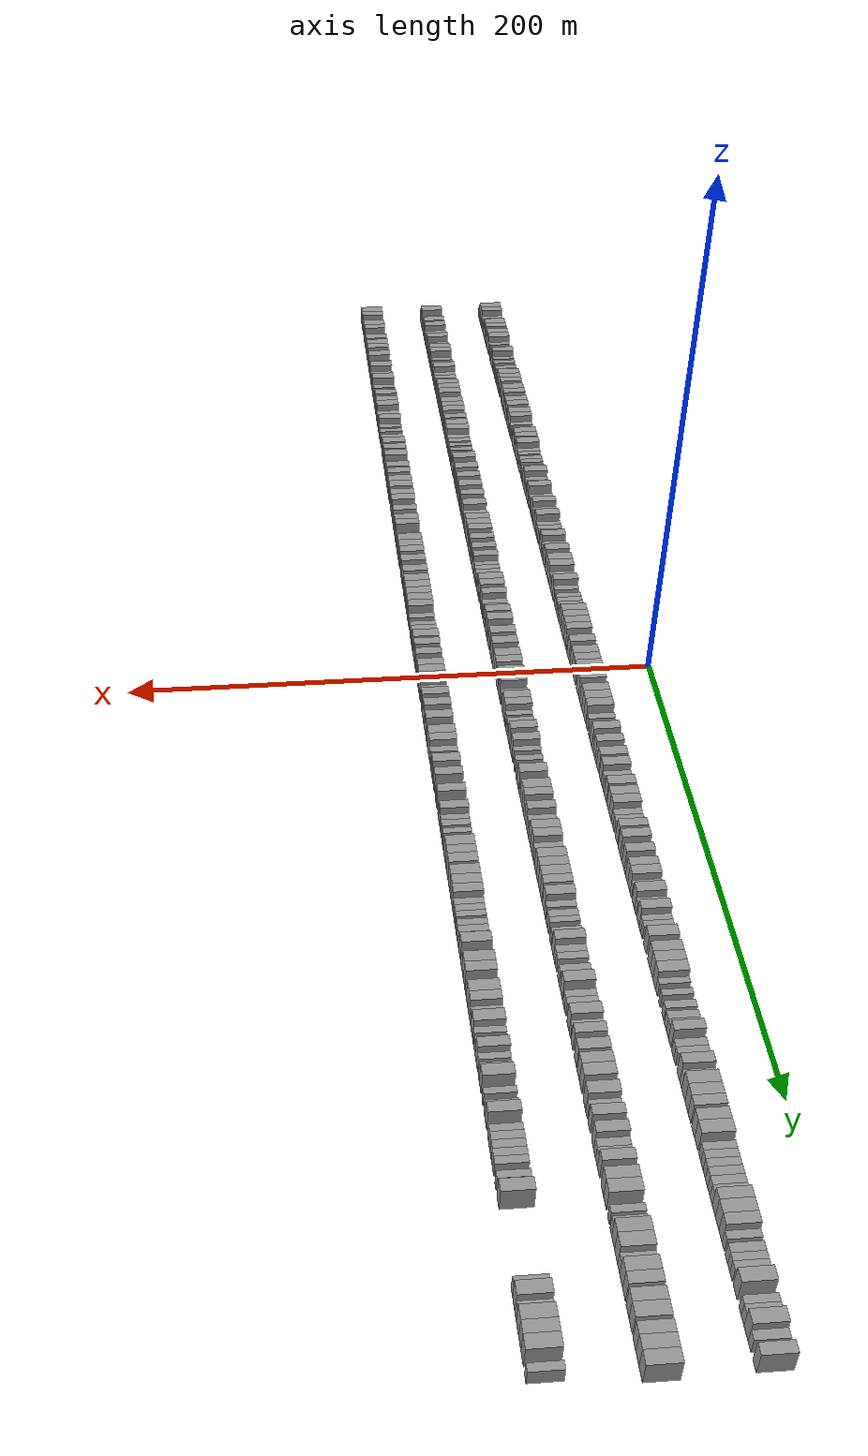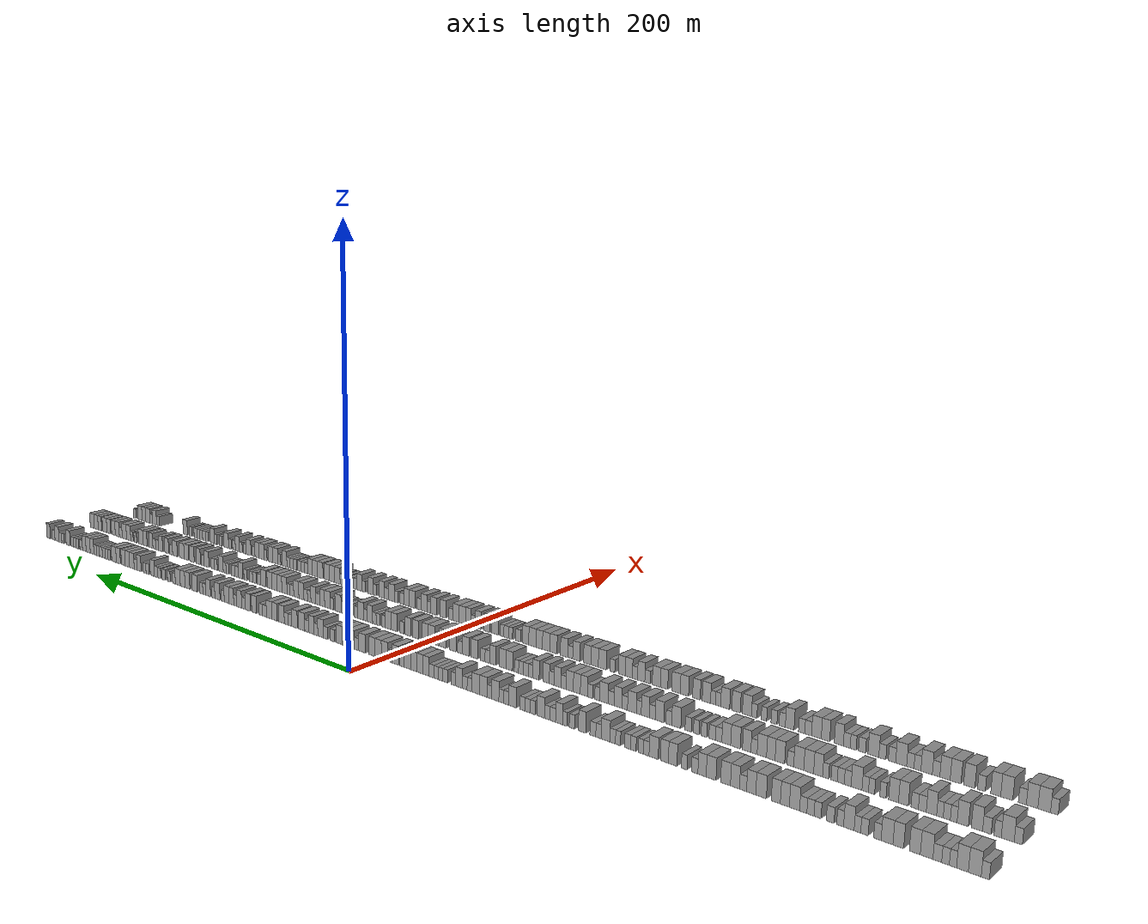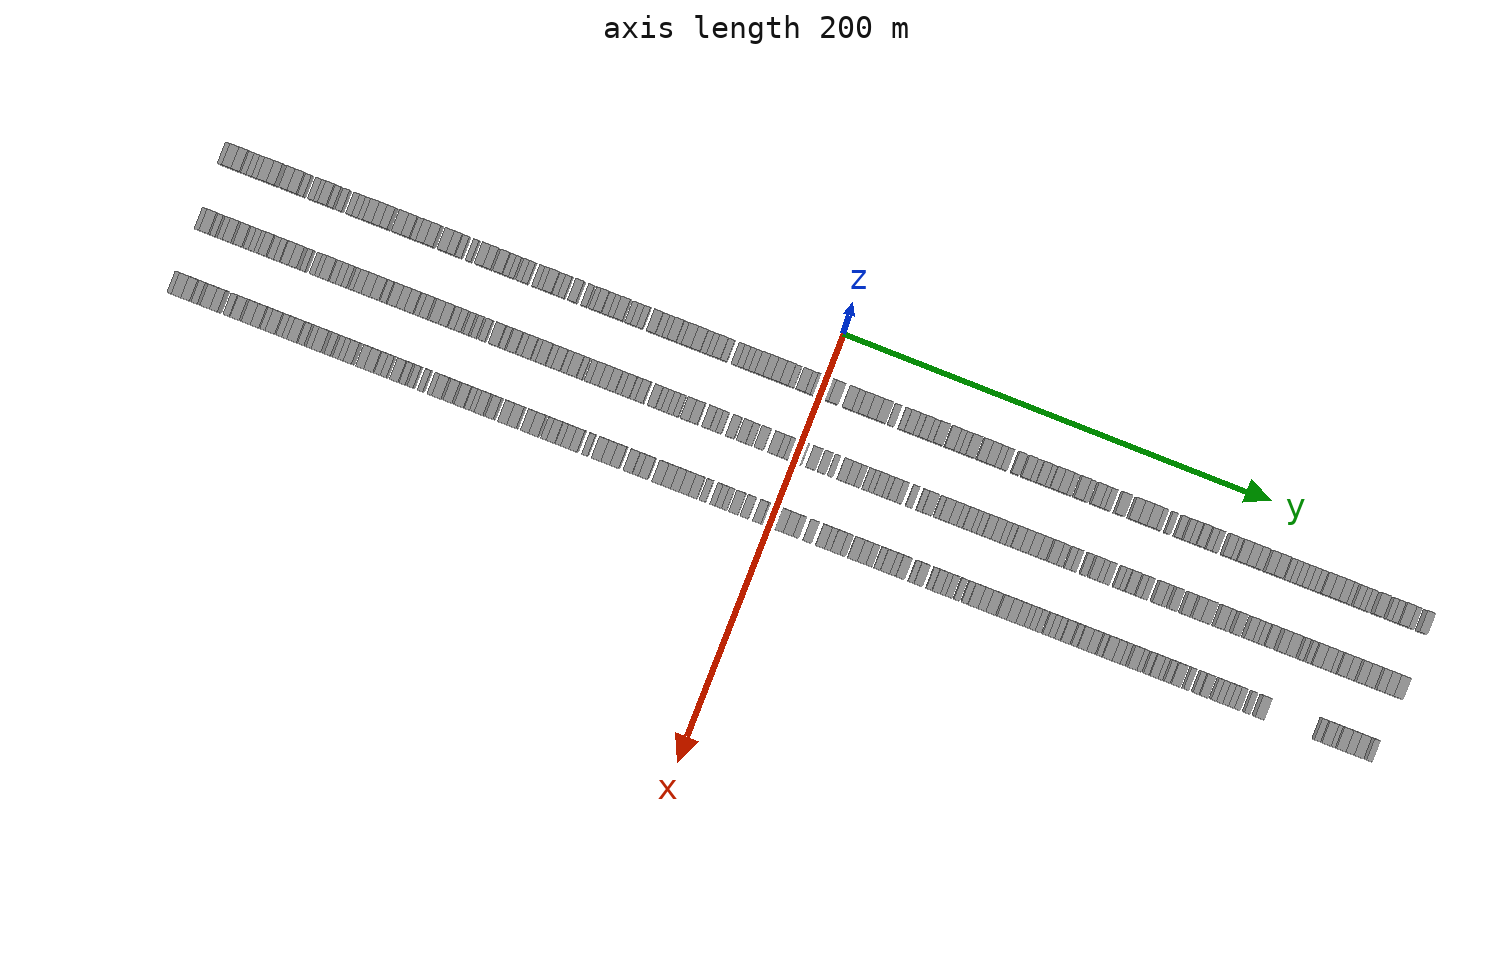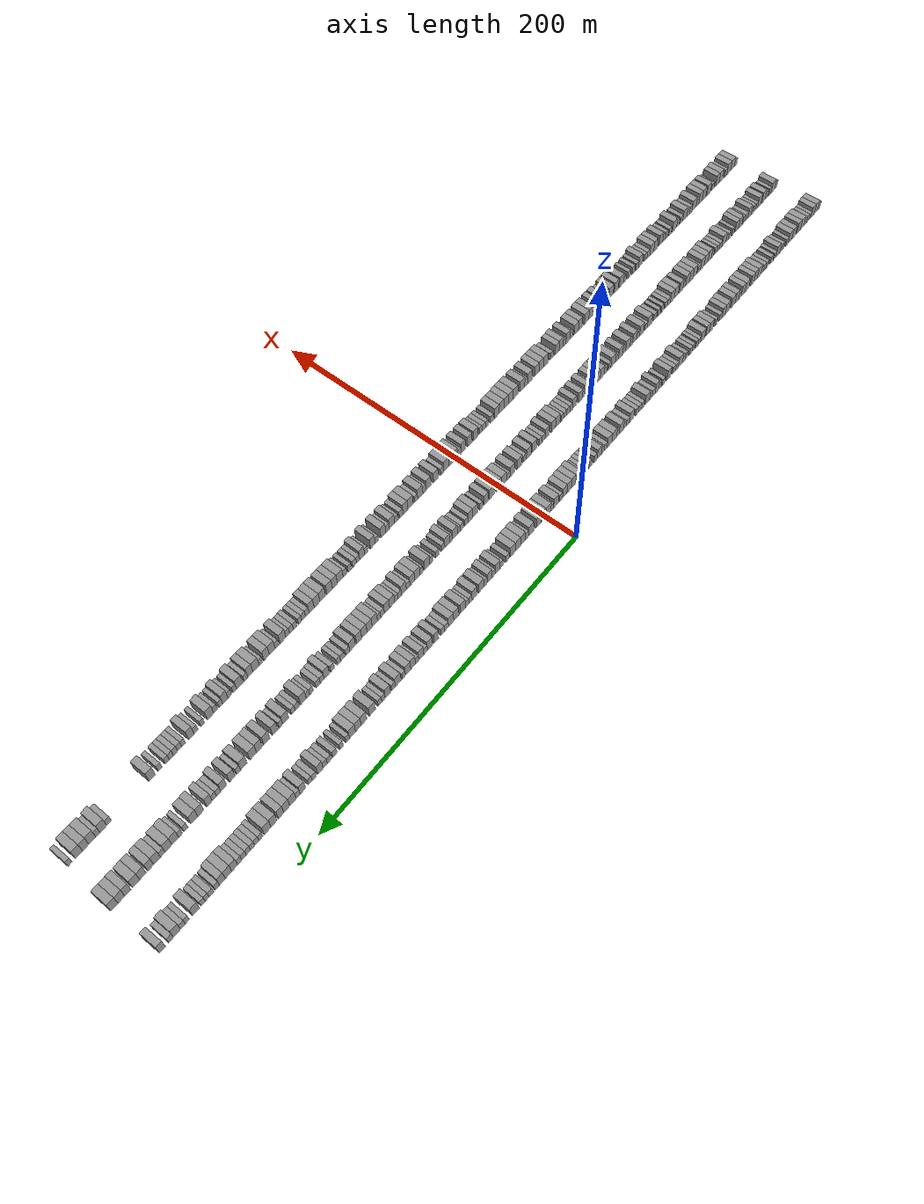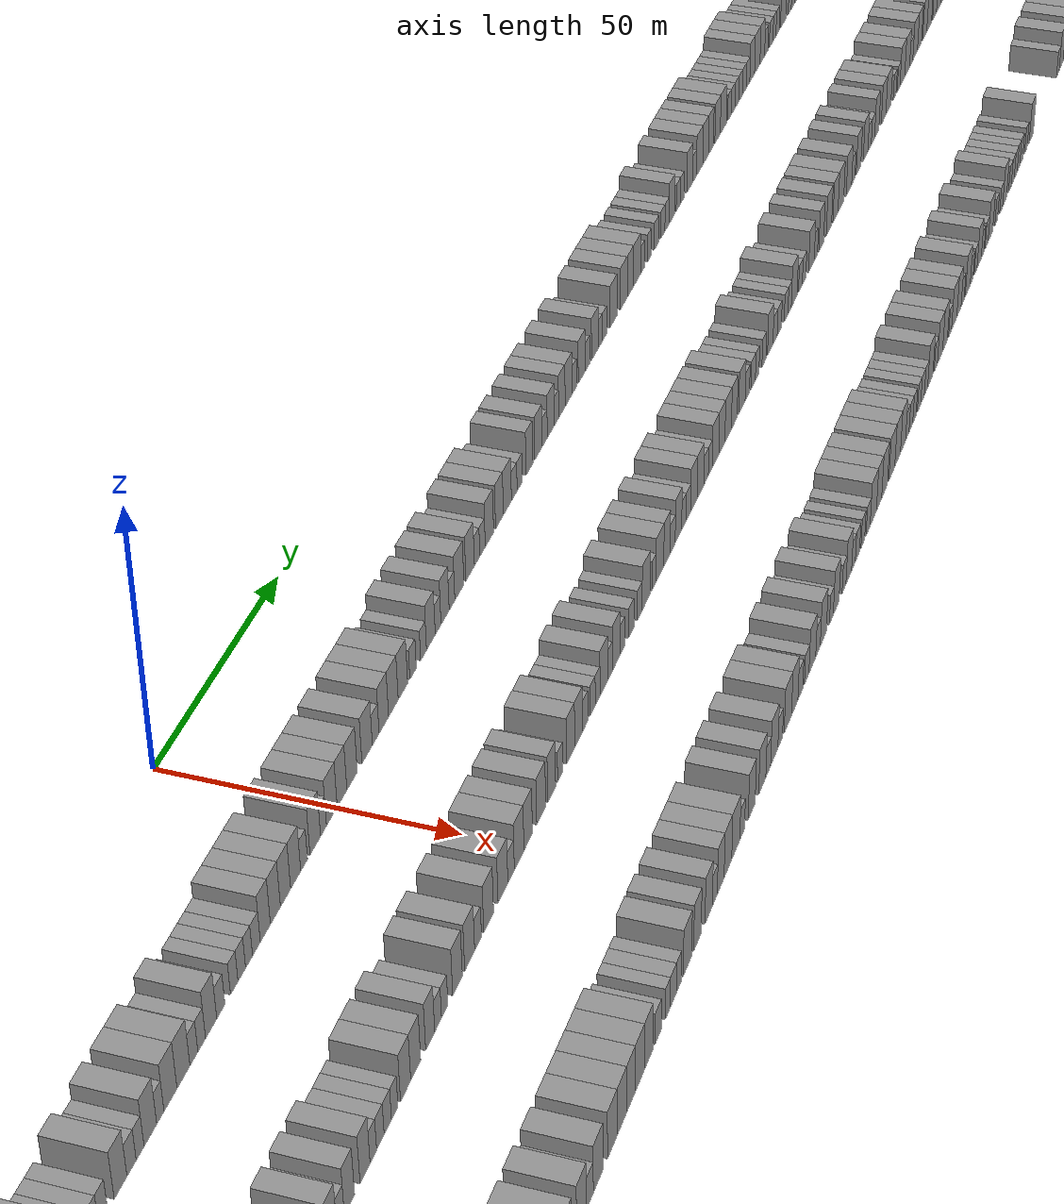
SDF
<sdf version="1.6">
 <world name="default">
  <scene>
   <sky><clouds><speed>12</speed></clouds></sky>
   <ambient>0.4 0.4 0.4 1</ambient>
   <background>0.7 0.7 0.7 1</background>
   <shadows>1</shadows>
  </scene>
  <gravity>0 0 -9.8066</gravity>
  <magnetic_field>6e-06 2.3e-05 -4.2e-05</magnetic_field>
  <physics default="0" name="default_physics" type="ode">
   <ode>
    <solver>
     <type>quick</type>
     <iters>10</iters>
     <sor>1.0</sor>
     <use_dynamic_moi_rescaling>0</use_dynamic_moi_rescaling>
    </solver>
    <constraints>
     <cfm>0</cfm>
     <erp>0.2</erp>
     <contact_max_correcting_vel>100</contact_max_correcting_vel>
     <contact_surface_layer>0.001</contact_surface_layer>
    </constraints>
   </ode>
   <max_step_size>0.004</max_step_size>
   <real_time_factor>1</real_time_factor>
   <real_time_update_rate>250</real_time_update_rate>
  </physics>
  <light name="sun" type="directional">
   <pose>0 0 10 0 0 0</pose>
   <diffuse>0.8 0.8 0.8 1</diffuse>
   <specular>0.2 0.2 0.2 1</specular>
   <attenuation>
    <range>1000</range>
    <constant>0.9</constant>
    <linear>0.01</linear>
    <quadratic>0.001</quadratic>
   </attenuation>
   <direction>-0.5 0.1 -0.9</direction>
  </light>
  <model name="building_1">
   <static>1</static>
   <pose>25.0000 -278.6493 0 0.000000 0.000000 0.000000</pose>
   <link name="link">
    <pose>0 0 3.00 0 0 0</pose>
    <collision name="collision"><geometry><box><size>10.0000 2.7014 6.0000</size></box></geometry></collision>
    <visual name="visual">
     <cast_shadows>0</cast_shadows>
     <geometry><box><size>10.0000 2.7014 6.0000</size></box></geometry>
     <material>
      <script>
       <uri>model://grey_wall/materials/scripts</uri>
       <uri>model://grey_wall/materials/textures</uri>
       <name>vrc/grey_wall</name>
      </script>
     </material>
    </visual>
   </link>
  </model>
  <model name="building_2">
   <static>1</static>
   <pose>25.0000 -275.1745 0 0.000000 0.000000 0.000000</pose>
   <link name="link">
    <pose>0 0 4.50 0 0 0</pose>
    <collision name="collision"><geometry><box><size>10.0000 4.2482 9.0000</size></box></geometry></collision>
    <visual name="visual">
     <cast_shadows>0</cast_shadows>
     <geometry><box><size>10.0000 4.2482 9.0000</size></box></geometry>
     <material>
      <script>
       <uri>model://grey_wall/materials/scripts</uri>
       <uri>model://grey_wall/materials/textures</uri>
       <name>vrc/grey_wall</name>
      </script>
     </material>
    </visual>
   </link>
  </model>
  <model name="building_3">
   <static>1</static>
   <pose>25.0000 -271.0748 0 0.000000 0.000000 0.000000</pose>
   <link name="link">
    <pose>0 0 4.50 0 0 0</pose>
    <collision name="collision"><geometry><box><size>10.0000 3.9511 9.0000</size></box></geometry></collision>
    <visual name="visual">
     <cast_shadows>0</cast_shadows>
     <geometry><box><size>10.0000 3.9511 9.0000</size></box></geometry>
     <material>
      <script>
       <uri>model://grey_wall/materials/scripts</uri>
       <uri>model://grey_wall/materials/textures</uri>
       <name>vrc/grey_wall</name>
      </script>
     </material>
    </visual>
   </link>
  </model>
  <model name="building_4">
   <static>1</static>
   <pose>25.0000 -267.8792 0 0.000000 0.000000 0.000000</pose>
   <link name="link">
    <pose>0 0 3.00 0 0 0</pose>
    <collision name="collision"><geometry><box><size>10.0000 2.4400 6.0000</size></box></geometry></collision>
    <visual name="visual">
     <cast_shadows>0</cast_shadows>
     <geometry><box><size>10.0000 2.4400 6.0000</size></box></geometry>
     <material>
      <script>
       <uri>model://grey_wall/materials/scripts</uri>
       <uri>model://grey_wall/materials/textures</uri>
       <name>vrc/grey_wall</name>
      </script>
     </material>
    </visual>
   </link>
  </model>
  <model name="building_5">
   <static>1</static>
   <pose>25.0000 -265.3566 0 0.000000 0.000000 0.000000</pose>
   <link name="link">
    <pose>0 0 3.00 0 0 0</pose>
    <collision name="collision"><geometry><box><size>10.0000 2.6051 6.0000</size></box></geometry></collision>
    <visual name="visual">
     <cast_shadows>0</cast_shadows>
     <geometry><box><size>10.0000 2.6051 6.0000</size></box></geometry>
     <material>
      <script>
       <uri>model://grey_wall/materials/scripts</uri>
       <uri>model://grey_wall/materials/textures</uri>
       <name>vrc/grey_wall</name>
      </script>
     </material>
    </visual>
   </link>
  </model>
  <model name="building_6">
   <static>1</static>
   <pose>25.0000 -262.5599 0 0.000000 0.000000 0.000000</pose>
   <link name="link">
    <pose>0 0 3.00 0 0 0</pose>
    <collision name="collision"><geometry><box><size>10.0000 2.9883 6.0000</size></box></geometry></collision>
    <visual name="visual">
     <cast_shadows>0</cast_shadows>
     <geometry><box><size>10.0000 2.9883 6.0000</size></box></geometry>
     <material>
      <script>
       <uri>model://grey_wall/materials/scripts</uri>
       <uri>model://grey_wall/materials/textures</uri>
       <name>vrc/grey_wall</name>
      </script>
     </material>
    </visual>
   </link>
  </model>
  <model name="building_7">
   <static>1</static>
   <pose>25.0000 -258.8811 0 0.000000 0.000000 0.000000</pose>
   <link name="link">
    <pose>0 0 4.50 0 0 0</pose>
    <collision name="collision"><geometry><box><size>10.0000 4.3694 9.0000</size></box></geometry></collision>
    <visual name="visual">
     <cast_shadows>0</cast_shadows>
     <geometry><box><size>10.0000 4.3694 9.0000</size></box></geometry>
     <material>
      <script>
       <uri>model://grey_wall/materials/scripts</uri>
       <uri>model://grey_wall/materials/textures</uri>
       <name>vrc/grey_wall</name>
      </script>
     </material>
    </visual>
   </link>
  </model>
  <model name="building_8">
   <static>1</static>
   <pose>25.0000 -254.7702 0 0.000000 0.000000 0.000000</pose>
   <link name="link">
    <pose>0 0 4.50 0 0 0</pose>
    <collision name="collision"><geometry><box><size>10.0000 3.8524 9.0000</size></box></geometry></collision>
    <visual name="visual">
     <cast_shadows>0</cast_shadows>
     <geometry><box><size>10.0000 3.8524 9.0000</size></box></geometry>
     <material>
      <script>
       <uri>model://grey_wall/materials/scripts</uri>
       <uri>model://grey_wall/materials/textures</uri>
       <name>vrc/grey_wall</name>
      </script>
     </material>
    </visual>
   </link>
  </model>
  <model name="building_9">
   <static>1</static>
   <pose>25.0000 -248.9392 0 0.000000 0.000000 0.000000</pose>
   <link name="link">
    <pose>0 0 4.50 0 0 0</pose>
    <collision name="collision"><geometry><box><size>10.0000 3.8097 9.0000</size></box></geometry></collision>
    <visual name="visual">
     <cast_shadows>0</cast_shadows>
     <geometry><box><size>10.0000 3.8097 9.0000</size></box></geometry>
     <material>
      <script>
       <uri>model://grey_wall/materials/scripts</uri>
       <uri>model://grey_wall/materials/textures</uri>
       <name>vrc/grey_wall</name>
      </script>
     </material>
    </visual>
   </link>
  </model>
  <model name="building_10">
   <static>1</static>
   <pose>25.0000 -244.8986 0 0.000000 0.000000 0.000000</pose>
   <link name="link">
    <pose>0 0 4.50 0 0 0</pose>
    <collision name="collision"><geometry><box><size>10.0000 4.2715 9.0000</size></box></geometry></collision>
    <visual name="visual">
     <cast_shadows>0</cast_shadows>
     <geometry><box><size>10.0000 4.2715 9.0000</size></box></geometry>
     <material>
      <script>
       <uri>model://grey_wall/materials/scripts</uri>
       <uri>model://grey_wall/materials/textures</uri>
       <name>vrc/grey_wall</name>
      </script>
     </material>
    </visual>
   </link>
  </model>
  <model name="building_11">
   <static>1</static>
   <pose>25.0000 -241.4054 0 0.000000 0.000000 0.000000</pose>
   <link name="link">
    <pose>0 0 3.00 0 0 0</pose>
    <collision name="collision"><geometry><box><size>10.0000 2.7150 6.0000</size></box></geometry></collision>
    <visual name="visual">
     <cast_shadows>0</cast_shadows>
     <geometry><box><size>10.0000 2.7150 6.0000</size></box></geometry>
     <material>
      <script>
       <uri>model://grey_wall/materials/scripts</uri>
       <uri>model://grey_wall/materials/textures</uri>
       <name>vrc/grey_wall</name>
      </script>
     </material>
    </visual>
   </link>
  </model>
  <model name="building_12">
   <static>1</static>
   <pose>25.0000 -236.6688 0 0.000000 0.000000 0.000000</pose>
   <link name="link">
    <pose>0 0 3.00 0 0 0</pose>
    <collision name="collision"><geometry><box><size>10.0000 2.7581 6.0000</size></box></geometry></collision>
    <visual name="visual">
     <cast_shadows>0</cast_shadows>
     <geometry><box><size>10.0000 2.7581 6.0000</size></box></geometry>
     <material>
      <script>
       <uri>model://grey_wall/materials/scripts</uri>
       <uri>model://grey_wall/materials/textures</uri>
       <name>vrc/grey_wall</name>
      </script>
     </material>
    </visual>
   </link>
  </model>
  <model name="building_13">
   <static>1</static>
   <pose>25.0000 -234.0657 0 0.000000 0.000000 0.000000</pose>
   <link name="link">
    <pose>0 0 3.00 0 0 0</pose>
    <collision name="collision"><geometry><box><size>10.0000 2.4483 6.0000</size></box></geometry></collision>
    <visual name="visual">
     <cast_shadows>0</cast_shadows>
     <geometry><box><size>10.0000 2.4483 6.0000</size></box></geometry>
     <material>
      <script>
       <uri>model://grey_wall/materials/scripts</uri>
       <uri>model://grey_wall/materials/textures</uri>
       <name>vrc/grey_wall</name>
      </script>
     </material>
    </visual>
   </link>
  </model>
  <model name="building_14">
   <static>1</static>
   <pose>25.0000 -230.8664 0 0.000000 0.000000 0.000000</pose>
   <link name="link">
    <pose>0 0 4.50 0 0 0</pose>
    <collision name="collision"><geometry><box><size>10.0000 3.9503 9.0000</size></box></geometry></collision>
    <visual name="visual">
     <cast_shadows>0</cast_shadows>
     <geometry><box><size>10.0000 3.9503 9.0000</size></box></geometry>
     <material>
      <script>
       <uri>model://grey_wall/materials/scripts</uri>
       <uri>model://grey_wall/materials/textures</uri>
       <name>vrc/grey_wall</name>
      </script>
     </material>
    </visual>
   </link>
  </model>
  <model name="building_15">
   <static>1</static>
   <pose>25.0000 -227.5878 0 0.000000 0.000000 0.000000</pose>
   <link name="link">
    <pose>0 0 3.00 0 0 0</pose>
    <collision name="collision"><geometry><box><size>10.0000 2.6067 6.0000</size></box></geometry></collision>
    <visual name="visual">
     <cast_shadows>0</cast_shadows>
     <geometry><box><size>10.0000 2.6067 6.0000</size></box></geometry>
     <material>
      <script>
       <uri>model://grey_wall/materials/scripts</uri>
       <uri>model://grey_wall/materials/textures</uri>
       <name>vrc/grey_wall</name>
      </script>
     </material>
    </visual>
   </link>
  </model>
  <model name="building_16">
   <static>1</static>
   <pose>25.0000 -223.7880 0 0.000000 0.000000 0.000000</pose>
   <link name="link">
    <pose>0 0 3.00 0 0 0</pose>
    <collision name="collision"><geometry><box><size>10.0000 2.9929 6.0000</size></box></geometry></collision>
    <visual name="visual">
     <cast_shadows>0</cast_shadows>
     <geometry><box><size>10.0000 2.9929 6.0000</size></box></geometry>
     <material>
      <script>
       <uri>model://grey_wall/materials/scripts</uri>
       <uri>model://grey_wall/materials/textures</uri>
       <name>vrc/grey_wall</name>
      </script>
     </material>
    </visual>
   </link>
  </model>
  <model name="building_17">
   <static>1</static>
   <pose>25.0000 -218.9373 0 0.000000 0.000000 0.000000</pose>
   <link name="link">
    <pose>0 0 3.00 0 0 0</pose>
    <collision name="collision"><geometry><box><size>10.0000 2.7085 6.0000</size></box></geometry></collision>
    <visual name="visual">
     <cast_shadows>0</cast_shadows>
     <geometry><box><size>10.0000 2.7085 6.0000</size></box></geometry>
     <material>
      <script>
       <uri>model://grey_wall/materials/scripts</uri>
       <uri>model://grey_wall/materials/textures</uri>
       <name>vrc/grey_wall</name>
      </script>
     </material>
    </visual>
   </link>
  </model>
  <model name="building_18">
   <static>1</static>
   <pose>25.0000 -216.1864 0 0.000000 0.000000 0.000000</pose>
   <link name="link">
    <pose>0 0 3.00 0 0 0</pose>
    <collision name="collision"><geometry><box><size>10.0000 2.7932 6.0000</size></box></geometry></collision>
    <visual name="visual">
     <cast_shadows>0</cast_shadows>
     <geometry><box><size>10.0000 2.7932 6.0000</size></box></geometry>
     <material>
      <script>
       <uri>model://grey_wall/materials/scripts</uri>
       <uri>model://grey_wall/materials/textures</uri>
       <name>vrc/grey_wall</name>
      </script>
     </material>
    </visual>
   </link>
  </model>
  <model name="building_19">
   <static>1</static>
   <pose>25.0000 -213.3558 0 0.000000 0.000000 0.000000</pose>
   <link name="link">
    <pose>0 0 3.00 0 0 0</pose>
    <collision name="collision"><geometry><box><size>10.0000 2.8680 6.0000</size></box></geometry></collision>
    <visual name="visual">
     <cast_shadows>0</cast_shadows>
     <geometry><box><size>10.0000 2.8680 6.0000</size></box></geometry>
     <material>
      <script>
       <uri>model://grey_wall/materials/scripts</uri>
       <uri>model://grey_wall/materials/textures</uri>
       <name>vrc/grey_wall</name>
      </script>
     </material>
    </visual>
   </link>
  </model>
  <model name="building_20">
   <static>1</static>
   <pose>25.0000 -209.8904 0 0.000000 0.000000 0.000000</pose>
   <link name="link">
    <pose>0 0 4.50 0 0 0</pose>
    <collision name="collision"><geometry><box><size>10.0000 4.0627 9.0000</size></box></geometry></collision>
    <visual name="visual">
     <cast_shadows>0</cast_shadows>
     <geometry><box><size>10.0000 4.0627 9.0000</size></box></geometry>
     <material>
      <script>
       <uri>model://grey_wall/materials/scripts</uri>
       <uri>model://grey_wall/materials/textures</uri>
       <name>vrc/grey_wall</name>
      </script>
     </material>
    </visual>
   </link>
  </model>
  <model name="building_21">
   <static>1</static>
   <pose>25.0000 -206.0500 0 0.000000 0.000000 0.000000</pose>
   <link name="link">
    <pose>0 0 4.50 0 0 0</pose>
    <collision name="collision"><geometry><box><size>10.0000 3.6181 9.0000</size></box></geometry></collision>
    <visual name="visual">
     <cast_shadows>0</cast_shadows>
     <geometry><box><size>10.0000 3.6181 9.0000</size></box></geometry>
     <material>
      <script>
       <uri>model://grey_wall/materials/scripts</uri>
       <uri>model://grey_wall/materials/textures</uri>
       <name>vrc/grey_wall</name>
      </script>
     </material>
    </visual>
   </link>
  </model>
  <model name="building_22">
   <static>1</static>
   <pose>25.0000 -202.4100 0 0.000000 0.000000 0.000000</pose>
   <link name="link">
    <pose>0 0 4.50 0 0 0</pose>
    <collision name="collision"><geometry><box><size>10.0000 3.6619 9.0000</size></box></geometry></collision>
    <visual name="visual">
     <cast_shadows>0</cast_shadows>
     <geometry><box><size>10.0000 3.6619 9.0000</size></box></geometry>
     <material>
      <script>
       <uri>model://grey_wall/materials/scripts</uri>
       <uri>model://grey_wall/materials/textures</uri>
       <name>vrc/grey_wall</name>
      </script>
     </material>
    </visual>
   </link>
  </model>
  <model name="building_23">
   <static>1</static>
   <pose>25.0000 -196.3840 0 0.000000 0.000000 0.000000</pose>
   <link name="link">
    <pose>0 0 4.50 0 0 0</pose>
    <collision name="collision"><geometry><box><size>10.0000 4.3901 9.0000</size></box></geometry></collision>
    <visual name="visual">
     <cast_shadows>0</cast_shadows>
     <geometry><box><size>10.0000 4.3901 9.0000</size></box></geometry>
     <material>
      <script>
       <uri>model://grey_wall/materials/scripts</uri>
       <uri>model://grey_wall/materials/textures</uri>
       <name>vrc/grey_wall</name>
      </script>
     </material>
    </visual>
   </link>
  </model>
  <model name="building_24">
   <static>1</static>
   <pose>25.0000 -192.2875 0 0.000000 0.000000 0.000000</pose>
   <link name="link">
    <pose>0 0 4.50 0 0 0</pose>
    <collision name="collision"><geometry><box><size>10.0000 3.8027 9.0000</size></box></geometry></collision>
    <visual name="visual">
     <cast_shadows>0</cast_shadows>
     <geometry><box><size>10.0000 3.8027 9.0000</size></box></geometry>
     <material>
      <script>
       <uri>model://grey_wall/materials/scripts</uri>
       <uri>model://grey_wall/materials/textures</uri>
       <name>vrc/grey_wall</name>
      </script>
     </material>
    </visual>
   </link>
  </model>
  <model name="building_25">
   <static>1</static>
   <pose>25.0000 -188.8988 0 0.000000 0.000000 0.000000</pose>
   <link name="link">
    <pose>0 0 3.00 0 0 0</pose>
    <collision name="collision"><geometry><box><size>10.0000 2.9748 6.0000</size></box></geometry></collision>
    <visual name="visual">
     <cast_shadows>0</cast_shadows>
     <geometry><box><size>10.0000 2.9748 6.0000</size></box></geometry>
     <material>
      <script>
       <uri>model://grey_wall/materials/scripts</uri>
       <uri>model://grey_wall/materials/textures</uri>
       <name>vrc/grey_wall</name>
      </script>
     </material>
    </visual>
   </link>
  </model>
  <model name="building_26">
   <static>1</static>
   <pose>25.0000 -185.5130 0 0.000000 0.000000 0.000000</pose>
   <link name="link">
    <pose>0 0 4.50 0 0 0</pose>
    <collision name="collision"><geometry><box><size>10.0000 3.7967 9.0000</size></box></geometry></collision>
    <visual name="visual">
     <cast_shadows>0</cast_shadows>
     <geometry><box><size>10.0000 3.7967 9.0000</size></box></geometry>
     <material>
      <script>
       <uri>model://grey_wall/materials/scripts</uri>
       <uri>model://grey_wall/materials/textures</uri>
       <name>vrc/grey_wall</name>
      </script>
     </material>
    </visual>
   </link>
  </model>
  <model name="building_27">
   <static>1</static>
   <pose>25.0000 -181.5029 0 0.000000 0.000000 0.000000</pose>
   <link name="link">
    <pose>0 0 4.50 0 0 0</pose>
    <collision name="collision"><geometry><box><size>10.0000 4.2234 9.0000</size></box></geometry></collision>
    <visual name="visual">
     <cast_shadows>0</cast_shadows>
     <geometry><box><size>10.0000 4.2234 9.0000</size></box></geometry>
     <material>
      <script>
       <uri>model://grey_wall/materials/scripts</uri>
       <uri>model://grey_wall/materials/textures</uri>
       <name>vrc/grey_wall</name>
      </script>
     </material>
    </visual>
   </link>
  </model>
  <model name="building_28">
   <static>1</static>
   <pose>25.0000 -175.2594 0 0.000000 0.000000 0.000000</pose>
   <link name="link">
    <pose>0 0 4.50 0 0 0</pose>
    <collision name="collision"><geometry><box><size>10.0000 4.2636 9.0000</size></box></geometry></collision>
    <visual name="visual">
     <cast_shadows>0</cast_shadows>
     <geometry><box><size>10.0000 4.2636 9.0000</size></box></geometry>
     <material>
      <script>
       <uri>model://grey_wall/materials/scripts</uri>
       <uri>model://grey_wall/materials/textures</uri>
       <name>vrc/grey_wall</name>
      </script>
     </material>
    </visual>
   </link>
  </model>
  <model name="building_29">
   <static>1</static>
   <pose>25.0000 -171.3169 0 0.000000 0.000000 0.000000</pose>
   <link name="link">
    <pose>0 0 4.50 0 0 0</pose>
    <collision name="collision"><geometry><box><size>10.0000 3.6215 9.0000</size></box></geometry></collision>
    <visual name="visual">
     <cast_shadows>0</cast_shadows>
     <geometry><box><size>10.0000 3.6215 9.0000</size></box></geometry>
     <material>
      <script>
       <uri>model://grey_wall/materials/scripts</uri>
       <uri>model://grey_wall/materials/textures</uri>
       <name>vrc/grey_wall</name>
      </script>
     </material>
    </visual>
   </link>
  </model>
  <model name="building_30">
   <static>1</static>
   <pose>25.0000 -168.0825 0 0.000000 0.000000 0.000000</pose>
   <link name="link">
    <pose>0 0 3.00 0 0 0</pose>
    <collision name="collision"><geometry><box><size>10.0000 2.8471 6.0000</size></box></geometry></collision>
    <visual name="visual">
     <cast_shadows>0</cast_shadows>
     <geometry><box><size>10.0000 2.8471 6.0000</size></box></geometry>
     <material>
      <script>
       <uri>model://grey_wall/materials/scripts</uri>
       <uri>model://grey_wall/materials/textures</uri>
       <name>vrc/grey_wall</name>
      </script>
     </material>
    </visual>
   </link>
  </model>
  <model name="building_31">
   <static>1</static>
   <pose>25.0000 -163.4089 0 0.000000 0.000000 0.000000</pose>
   <link name="link">
    <pose>0 0 3.00 0 0 0</pose>
    <collision name="collision"><geometry><box><size>10.0000 2.5001 6.0000</size></box></geometry></collision>
    <visual name="visual">
     <cast_shadows>0</cast_shadows>
     <geometry><box><size>10.0000 2.5001 6.0000</size></box></geometry>
     <material>
      <script>
       <uri>model://grey_wall/materials/scripts</uri>
       <uri>model://grey_wall/materials/textures</uri>
       <name>vrc/grey_wall</name>
      </script>
     </material>
    </visual>
   </link>
  </model>
  <model name="building_32">
   <static>1</static>
   <pose>25.0000 -158.1939 0 0.000000 0.000000 0.000000</pose>
   <link name="link">
    <pose>0 0 4.50 0 0 0</pose>
    <collision name="collision"><geometry><box><size>10.0000 3.9300 9.0000</size></box></geometry></collision>
    <visual name="visual">
     <cast_shadows>0</cast_shadows>
     <geometry><box><size>10.0000 3.9300 9.0000</size></box></geometry>
     <material>
      <script>
       <uri>model://grey_wall/materials/scripts</uri>
       <uri>model://grey_wall/materials/textures</uri>
       <name>vrc/grey_wall</name>
      </script>
     </material>
    </visual>
   </link>
  </model>
  <model name="building_33">
   <static>1</static>
   <pose>25.0000 -154.4274 0 0.000000 0.000000 0.000000</pose>
   <link name="link">
    <pose>0 0 4.50 0 0 0</pose>
    <collision name="collision"><geometry><box><size>10.0000 3.6031 9.0000</size></box></geometry></collision>
    <visual name="visual">
     <cast_shadows>0</cast_shadows>
     <geometry><box><size>10.0000 3.6031 9.0000</size></box></geometry>
     <material>
      <script>
       <uri>model://grey_wall/materials/scripts</uri>
       <uri>model://grey_wall/materials/textures</uri>
       <name>vrc/grey_wall</name>
      </script>
     </material>
    </visual>
   </link>
  </model>
  <model name="building_34">
   <static>1</static>
   <pose>25.0000 -149.4986 0 0.000000 0.000000 0.000000</pose>
   <link name="link">
    <pose>0 0 4.50 0 0 0</pose>
    <collision name="collision"><geometry><box><size>10.0000 4.2544 9.0000</size></box></geometry></collision>
    <visual name="visual">
     <cast_shadows>0</cast_shadows>
     <geometry><box><size>10.0000 4.2544 9.0000</size></box></geometry>
     <material>
      <script>
       <uri>model://grey_wall/materials/scripts</uri>
       <uri>model://grey_wall/materials/textures</uri>
       <name>vrc/grey_wall</name>
      </script>
     </material>
    </visual>
   </link>
  </model>
  <model name="building_35">
   <static>1</static>
   <pose>25.0000 -146.0353 0 0.000000 0.000000 0.000000</pose>
   <link name="link">
    <pose>0 0 3.00 0 0 0</pose>
    <collision name="collision"><geometry><box><size>10.0000 2.6723 6.0000</size></box></geometry></collision>
    <visual name="visual">
     <cast_shadows>0</cast_shadows>
     <geometry><box><size>10.0000 2.6723 6.0000</size></box></geometry>
     <material>
      <script>
       <uri>model://grey_wall/materials/scripts</uri>
       <uri>model://grey_wall/materials/textures</uri>
       <name>vrc/grey_wall</name>
      </script>
     </material>
    </visual>
   </link>
  </model>
  <model name="building_36">
   <static>1</static>
   <pose>25.0000 -143.4784 0 0.000000 0.000000 0.000000</pose>
   <link name="link">
    <pose>0 0 3.00 0 0 0</pose>
    <collision name="collision"><geometry><box><size>10.0000 2.4415 6.0000</size></box></geometry></collision>
    <visual name="visual">
     <cast_shadows>0</cast_shadows>
     <geometry><box><size>10.0000 2.4415 6.0000</size></box></geometry>
     <material>
      <script>
       <uri>model://grey_wall/materials/scripts</uri>
       <uri>model://grey_wall/materials/textures</uri>
       <name>vrc/grey_wall</name>
      </script>
     </material>
    </visual>
   </link>
  </model>
  <model name="building_37">
   <static>1</static>
   <pose>25.0000 -139.9270 0 0.000000 0.000000 0.000000</pose>
   <link name="link">
    <pose>0 0 3.00 0 0 0</pose>
    <collision name="collision"><geometry><box><size>10.0000 2.6613 6.0000</size></box></geometry></collision>
    <visual name="visual">
     <cast_shadows>0</cast_shadows>
     <geometry><box><size>10.0000 2.6613 6.0000</size></box></geometry>
     <material>
      <script>
       <uri>model://grey_wall/materials/scripts</uri>
       <uri>model://grey_wall/materials/textures</uri>
       <name>vrc/grey_wall</name>
      </script>
     </material>
    </visual>
   </link>
  </model>
  <model name="building_38">
   <static>1</static>
   <pose>25.0000 -137.2169 0 0.000000 0.000000 0.000000</pose>
   <link name="link">
    <pose>0 0 3.00 0 0 0</pose>
    <collision name="collision"><geometry><box><size>10.0000 2.7589 6.0000</size></box></geometry></collision>
    <visual name="visual">
     <cast_shadows>0</cast_shadows>
     <geometry><box><size>10.0000 2.7589 6.0000</size></box></geometry>
     <material>
      <script>
       <uri>model://grey_wall/materials/scripts</uri>
       <uri>model://grey_wall/materials/textures</uri>
       <name>vrc/grey_wall</name>
      </script>
     </material>
    </visual>
   </link>
  </model>
  <model name="building_39">
   <static>1</static>
   <pose>25.0000 -132.6166 0 0.000000 0.000000 0.000000</pose>
   <link name="link">
    <pose>0 0 3.00 0 0 0</pose>
    <collision name="collision"><geometry><box><size>10.0000 2.4417 6.0000</size></box></geometry></collision>
    <visual name="visual">
     <cast_shadows>0</cast_shadows>
     <geometry><box><size>10.0000 2.4417 6.0000</size></box></geometry>
     <material>
      <script>
       <uri>model://grey_wall/materials/scripts</uri>
       <uri>model://grey_wall/materials/textures</uri>
       <name>vrc/grey_wall</name>
      </script>
     </material>
    </visual>
   </link>
  </model>
  <model name="building_40">
   <static>1</static>
   <pose>25.0000 -130.0644 0 0.000000 0.000000 0.000000</pose>
   <link name="link">
    <pose>0 0 3.00 0 0 0</pose>
    <collision name="collision"><geometry><box><size>10.0000 2.6626 6.0000</size></box></geometry></collision>
    <visual name="visual">
     <cast_shadows>0</cast_shadows>
     <geometry><box><size>10.0000 2.6626 6.0000</size></box></geometry>
     <material>
      <script>
       <uri>model://grey_wall/materials/scripts</uri>
       <uri>model://grey_wall/materials/textures</uri>
       <name>vrc/grey_wall</name>
      </script>
     </material>
    </visual>
   </link>
  </model>
  <model name="building_41">
   <static>1</static>
   <pose>25.0000 -126.5774 0 0.000000 0.000000 0.000000</pose>
   <link name="link">
    <pose>0 0 4.50 0 0 0</pose>
    <collision name="collision"><geometry><box><size>10.0000 4.3115 9.0000</size></box></geometry></collision>
    <visual name="visual">
     <cast_shadows>0</cast_shadows>
     <geometry><box><size>10.0000 4.3115 9.0000</size></box></geometry>
     <material>
      <script>
       <uri>model://grey_wall/materials/scripts</uri>
       <uri>model://grey_wall/materials/textures</uri>
       <name>vrc/grey_wall</name>
      </script>
     </material>
    </visual>
   </link>
  </model>
  <model name="building_42">
   <static>1</static>
   <pose>25.0000 -123.0931 0 0.000000 0.000000 0.000000</pose>
   <link name="link">
    <pose>0 0 3.00 0 0 0</pose>
    <collision name="collision"><geometry><box><size>10.0000 2.6571 6.0000</size></box></geometry></collision>
    <visual name="visual">
     <cast_shadows>0</cast_shadows>
     <geometry><box><size>10.0000 2.6571 6.0000</size></box></geometry>
     <material>
      <script>
       <uri>model://grey_wall/materials/scripts</uri>
       <uri>model://grey_wall/materials/textures</uri>
       <name>vrc/grey_wall</name>
      </script>
     </material>
    </visual>
   </link>
  </model>
  <model name="building_43">
   <static>1</static>
   <pose>25.0000 -120.2917 0 0.000000 0.000000 0.000000</pose>
   <link name="link">
    <pose>0 0 3.00 0 0 0</pose>
    <collision name="collision"><geometry><box><size>10.0000 2.9458 6.0000</size></box></geometry></collision>
    <visual name="visual">
     <cast_shadows>0</cast_shadows>
     <geometry><box><size>10.0000 2.9458 6.0000</size></box></geometry>
     <material>
      <script>
       <uri>model://grey_wall/materials/scripts</uri>
       <uri>model://grey_wall/materials/textures</uri>
       <name>vrc/grey_wall</name>
      </script>
     </material>
    </visual>
   </link>
  </model>
  <model name="building_44">
   <static>1</static>
   <pose>25.0000 -114.9321 0 0.000000 0.000000 0.000000</pose>
   <link name="link">
    <pose>0 0 4.50 0 0 0</pose>
    <collision name="collision"><geometry><box><size>10.0000 3.7733 9.0000</size></box></geometry></collision>
    <visual name="visual">
     <cast_shadows>0</cast_shadows>
     <geometry><box><size>10.0000 3.7733 9.0000</size></box></geometry>
     <material>
      <script>
       <uri>model://grey_wall/materials/scripts</uri>
       <uri>model://grey_wall/materials/textures</uri>
       <name>vrc/grey_wall</name>
      </script>
     </material>
    </visual>
   </link>
  </model>
  <model name="building_45">
   <static>1</static>
   <pose>25.0000 -109.7149 0 0.000000 0.000000 0.000000</pose>
   <link name="link">
    <pose>0 0 3.00 0 0 0</pose>
    <collision name="collision"><geometry><box><size>10.0000 2.6612 6.0000</size></box></geometry></collision>
    <visual name="visual">
     <cast_shadows>0</cast_shadows>
     <geometry><box><size>10.0000 2.6612 6.0000</size></box></geometry>
     <material>
      <script>
       <uri>model://grey_wall/materials/scripts</uri>
       <uri>model://grey_wall/materials/textures</uri>
       <name>vrc/grey_wall</name>
      </script>
     </material>
    </visual>
   </link>
  </model>
  <model name="building_46">
   <static>1</static>
   <pose>25.0000 -106.1751 0 0.000000 0.000000 0.000000</pose>
   <link name="link">
    <pose>0 0 3.00 0 0 0</pose>
    <collision name="collision"><geometry><box><size>10.0000 2.4183 6.0000</size></box></geometry></collision>
    <visual name="visual">
     <cast_shadows>0</cast_shadows>
     <geometry><box><size>10.0000 2.4183 6.0000</size></box></geometry>
     <material>
      <script>
       <uri>model://grey_wall/materials/scripts</uri>
       <uri>model://grey_wall/materials/textures</uri>
       <name>vrc/grey_wall</name>
      </script>
     </material>
    </visual>
   </link>
  </model>
  <model name="building_47">
   <static>1</static>
   <pose>25.0000 -103.1440 0 0.000000 0.000000 0.000000</pose>
   <link name="link">
    <pose>0 0 4.50 0 0 0</pose>
    <collision name="collision"><geometry><box><size>10.0000 3.6439 9.0000</size></box></geometry></collision>
    <visual name="visual">
     <cast_shadows>0</cast_shadows>
     <geometry><box><size>10.0000 3.6439 9.0000</size></box></geometry>
     <material>
      <script>
       <uri>model://grey_wall/materials/scripts</uri>
       <uri>model://grey_wall/materials/textures</uri>
       <name>vrc/grey_wall</name>
      </script>
     </material>
    </visual>
   </link>
  </model>
  <model name="building_48">
   <static>1</static>
   <pose>25.0000 -99.8734 0 0.000000 0.000000 0.000000</pose>
   <link name="link">
    <pose>0 0 3.00 0 0 0</pose>
    <collision name="collision"><geometry><box><size>10.0000 2.8973 6.0000</size></box></geometry></collision>
    <visual name="visual">
     <cast_shadows>0</cast_shadows>
     <geometry><box><size>10.0000 2.8973 6.0000</size></box></geometry>
     <material>
      <script>
       <uri>model://grey_wall/materials/scripts</uri>
       <uri>model://grey_wall/materials/textures</uri>
       <name>vrc/grey_wall</name>
      </script>
     </material>
    </visual>
   </link>
  </model>
  <model name="building_49">
   <static>1</static>
   <pose>25.0000 -97.0424 0 0.000000 0.000000 0.000000</pose>
   <link name="link">
    <pose>0 0 3.00 0 0 0</pose>
    <collision name="collision"><geometry><box><size>10.0000 2.7647 6.0000</size></box></geometry></collision>
    <visual name="visual">
     <cast_shadows>0</cast_shadows>
     <geometry><box><size>10.0000 2.7647 6.0000</size></box></geometry>
     <material>
      <script>
       <uri>model://grey_wall/materials/scripts</uri>
       <uri>model://grey_wall/materials/textures</uri>
       <name>vrc/grey_wall</name>
      </script>
     </material>
    </visual>
   </link>
  </model>
  <model name="building_50">
   <static>1</static>
   <pose>25.0000 -93.5916 0 0.000000 0.000000 0.000000</pose>
   <link name="link">
    <pose>0 0 4.50 0 0 0</pose>
    <collision name="collision"><geometry><box><size>10.0000 4.1369 9.0000</size></box></geometry></collision>
    <visual name="visual">
     <cast_shadows>0</cast_shadows>
     <geometry><box><size>10.0000 4.1369 9.0000</size></box></geometry>
     <material>
      <script>
       <uri>model://grey_wall/materials/scripts</uri>
       <uri>model://grey_wall/materials/textures</uri>
       <name>vrc/grey_wall</name>
      </script>
     </material>
    </visual>
   </link>
  </model>
  <model name="building_51">
   <static>1</static>
   <pose>25.0000 -89.2349 0 0.000000 0.000000 0.000000</pose>
   <link name="link">
    <pose>0 0 3.00 0 0 0</pose>
    <collision name="collision"><geometry><box><size>10.0000 2.5765 6.0000</size></box></geometry></collision>
    <visual name="visual">
     <cast_shadows>0</cast_shadows>
     <geometry><box><size>10.0000 2.5765 6.0000</size></box></geometry>
     <material>
      <script>
       <uri>model://grey_wall/materials/scripts</uri>
       <uri>model://grey_wall/materials/textures</uri>
       <name>vrc/grey_wall</name>
      </script>
     </material>
    </visual>
   </link>
  </model>
  <model name="building_52">
   <static>1</static>
   <pose>25.0000 -86.5491 0 0.000000 0.000000 0.000000</pose>
   <link name="link">
    <pose>0 0 3.00 0 0 0</pose>
    <collision name="collision"><geometry><box><size>10.0000 2.7951 6.0000</size></box></geometry></collision>
    <visual name="visual">
     <cast_shadows>0</cast_shadows>
     <geometry><box><size>10.0000 2.7951 6.0000</size></box></geometry>
     <material>
      <script>
       <uri>model://grey_wall/materials/scripts</uri>
       <uri>model://grey_wall/materials/textures</uri>
       <name>vrc/grey_wall</name>
      </script>
     </material>
    </visual>
   </link>
  </model>
  <model name="building_53">
   <static>1</static>
   <pose>25.0000 -83.7471 0 0.000000 0.000000 0.000000</pose>
   <link name="link">
    <pose>0 0 3.00 0 0 0</pose>
    <collision name="collision"><geometry><box><size>10.0000 2.8089 6.0000</size></box></geometry></collision>
    <visual name="visual">
     <cast_shadows>0</cast_shadows>
     <geometry><box><size>10.0000 2.8089 6.0000</size></box></geometry>
     <material>
      <script>
       <uri>model://grey_wall/materials/scripts</uri>
       <uri>model://grey_wall/materials/textures</uri>
       <name>vrc/grey_wall</name>
      </script>
     </material>
    </visual>
   </link>
  </model>
  <model name="building_54">
   <static>1</static>
   <pose>25.0000 -78.3047 0 0.000000 0.000000 0.000000</pose>
   <link name="link">
    <pose>0 0 4.50 0 0 0</pose>
    <collision name="collision"><geometry><box><size>10.0000 4.0759 9.0000</size></box></geometry></collision>
    <visual name="visual">
     <cast_shadows>0</cast_shadows>
     <geometry><box><size>10.0000 4.0759 9.0000</size></box></geometry>
     <material>
      <script>
       <uri>model://grey_wall/materials/scripts</uri>
       <uri>model://grey_wall/materials/textures</uri>
       <name>vrc/grey_wall</name>
      </script>
     </material>
    </visual>
   </link>
  </model>
  <model name="building_55">
   <static>1</static>
   <pose>25.0000 -74.7914 0 0.000000 0.000000 0.000000</pose>
   <link name="link">
    <pose>0 0 3.00 0 0 0</pose>
    <collision name="collision"><geometry><box><size>10.0000 2.9507 6.0000</size></box></geometry></collision>
    <visual name="visual">
     <cast_shadows>0</cast_shadows>
     <geometry><box><size>10.0000 2.9507 6.0000</size></box></geometry>
     <material>
      <script>
       <uri>model://grey_wall/materials/scripts</uri>
       <uri>model://grey_wall/materials/textures</uri>
       <name>vrc/grey_wall</name>
      </script>
     </material>
    </visual>
   </link>
  </model>
  <model name="building_56">
   <static>1</static>
   <pose>25.0000 -72.0335 0 0.000000 0.000000 0.000000</pose>
   <link name="link">
    <pose>0 0 3.00 0 0 0</pose>
    <collision name="collision"><geometry><box><size>10.0000 2.5651 6.0000</size></box></geometry></collision>
    <visual name="visual">
     <cast_shadows>0</cast_shadows>
     <geometry><box><size>10.0000 2.5651 6.0000</size></box></geometry>
     <material>
      <script>
       <uri>model://grey_wall/materials/scripts</uri>
       <uri>model://grey_wall/materials/textures</uri>
       <name>vrc/grey_wall</name>
      </script>
     </material>
    </visual>
   </link>
  </model>
  <model name="building_57">
   <static>1</static>
   <pose>25.0000 -68.6697 0 0.000000 0.000000 0.000000</pose>
   <link name="link">
    <pose>0 0 4.50 0 0 0</pose>
    <collision name="collision"><geometry><box><size>10.0000 4.1626 9.0000</size></box></geometry></collision>
    <visual name="visual">
     <cast_shadows>0</cast_shadows>
     <geometry><box><size>10.0000 4.1626 9.0000</size></box></geometry>
     <material>
      <script>
       <uri>model://grey_wall/materials/scripts</uri>
       <uri>model://grey_wall/materials/textures</uri>
       <name>vrc/grey_wall</name>
      </script>
     </material>
    </visual>
   </link>
  </model>
  <model name="building_58">
   <static>1</static>
   <pose>25.0000 -65.3818 0 0.000000 0.000000 0.000000</pose>
   <link name="link">
    <pose>0 0 3.00 0 0 0</pose>
    <collision name="collision"><geometry><box><size>10.0000 2.4132 6.0000</size></box></geometry></collision>
    <visual name="visual">
     <cast_shadows>0</cast_shadows>
     <geometry><box><size>10.0000 2.4132 6.0000</size></box></geometry>
     <material>
      <script>
       <uri>model://grey_wall/materials/scripts</uri>
       <uri>model://grey_wall/materials/textures</uri>
       <name>vrc/grey_wall</name>
      </script>
     </material>
    </visual>
   </link>
  </model>
  <model name="building_59">
   <static>1</static>
   <pose>25.0000 -61.9950 0 0.000000 0.000000 0.000000</pose>
   <link name="link">
    <pose>0 0 4.50 0 0 0</pose>
    <collision name="collision"><geometry><box><size>10.0000 4.3605 9.0000</size></box></geometry></collision>
    <visual name="visual">
     <cast_shadows>0</cast_shadows>
     <geometry><box><size>10.0000 4.3605 9.0000</size></box></geometry>
     <material>
      <script>
       <uri>model://grey_wall/materials/scripts</uri>
       <uri>model://grey_wall/materials/textures</uri>
       <name>vrc/grey_wall</name>
      </script>
     </material>
    </visual>
   </link>
  </model>
  <model name="building_60">
   <static>1</static>
   <pose>25.0000 -57.6053 0 0.000000 0.000000 0.000000</pose>
   <link name="link">
    <pose>0 0 4.50 0 0 0</pose>
    <collision name="collision"><geometry><box><size>10.0000 4.4189 9.0000</size></box></geometry></collision>
    <visual name="visual">
     <cast_shadows>0</cast_shadows>
     <geometry><box><size>10.0000 4.4189 9.0000</size></box></geometry>
     <material>
      <script>
       <uri>model://grey_wall/materials/scripts</uri>
       <uri>model://grey_wall/materials/textures</uri>
       <name>vrc/grey_wall</name>
      </script>
     </material>
    </visual>
   </link>
  </model>
  <model name="building_61">
   <static>1</static>
   <pose>25.0000 -54.0265 0 0.000000 0.000000 0.000000</pose>
   <link name="link">
    <pose>0 0 3.00 0 0 0</pose>
    <collision name="collision"><geometry><box><size>10.0000 2.7387 6.0000</size></box></geometry></collision>
    <visual name="visual">
     <cast_shadows>0</cast_shadows>
     <geometry><box><size>10.0000 2.7387 6.0000</size></box></geometry>
     <material>
      <script>
       <uri>model://grey_wall/materials/scripts</uri>
       <uri>model://grey_wall/materials/textures</uri>
       <name>vrc/grey_wall</name>
      </script>
     </material>
    </visual>
   </link>
  </model>
  <model name="building_62">
   <static>1</static>
   <pose>25.0000 -51.3106 0 0.000000 0.000000 0.000000</pose>
   <link name="link">
    <pose>0 0 3.00 0 0 0</pose>
    <collision name="collision"><geometry><box><size>10.0000 2.6932 6.0000</size></box></geometry></collision>
    <visual name="visual">
     <cast_shadows>0</cast_shadows>
     <geometry><box><size>10.0000 2.6932 6.0000</size></box></geometry>
     <material>
      <script>
       <uri>model://grey_wall/materials/scripts</uri>
       <uri>model://grey_wall/materials/textures</uri>
       <name>vrc/grey_wall</name>
      </script>
     </material>
    </visual>
   </link>
  </model>
  <model name="building_63">
   <static>1</static>
   <pose>25.0000 -47.9957 0 0.000000 0.000000 0.000000</pose>
   <link name="link">
    <pose>0 0 4.50 0 0 0</pose>
    <collision name="collision"><geometry><box><size>10.0000 3.9365 9.0000</size></box></geometry></collision>
    <visual name="visual">
     <cast_shadows>0</cast_shadows>
     <geometry><box><size>10.0000 3.9365 9.0000</size></box></geometry>
     <material>
      <script>
       <uri>model://grey_wall/materials/scripts</uri>
       <uri>model://grey_wall/materials/textures</uri>
       <name>vrc/grey_wall</name>
      </script>
     </material>
    </visual>
   </link>
  </model>
  <model name="building_64">
   <static>1</static>
   <pose>25.0000 -44.5649 0 0.000000 0.000000 0.000000</pose>
   <link name="link">
    <pose>0 0 3.00 0 0 0</pose>
    <collision name="collision"><geometry><box><size>10.0000 2.9251 6.0000</size></box></geometry></collision>
    <visual name="visual">
     <cast_shadows>0</cast_shadows>
     <geometry><box><size>10.0000 2.9251 6.0000</size></box></geometry>
     <material>
      <script>
       <uri>model://grey_wall/materials/scripts</uri>
       <uri>model://grey_wall/materials/textures</uri>
       <name>vrc/grey_wall</name>
      </script>
     </material>
    </visual>
   </link>
  </model>
  <model name="building_65">
   <static>1</static>
   <pose>25.0000 -39.7409 0 0.000000 0.000000 0.000000</pose>
   <link name="link">
    <pose>0 0 3.00 0 0 0</pose>
    <collision name="collision"><geometry><box><size>10.0000 2.7228 6.0000</size></box></geometry></collision>
    <visual name="visual">
     <cast_shadows>0</cast_shadows>
     <geometry><box><size>10.0000 2.7228 6.0000</size></box></geometry>
     <material>
      <script>
       <uri>model://grey_wall/materials/scripts</uri>
       <uri>model://grey_wall/materials/textures</uri>
       <name>vrc/grey_wall</name>
      </script>
     </material>
    </visual>
   </link>
  </model>
  <model name="building_66">
   <static>1</static>
   <pose>25.0000 -36.9945 0 0.000000 0.000000 0.000000</pose>
   <link name="link">
    <pose>0 0 3.00 0 0 0</pose>
    <collision name="collision"><geometry><box><size>10.0000 2.7700 6.0000</size></box></geometry></collision>
    <visual name="visual">
     <cast_shadows>0</cast_shadows>
     <geometry><box><size>10.0000 2.7700 6.0000</size></box></geometry>
     <material>
      <script>
       <uri>model://grey_wall/materials/scripts</uri>
       <uri>model://grey_wall/materials/textures</uri>
       <name>vrc/grey_wall</name>
      </script>
     </material>
    </visual>
   </link>
  </model>
  <model name="building_67">
   <static>1</static>
   <pose>25.0000 -34.3202 0 0.000000 0.000000 0.000000</pose>
   <link name="link">
    <pose>0 0 3.00 0 0 0</pose>
    <collision name="collision"><geometry><box><size>10.0000 2.5788 6.0000</size></box></geometry></collision>
    <visual name="visual">
     <cast_shadows>0</cast_shadows>
     <geometry><box><size>10.0000 2.5788 6.0000</size></box></geometry>
     <material>
      <script>
       <uri>model://grey_wall/materials/scripts</uri>
       <uri>model://grey_wall/materials/textures</uri>
       <name>vrc/grey_wall</name>
      </script>
     </material>
    </visual>
   </link>
  </model>
  <model name="building_68">
   <static>1</static>
   <pose>25.0000 -31.5821 0 0.000000 0.000000 0.000000</pose>
   <link name="link">
    <pose>0 0 3.00 0 0 0</pose>
    <collision name="collision"><geometry><box><size>10.0000 2.8973 6.0000</size></box></geometry></collision>
    <visual name="visual">
     <cast_shadows>0</cast_shadows>
     <geometry><box><size>10.0000 2.8973 6.0000</size></box></geometry>
     <material>
      <script>
       <uri>model://grey_wall/materials/scripts</uri>
       <uri>model://grey_wall/materials/textures</uri>
       <name>vrc/grey_wall</name>
      </script>
     </material>
    </visual>
   </link>
  </model>
  <model name="building_69">
   <static>1</static>
   <pose>25.0000 -28.2297 0 0.000000 0.000000 0.000000</pose>
   <link name="link">
    <pose>0 0 4.50 0 0 0</pose>
    <collision name="collision"><geometry><box><size>10.0000 3.8076 9.0000</size></box></geometry></collision>
    <visual name="visual">
     <cast_shadows>0</cast_shadows>
     <geometry><box><size>10.0000 3.8076 9.0000</size></box></geometry>
     <material>
      <script>
       <uri>model://grey_wall/materials/scripts</uri>
       <uri>model://grey_wall/materials/textures</uri>
       <name>vrc/grey_wall</name>
      </script>
     </material>
    </visual>
   </link>
  </model>
  <model name="building_70">
   <static>1</static>
   <pose>25.0000 -24.4153 0 0.000000 0.000000 0.000000</pose>
   <link name="link">
    <pose>0 0 4.50 0 0 0</pose>
    <collision name="collision"><geometry><box><size>10.0000 3.8212 9.0000</size></box></geometry></collision>
    <visual name="visual">
     <cast_shadows>0</cast_shadows>
     <geometry><box><size>10.0000 3.8212 9.0000</size></box></geometry>
     <material>
      <script>
       <uri>model://grey_wall/materials/scripts</uri>
       <uri>model://grey_wall/materials/textures</uri>
       <name>vrc/grey_wall</name>
      </script>
     </material>
    </visual>
   </link>
  </model>
  <model name="building_71">
   <static>1</static>
   <pose>25.0000 -20.5321 0 0.000000 0.000000 0.000000</pose>
   <link name="link">
    <pose>0 0 4.50 0 0 0</pose>
    <collision name="collision"><geometry><box><size>10.0000 3.9452 9.0000</size></box></geometry></collision>
    <visual name="visual">
     <cast_shadows>0</cast_shadows>
     <geometry><box><size>10.0000 3.9452 9.0000</size></box></geometry>
     <material>
      <script>
       <uri>model://grey_wall/materials/scripts</uri>
       <uri>model://grey_wall/materials/textures</uri>
       <name>vrc/grey_wall</name>
      </script>
     </material>
    </visual>
   </link>
  </model>
  <model name="building_72">
   <static>1</static>
   <pose>25.0000 -16.5808 0 0.000000 0.000000 0.000000</pose>
   <link name="link">
    <pose>0 0 4.50 0 0 0</pose>
    <collision name="collision"><geometry><box><size>10.0000 3.9573 9.0000</size></box></geometry></collision>
    <visual name="visual">
     <cast_shadows>0</cast_shadows>
     <geometry><box><size>10.0000 3.9573 9.0000</size></box></geometry>
     <material>
      <script>
       <uri>model://grey_wall/materials/scripts</uri>
       <uri>model://grey_wall/materials/textures</uri>
       <name>vrc/grey_wall</name>
      </script>
     </material>
    </visual>
   </link>
  </model>
  <model name="building_73">
   <static>1</static>
   <pose>25.0000 -13.2685 0 0.000000 0.000000 0.000000</pose>
   <link name="link">
    <pose>0 0 3.00 0 0 0</pose>
    <collision name="collision"><geometry><box><size>10.0000 2.6673 6.0000</size></box></geometry></collision>
    <visual name="visual">
     <cast_shadows>0</cast_shadows>
     <geometry><box><size>10.0000 2.6673 6.0000</size></box></geometry>
     <material>
      <script>
       <uri>model://grey_wall/materials/scripts</uri>
       <uri>model://grey_wall/materials/textures</uri>
       <name>vrc/grey_wall</name>
      </script>
     </material>
    </visual>
   </link>
  </model>
  <model name="building_74">
   <static>1</static>
   <pose>25.0000 -8.8195 0 0.000000 0.000000 0.000000</pose>
   <link name="link">
    <pose>0 0 4.50 0 0 0</pose>
    <collision name="collision"><geometry><box><size>10.0000 4.2307 9.0000</size></box></geometry></collision>
    <visual name="visual">
     <cast_shadows>0</cast_shadows>
     <geometry><box><size>10.0000 4.2307 9.0000</size></box></geometry>
     <material>
      <script>
       <uri>model://grey_wall/materials/scripts</uri>
       <uri>model://grey_wall/materials/textures</uri>
       <name>vrc/grey_wall</name>
      </script>
     </material>
    </visual>
   </link>
  </model>
  <model name="building_75">
   <static>1</static>
   <pose>25.0000 -5.4980 0 0.000000 0.000000 0.000000</pose>
   <link name="link">
    <pose>0 0 3.00 0 0 0</pose>
    <collision name="collision"><geometry><box><size>10.0000 2.4124 6.0000</size></box></geometry></collision>
    <visual name="visual">
     <cast_shadows>0</cast_shadows>
     <geometry><box><size>10.0000 2.4124 6.0000</size></box></geometry>
     <material>
      <script>
       <uri>model://grey_wall/materials/scripts</uri>
       <uri>model://grey_wall/materials/textures</uri>
       <name>vrc/grey_wall</name>
      </script>
     </material>
    </visual>
   </link>
  </model>
  <model name="building_76">
   <static>1</static>
   <pose>25.0000 -2.0961 0 0.000000 0.000000 0.000000</pose>
   <link name="link">
    <pose>0 0 4.50 0 0 0</pose>
    <collision name="collision"><geometry><box><size>10.0000 4.3913 9.0000</size></box></geometry></collision>
    <visual name="visual">
     <cast_shadows>0</cast_shadows>
     <geometry><box><size>10.0000 4.3913 9.0000</size></box></geometry>
     <material>
      <script>
       <uri>model://grey_wall/materials/scripts</uri>
       <uri>model://grey_wall/materials/textures</uri>
       <name>vrc/grey_wall</name>
      </script>
     </material>
    </visual>
   </link>
  </model>
  <model name="building_77">
   <static>1</static>
   <pose>25.0000 2.1116 0 0.000000 0.000000 0.000000</pose>
   <link name="link">
    <pose>0 0 4.50 0 0 0</pose>
    <collision name="collision"><geometry><box><size>10.0000 4.0241 9.0000</size></box></geometry></collision>
    <visual name="visual">
     <cast_shadows>0</cast_shadows>
     <geometry><box><size>10.0000 4.0241 9.0000</size></box></geometry>
     <material>
      <script>
       <uri>model://grey_wall/materials/scripts</uri>
       <uri>model://grey_wall/materials/textures</uri>
       <name>vrc/grey_wall</name>
      </script>
     </material>
    </visual>
   </link>
  </model>
  <model name="building_78">
   <static>1</static>
   <pose>25.0000 6.3182 0 0.000000 0.000000 0.000000</pose>
   <link name="link">
    <pose>0 0 4.50 0 0 0</pose>
    <collision name="collision"><geometry><box><size>10.0000 4.3891 9.0000</size></box></geometry></collision>
    <visual name="visual">
     <cast_shadows>0</cast_shadows>
     <geometry><box><size>10.0000 4.3891 9.0000</size></box></geometry>
     <material>
      <script>
       <uri>model://grey_wall/materials/scripts</uri>
       <uri>model://grey_wall/materials/textures</uri>
       <name>vrc/grey_wall</name>
      </script>
     </material>
    </visual>
   </link>
  </model>
  <model name="building_79">
   <static>1</static>
   <pose>25.0000 12.7459 0 0.000000 0.000000 0.000000</pose>
   <link name="link">
    <pose>0 0 4.50 0 0 0</pose>
    <collision name="collision"><geometry><box><size>10.0000 4.4661 9.0000</size></box></geometry></collision>
    <visual name="visual">
     <cast_shadows>0</cast_shadows>
     <geometry><box><size>10.0000 4.4661 9.0000</size></box></geometry>
     <material>
      <script>
       <uri>model://grey_wall/materials/scripts</uri>
       <uri>model://grey_wall/materials/textures</uri>
       <name>vrc/grey_wall</name>
      </script>
     </material>
    </visual>
   </link>
  </model>
  <model name="building_80">
   <static>1</static>
   <pose>25.0000 16.4372 0 0.000000 0.000000 0.000000</pose>
   <link name="link">
    <pose>0 0 3.00 0 0 0</pose>
    <collision name="collision"><geometry><box><size>10.0000 2.9165 6.0000</size></box></geometry></collision>
    <visual name="visual">
     <cast_shadows>0</cast_shadows>
     <geometry><box><size>10.0000 2.9165 6.0000</size></box></geometry>
     <material>
      <script>
       <uri>model://grey_wall/materials/scripts</uri>
       <uri>model://grey_wall/materials/textures</uri>
       <name>vrc/grey_wall</name>
      </script>
     </material>
    </visual>
   </link>
  </model>
  <model name="building_81">
   <static>1</static>
   <pose>25.0000 19.9787 0 0.000000 0.000000 0.000000</pose>
   <link name="link">
    <pose>0 0 4.50 0 0 0</pose>
    <collision name="collision"><geometry><box><size>10.0000 4.1663 9.0000</size></box></geometry></collision>
    <visual name="visual">
     <cast_shadows>0</cast_shadows>
     <geometry><box><size>10.0000 4.1663 9.0000</size></box></geometry>
     <material>
      <script>
       <uri>model://grey_wall/materials/scripts</uri>
       <uri>model://grey_wall/materials/textures</uri>
       <name>vrc/grey_wall</name>
      </script>
     </material>
    </visual>
   </link>
  </model>
  <model name="building_82">
   <static>1</static>
   <pose>25.0000 24.2053 0 0.000000 0.000000 0.000000</pose>
   <link name="link">
    <pose>0 0 4.50 0 0 0</pose>
    <collision name="collision"><geometry><box><size>10.0000 4.2870 9.0000</size></box></geometry></collision>
    <visual name="visual">
     <cast_shadows>0</cast_shadows>
     <geometry><box><size>10.0000 4.2870 9.0000</size></box></geometry>
     <material>
      <script>
       <uri>model://grey_wall/materials/scripts</uri>
       <uri>model://grey_wall/materials/textures</uri>
       <name>vrc/grey_wall</name>
      </script>
     </material>
    </visual>
   </link>
  </model>
  <model name="building_83">
   <static>1</static>
   <pose>25.0000 28.4724 0 0.000000 0.000000 0.000000</pose>
   <link name="link">
    <pose>0 0 4.50 0 0 0</pose>
    <collision name="collision"><geometry><box><size>10.0000 4.2471 9.0000</size></box></geometry></collision>
    <visual name="visual">
     <cast_shadows>0</cast_shadows>
     <geometry><box><size>10.0000 4.2471 9.0000</size></box></geometry>
     <material>
      <script>
       <uri>model://grey_wall/materials/scripts</uri>
       <uri>model://grey_wall/materials/textures</uri>
       <name>vrc/grey_wall</name>
      </script>
     </material>
    </visual>
   </link>
  </model>
  <model name="building_84">
   <static>1</static>
   <pose>25.0000 33.0779 0 0.000000 0.000000 0.000000</pose>
   <link name="link">
    <pose>0 0 3.00 0 0 0</pose>
    <collision name="collision"><geometry><box><size>10.0000 2.9639 6.0000</size></box></geometry></collision>
    <visual name="visual">
     <cast_shadows>0</cast_shadows>
     <geometry><box><size>10.0000 2.9639 6.0000</size></box></geometry>
     <material>
      <script>
       <uri>model://grey_wall/materials/scripts</uri>
       <uri>model://grey_wall/materials/textures</uri>
       <name>vrc/grey_wall</name>
      </script>
     </material>
    </visual>
   </link>
  </model>
  <model name="building_85">
   <static>1</static>
   <pose>25.0000 37.9106 0 0.000000 0.000000 0.000000</pose>
   <link name="link">
    <pose>0 0 3.00 0 0 0</pose>
    <collision name="collision"><geometry><box><size>10.0000 2.7015 6.0000</size></box></geometry></collision>
    <visual name="visual">
     <cast_shadows>0</cast_shadows>
     <geometry><box><size>10.0000 2.7015 6.0000</size></box></geometry>
     <material>
      <script>
       <uri>model://grey_wall/materials/scripts</uri>
       <uri>model://grey_wall/materials/textures</uri>
       <name>vrc/grey_wall</name>
      </script>
     </material>
    </visual>
   </link>
  </model>
  <model name="building_86">
   <static>1</static>
   <pose>25.0000 41.3098 0 0.000000 0.000000 0.000000</pose>
   <link name="link">
    <pose>0 0 4.50 0 0 0</pose>
    <collision name="collision"><geometry><box><size>10.0000 4.0969 9.0000</size></box></geometry></collision>
    <visual name="visual">
     <cast_shadows>0</cast_shadows>
     <geometry><box><size>10.0000 4.0969 9.0000</size></box></geometry>
     <material>
      <script>
       <uri>model://grey_wall/materials/scripts</uri>
       <uri>model://grey_wall/materials/textures</uri>
       <name>vrc/grey_wall</name>
      </script>
     </material>
    </visual>
   </link>
  </model>
  <model name="building_87">
   <static>1</static>
   <pose>25.0000 44.7218 0 0.000000 0.000000 0.000000</pose>
   <link name="link">
    <pose>0 0 3.00 0 0 0</pose>
    <collision name="collision"><geometry><box><size>10.0000 2.7271 6.0000</size></box></geometry></collision>
    <visual name="visual">
     <cast_shadows>0</cast_shadows>
     <geometry><box><size>10.0000 2.7271 6.0000</size></box></geometry>
     <material>
      <script>
       <uri>model://grey_wall/materials/scripts</uri>
       <uri>model://grey_wall/materials/textures</uri>
       <name>vrc/grey_wall</name>
      </script>
     </material>
    </visual>
   </link>
  </model>
  <model name="building_88">
   <static>1</static>
   <pose>25.0000 48.0319 0 0.000000 0.000000 0.000000</pose>
   <link name="link">
    <pose>0 0 4.50 0 0 0</pose>
    <collision name="collision"><geometry><box><size>10.0000 3.8932 9.0000</size></box></geometry></collision>
    <visual name="visual">
     <cast_shadows>0</cast_shadows>
     <geometry><box><size>10.0000 3.8932 9.0000</size></box></geometry>
     <material>
      <script>
       <uri>model://grey_wall/materials/scripts</uri>
       <uri>model://grey_wall/materials/textures</uri>
       <name>vrc/grey_wall</name>
      </script>
     </material>
    </visual>
   </link>
  </model>
  <model name="building_89">
   <static>1</static>
   <pose>25.0000 51.3427 0 0.000000 0.000000 0.000000</pose>
   <link name="link">
    <pose>0 0 3.00 0 0 0</pose>
    <collision name="collision"><geometry><box><size>10.0000 2.7284 6.0000</size></box></geometry></collision>
    <visual name="visual">
     <cast_shadows>0</cast_shadows>
     <geometry><box><size>10.0000 2.7284 6.0000</size></box></geometry>
     <material>
      <script>
       <uri>model://grey_wall/materials/scripts</uri>
       <uri>model://grey_wall/materials/textures</uri>
       <name>vrc/grey_wall</name>
      </script>
     </material>
    </visual>
   </link>
  </model>
  <model name="building_90">
   <static>1</static>
   <pose>25.0000 54.9203 0 0.000000 0.000000 0.000000</pose>
   <link name="link">
    <pose>0 0 4.50 0 0 0</pose>
    <collision name="collision"><geometry><box><size>10.0000 4.4267 9.0000</size></box></geometry></collision>
    <visual name="visual">
     <cast_shadows>0</cast_shadows>
     <geometry><box><size>10.0000 4.4267 9.0000</size></box></geometry>
     <material>
      <script>
       <uri>model://grey_wall/materials/scripts</uri>
       <uri>model://grey_wall/materials/textures</uri>
       <name>vrc/grey_wall</name>
      </script>
     </material>
    </visual>
   </link>
  </model>
  <model name="building_91">
   <static>1</static>
   <pose>25.0000 60.2374 0 0.000000 0.000000 0.000000</pose>
   <link name="link">
    <pose>0 0 4.50 0 0 0</pose>
    <collision name="collision"><geometry><box><size>10.0000 4.2075 9.0000</size></box></geometry></collision>
    <visual name="visual">
     <cast_shadows>0</cast_shadows>
     <geometry><box><size>10.0000 4.2075 9.0000</size></box></geometry>
     <material>
      <script>
       <uri>model://grey_wall/materials/scripts</uri>
       <uri>model://grey_wall/materials/textures</uri>
       <name>vrc/grey_wall</name>
      </script>
     </material>
    </visual>
   </link>
  </model>
  <model name="building_92">
   <static>1</static>
   <pose>25.0000 63.6934 0 0.000000 0.000000 0.000000</pose>
   <link name="link">
    <pose>0 0 3.00 0 0 0</pose>
    <collision name="collision"><geometry><box><size>10.0000 2.7044 6.0000</size></box></geometry></collision>
    <visual name="visual">
     <cast_shadows>0</cast_shadows>
     <geometry><box><size>10.0000 2.7044 6.0000</size></box></geometry>
     <material>
      <script>
       <uri>model://grey_wall/materials/scripts</uri>
       <uri>model://grey_wall/materials/textures</uri>
       <name>vrc/grey_wall</name>
      </script>
     </material>
    </visual>
   </link>
  </model>
  <model name="building_93">
   <static>1</static>
   <pose>25.0000 66.4078 0 0.000000 0.000000 0.000000</pose>
   <link name="link">
    <pose>0 0 3.00 0 0 0</pose>
    <collision name="collision"><geometry><box><size>10.0000 2.7244 6.0000</size></box></geometry></collision>
    <visual name="visual">
     <cast_shadows>0</cast_shadows>
     <geometry><box><size>10.0000 2.7244 6.0000</size></box></geometry>
     <material>
      <script>
       <uri>model://grey_wall/materials/scripts</uri>
       <uri>model://grey_wall/materials/textures</uri>
       <name>vrc/grey_wall</name>
      </script>
     </material>
    </visual>
   </link>
  </model>
  <model name="building_94">
   <static>1</static>
   <pose>25.0000 69.9016 0 0.000000 0.000000 0.000000</pose>
   <link name="link">
    <pose>0 0 4.50 0 0 0</pose>
    <collision name="collision"><geometry><box><size>10.0000 4.2631 9.0000</size></box></geometry></collision>
    <visual name="visual">
     <cast_shadows>0</cast_shadows>
     <geometry><box><size>10.0000 4.2631 9.0000</size></box></geometry>
     <material>
      <script>
       <uri>model://grey_wall/materials/scripts</uri>
       <uri>model://grey_wall/materials/textures</uri>
       <name>vrc/grey_wall</name>
      </script>
     </material>
    </visual>
   </link>
  </model>
  <model name="building_95">
   <static>1</static>
   <pose>25.0000 75.0665 0 0.000000 0.000000 0.000000</pose>
   <link name="link">
    <pose>0 0 4.50 0 0 0</pose>
    <collision name="collision"><geometry><box><size>10.0000 4.0668 9.0000</size></box></geometry></collision>
    <visual name="visual">
     <cast_shadows>0</cast_shadows>
     <geometry><box><size>10.0000 4.0668 9.0000</size></box></geometry>
     <material>
      <script>
       <uri>model://grey_wall/materials/scripts</uri>
       <uri>model://grey_wall/materials/textures</uri>
       <name>vrc/grey_wall</name>
      </script>
     </material>
    </visual>
   </link>
  </model>
  <model name="building_96">
   <static>1</static>
   <pose>25.0000 79.1929 0 0.000000 0.000000 0.000000</pose>
   <link name="link">
    <pose>0 0 4.50 0 0 0</pose>
    <collision name="collision"><geometry><box><size>10.0000 4.1859 9.0000</size></box></geometry></collision>
    <visual name="visual">
     <cast_shadows>0</cast_shadows>
     <geometry><box><size>10.0000 4.1859 9.0000</size></box></geometry>
     <material>
      <script>
       <uri>model://grey_wall/materials/scripts</uri>
       <uri>model://grey_wall/materials/textures</uri>
       <name>vrc/grey_wall</name>
      </script>
     </material>
    </visual>
   </link>
  </model>
  <model name="building_97">
   <static>1</static>
   <pose>25.0000 82.7799 0 0.000000 0.000000 0.000000</pose>
   <link name="link">
    <pose>0 0 3.00 0 0 0</pose>
    <collision name="collision"><geometry><box><size>10.0000 2.9881 6.0000</size></box></geometry></collision>
    <visual name="visual">
     <cast_shadows>0</cast_shadows>
     <geometry><box><size>10.0000 2.9881 6.0000</size></box></geometry>
     <material>
      <script>
       <uri>model://grey_wall/materials/scripts</uri>
       <uri>model://grey_wall/materials/textures</uri>
       <name>vrc/grey_wall</name>
      </script>
     </material>
    </visual>
   </link>
  </model>
  <model name="building_98">
   <static>1</static>
   <pose>25.0000 85.6850 0 0.000000 0.000000 0.000000</pose>
   <link name="link">
    <pose>0 0 3.00 0 0 0</pose>
    <collision name="collision"><geometry><box><size>10.0000 2.8222 6.0000</size></box></geometry></collision>
    <visual name="visual">
     <cast_shadows>0</cast_shadows>
     <geometry><box><size>10.0000 2.8222 6.0000</size></box></geometry>
     <material>
      <script>
       <uri>model://grey_wall/materials/scripts</uri>
       <uri>model://grey_wall/materials/textures</uri>
       <name>vrc/grey_wall</name>
      </script>
     </material>
    </visual>
   </link>
  </model>
  <model name="building_99">
   <static>1</static>
   <pose>25.0000 90.9124 0 0.000000 0.000000 0.000000</pose>
   <link name="link">
    <pose>0 0 4.50 0 0 0</pose>
    <collision name="collision"><geometry><box><size>10.0000 3.6326 9.0000</size></box></geometry></collision>
    <visual name="visual">
     <cast_shadows>0</cast_shadows>
     <geometry><box><size>10.0000 3.6326 9.0000</size></box></geometry>
     <material>
      <script>
       <uri>model://grey_wall/materials/scripts</uri>
       <uri>model://grey_wall/materials/textures</uri>
       <name>vrc/grey_wall</name>
      </script>
     </material>
    </visual>
   </link>
  </model>
  <model name="building_100">
   <static>1</static>
   <pose>25.0000 95.7496 0 0.000000 0.000000 0.000000</pose>
   <link name="link">
    <pose>0 0 4.50 0 0 0</pose>
    <collision name="collision"><geometry><box><size>10.0000 4.0418 9.0000</size></box></geometry></collision>
    <visual name="visual">
     <cast_shadows>0</cast_shadows>
     <geometry><box><size>10.0000 4.0418 9.0000</size></box></geometry>
     <material>
      <script>
       <uri>model://grey_wall/materials/scripts</uri>
       <uri>model://grey_wall/materials/textures</uri>
       <name>vrc/grey_wall</name>
      </script>
     </material>
    </visual>
   </link>
  </model>
  <model name="building_101">
   <static>1</static>
   <pose>25.0000 99.2112 0 0.000000 0.000000 0.000000</pose>
   <link name="link">
    <pose>0 0 3.00 0 0 0</pose>
    <collision name="collision"><geometry><box><size>10.0000 2.8814 6.0000</size></box></geometry></collision>
    <visual name="visual">
     <cast_shadows>0</cast_shadows>
     <geometry><box><size>10.0000 2.8814 6.0000</size></box></geometry>
     <material>
      <script>
       <uri>model://grey_wall/materials/scripts</uri>
       <uri>model://grey_wall/materials/textures</uri>
       <name>vrc/grey_wall</name>
      </script>
     </material>
    </visual>
   </link>
  </model>
  <model name="building_102">
   <static>1</static>
   <pose>25.0000 102.6110 0 0.000000 0.000000 0.000000</pose>
   <link name="link">
    <pose>0 0 4.50 0 0 0</pose>
    <collision name="collision"><geometry><box><size>10.0000 3.9183 9.0000</size></box></geometry></collision>
    <visual name="visual">
     <cast_shadows>0</cast_shadows>
     <geometry><box><size>10.0000 3.9183 9.0000</size></box></geometry>
     <material>
      <script>
       <uri>model://grey_wall/materials/scripts</uri>
       <uri>model://grey_wall/materials/textures</uri>
       <name>vrc/grey_wall</name>
      </script>
     </material>
    </visual>
   </link>
  </model>
  <model name="building_103">
   <static>1</static>
   <pose>25.0000 105.7883 0 0.000000 0.000000 0.000000</pose>
   <link name="link">
    <pose>0 0 3.00 0 0 0</pose>
    <collision name="collision"><geometry><box><size>10.0000 2.4362 6.0000</size></box></geometry></collision>
    <visual name="visual">
     <cast_shadows>0</cast_shadows>
     <geometry><box><size>10.0000 2.4362 6.0000</size></box></geometry>
     <material>
      <script>
       <uri>model://grey_wall/materials/scripts</uri>
       <uri>model://grey_wall/materials/textures</uri>
       <name>vrc/grey_wall</name>
      </script>
     </material>
    </visual>
   </link>
  </model>
  <model name="building_104">
   <static>1</static>
   <pose>25.0000 108.8414 0 0.000000 0.000000 0.000000</pose>
   <link name="link">
    <pose>0 0 4.50 0 0 0</pose>
    <collision name="collision"><geometry><box><size>10.0000 3.6701 9.0000</size></box></geometry></collision>
    <visual name="visual">
     <cast_shadows>0</cast_shadows>
     <geometry><box><size>10.0000 3.6701 9.0000</size></box></geometry>
     <material>
      <script>
       <uri>model://grey_wall/materials/scripts</uri>
       <uri>model://grey_wall/materials/textures</uri>
       <name>vrc/grey_wall</name>
      </script>
     </material>
    </visual>
   </link>
  </model>
  <model name="building_105">
   <static>1</static>
   <pose>25.0000 112.6756 0 0.000000 0.000000 0.000000</pose>
   <link name="link">
    <pose>0 0 4.50 0 0 0</pose>
    <collision name="collision"><geometry><box><size>10.0000 3.9984 9.0000</size></box></geometry></collision>
    <visual name="visual">
     <cast_shadows>0</cast_shadows>
     <geometry><box><size>10.0000 3.9984 9.0000</size></box></geometry>
     <material>
      <script>
       <uri>model://grey_wall/materials/scripts</uri>
       <uri>model://grey_wall/materials/textures</uri>
       <name>vrc/grey_wall</name>
      </script>
     </material>
    </visual>
   </link>
  </model>
  <model name="building_106">
   <static>1</static>
   <pose>25.0000 115.9358 0 0.000000 0.000000 0.000000</pose>
   <link name="link">
    <pose>0 0 3.00 0 0 0</pose>
    <collision name="collision"><geometry><box><size>10.0000 2.5219 6.0000</size></box></geometry></collision>
    <visual name="visual">
     <cast_shadows>0</cast_shadows>
     <geometry><box><size>10.0000 2.5219 6.0000</size></box></geometry>
     <material>
      <script>
       <uri>model://grey_wall/materials/scripts</uri>
       <uri>model://grey_wall/materials/textures</uri>
       <name>vrc/grey_wall</name>
      </script>
     </material>
    </visual>
   </link>
  </model>
  <model name="building_107">
   <static>1</static>
   <pose>25.0000 120.3085 0 0.000000 0.000000 0.000000</pose>
   <link name="link">
    <pose>0 0 4.50 0 0 0</pose>
    <collision name="collision"><geometry><box><size>10.0000 4.2235 9.0000</size></box></geometry></collision>
    <visual name="visual">
     <cast_shadows>0</cast_shadows>
     <geometry><box><size>10.0000 4.2235 9.0000</size></box></geometry>
     <material>
      <script>
       <uri>model://grey_wall/materials/scripts</uri>
       <uri>model://grey_wall/materials/textures</uri>
       <name>vrc/grey_wall</name>
      </script>
     </material>
    </visual>
   </link>
  </model>
  <model name="building_108">
   <static>1</static>
   <pose>25.0000 123.6964 0 0.000000 0.000000 0.000000</pose>
   <link name="link">
    <pose>0 0 3.00 0 0 0</pose>
    <collision name="collision"><geometry><box><size>10.0000 2.5523 6.0000</size></box></geometry></collision>
    <visual name="visual">
     <cast_shadows>0</cast_shadows>
     <geometry><box><size>10.0000 2.5523 6.0000</size></box></geometry>
     <material>
      <script>
       <uri>model://grey_wall/materials/scripts</uri>
       <uri>model://grey_wall/materials/textures</uri>
       <name>vrc/grey_wall</name>
      </script>
     </material>
    </visual>
   </link>
  </model>
  <model name="building_109">
   <static>1</static>
   <pose>25.0000 127.9633 0 0.000000 0.000000 0.000000</pose>
   <link name="link">
    <pose>0 0 4.50 0 0 0</pose>
    <collision name="collision"><geometry><box><size>10.0000 3.9815 9.0000</size></box></geometry></collision>
    <visual name="visual">
     <cast_shadows>0</cast_shadows>
     <geometry><box><size>10.0000 3.9815 9.0000</size></box></geometry>
     <material>
      <script>
       <uri>model://grey_wall/materials/scripts</uri>
       <uri>model://grey_wall/materials/textures</uri>
       <name>vrc/grey_wall</name>
      </script>
     </material>
    </visual>
   </link>
  </model>
  <model name="building_110">
   <static>1</static>
   <pose>25.0000 131.2014 0 0.000000 0.000000 0.000000</pose>
   <link name="link">
    <pose>0 0 3.00 0 0 0</pose>
    <collision name="collision"><geometry><box><size>10.0000 2.4946 6.0000</size></box></geometry></collision>
    <visual name="visual">
     <cast_shadows>0</cast_shadows>
     <geometry><box><size>10.0000 2.4946 6.0000</size></box></geometry>
     <material>
      <script>
       <uri>model://grey_wall/materials/scripts</uri>
       <uri>model://grey_wall/materials/textures</uri>
       <name>vrc/grey_wall</name>
      </script>
     </material>
    </visual>
   </link>
  </model>
  <model name="building_111">
   <static>1</static>
   <pose>25.0000 133.7897 0 0.000000 0.000000 0.000000</pose>
   <link name="link">
    <pose>0 0 3.00 0 0 0</pose>
    <collision name="collision"><geometry><box><size>10.0000 2.6820 6.0000</size></box></geometry></collision>
    <visual name="visual">
     <cast_shadows>0</cast_shadows>
     <geometry><box><size>10.0000 2.6820 6.0000</size></box></geometry>
     <material>
      <script>
       <uri>model://grey_wall/materials/scripts</uri>
       <uri>model://grey_wall/materials/textures</uri>
       <name>vrc/grey_wall</name>
      </script>
     </material>
    </visual>
   </link>
  </model>
  <model name="building_112">
   <static>1</static>
   <pose>25.0000 139.3381 0 0.000000 0.000000 0.000000</pose>
   <link name="link">
    <pose>0 0 4.50 0 0 0</pose>
    <collision name="collision"><geometry><box><size>10.0000 4.4149 9.0000</size></box></geometry></collision>
    <visual name="visual">
     <cast_shadows>0</cast_shadows>
     <geometry><box><size>10.0000 4.4149 9.0000</size></box></geometry>
     <material>
      <script>
       <uri>model://grey_wall/materials/scripts</uri>
       <uri>model://grey_wall/materials/textures</uri>
       <name>vrc/grey_wall</name>
      </script>
     </material>
    </visual>
   </link>
  </model>
  <model name="building_113">
   <static>1</static>
   <pose>25.0000 145.6314 0 0.000000 0.000000 0.000000</pose>
   <link name="link">
    <pose>0 0 4.50 0 0 0</pose>
    <collision name="collision"><geometry><box><size>10.0000 4.1716 9.0000</size></box></geometry></collision>
    <visual name="visual">
     <cast_shadows>0</cast_shadows>
     <geometry><box><size>10.0000 4.1716 9.0000</size></box></geometry>
     <material>
      <script>
       <uri>model://grey_wall/materials/scripts</uri>
       <uri>model://grey_wall/materials/textures</uri>
       <name>vrc/grey_wall</name>
      </script>
     </material>
    </visual>
   </link>
  </model>
  <model name="building_114">
   <static>1</static>
   <pose>25.0000 149.7600 0 0.000000 0.000000 0.000000</pose>
   <link name="link">
    <pose>0 0 4.50 0 0 0</pose>
    <collision name="collision"><geometry><box><size>10.0000 4.0855 9.0000</size></box></geometry></collision>
    <visual name="visual">
     <cast_shadows>0</cast_shadows>
     <geometry><box><size>10.0000 4.0855 9.0000</size></box></geometry>
     <material>
      <script>
       <uri>model://grey_wall/materials/scripts</uri>
       <uri>model://grey_wall/materials/textures</uri>
       <name>vrc/grey_wall</name>
      </script>
     </material>
    </visual>
   </link>
  </model>
  <model name="building_115">
   <static>1</static>
   <pose>25.0000 153.9776 0 0.000000 0.000000 0.000000</pose>
   <link name="link">
    <pose>0 0 4.50 0 0 0</pose>
    <collision name="collision"><geometry><box><size>10.0000 4.3497 9.0000</size></box></geometry></collision>
    <visual name="visual">
     <cast_shadows>0</cast_shadows>
     <geometry><box><size>10.0000 4.3497 9.0000</size></box></geometry>
     <material>
      <script>
       <uri>model://grey_wall/materials/scripts</uri>
       <uri>model://grey_wall/materials/textures</uri>
       <name>vrc/grey_wall</name>
      </script>
     </material>
    </visual>
   </link>
  </model>
  <model name="building_116">
   <static>1</static>
   <pose>25.0000 157.3982 0 0.000000 0.000000 0.000000</pose>
   <link name="link">
    <pose>0 0 3.00 0 0 0</pose>
    <collision name="collision"><geometry><box><size>10.0000 2.4916 6.0000</size></box></geometry></collision>
    <visual name="visual">
     <cast_shadows>0</cast_shadows>
     <geometry><box><size>10.0000 2.4916 6.0000</size></box></geometry>
     <material>
      <script>
       <uri>model://grey_wall/materials/scripts</uri>
       <uri>model://grey_wall/materials/textures</uri>
       <name>vrc/grey_wall</name>
      </script>
     </material>
    </visual>
   </link>
  </model>
  <model name="building_117">
   <static>1</static>
   <pose>25.0000 161.8828 0 0.000000 0.000000 0.000000</pose>
   <link name="link">
    <pose>0 0 3.00 0 0 0</pose>
    <collision name="collision"><geometry><box><size>10.0000 2.4776 6.0000</size></box></geometry></collision>
    <visual name="visual">
     <cast_shadows>0</cast_shadows>
     <geometry><box><size>10.0000 2.4776 6.0000</size></box></geometry>
     <material>
      <script>
       <uri>model://grey_wall/materials/scripts</uri>
       <uri>model://grey_wall/materials/textures</uri>
       <name>vrc/grey_wall</name>
      </script>
     </material>
    </visual>
   </link>
  </model>
  <model name="building_118">
   <static>1</static>
   <pose>25.0000 166.6132 0 0.000000 0.000000 0.000000</pose>
   <link name="link">
    <pose>0 0 3.00 0 0 0</pose>
    <collision name="collision"><geometry><box><size>10.0000 2.9832 6.0000</size></box></geometry></collision>
    <visual name="visual">
     <cast_shadows>0</cast_shadows>
     <geometry><box><size>10.0000 2.9832 6.0000</size></box></geometry>
     <material>
      <script>
       <uri>model://grey_wall/materials/scripts</uri>
       <uri>model://grey_wall/materials/textures</uri>
       <name>vrc/grey_wall</name>
      </script>
     </material>
    </visual>
   </link>
  </model>
  <model name="building_119">
   <static>1</static>
   <pose>25.0000 170.5753 0 0.000000 0.000000 0.000000</pose>
   <link name="link">
    <pose>0 0 3.00 0 0 0</pose>
    <collision name="collision"><geometry><box><size>10.0000 2.9409 6.0000</size></box></geometry></collision>
    <visual name="visual">
     <cast_shadows>0</cast_shadows>
     <geometry><box><size>10.0000 2.9409 6.0000</size></box></geometry>
     <material>
      <script>
       <uri>model://grey_wall/materials/scripts</uri>
       <uri>model://grey_wall/materials/textures</uri>
       <name>vrc/grey_wall</name>
      </script>
     </material>
    </visual>
   </link>
  </model>
  <model name="building_120">
   <static>1</static>
   <pose>25.0000 173.5077 0 0.000000 0.000000 0.000000</pose>
   <link name="link">
    <pose>0 0 3.00 0 0 0</pose>
    <collision name="collision"><geometry><box><size>10.0000 2.9238 6.0000</size></box></geometry></collision>
    <visual name="visual">
     <cast_shadows>0</cast_shadows>
     <geometry><box><size>10.0000 2.9238 6.0000</size></box></geometry>
     <material>
      <script>
       <uri>model://grey_wall/materials/scripts</uri>
       <uri>model://grey_wall/materials/textures</uri>
       <name>vrc/grey_wall</name>
      </script>
     </material>
    </visual>
   </link>
  </model>
  <model name="building_121">
   <static>1</static>
   <pose>25.0000 176.8179 0 0.000000 0.000000 0.000000</pose>
   <link name="link">
    <pose>0 0 4.50 0 0 0</pose>
    <collision name="collision"><geometry><box><size>10.0000 3.6967 9.0000</size></box></geometry></collision>
    <visual name="visual">
     <cast_shadows>0</cast_shadows>
     <geometry><box><size>10.0000 3.6967 9.0000</size></box></geometry>
     <material>
      <script>
       <uri>model://grey_wall/materials/scripts</uri>
       <uri>model://grey_wall/materials/textures</uri>
       <name>vrc/grey_wall</name>
      </script>
     </material>
    </visual>
   </link>
  </model>
  <model name="building_122">
   <static>1</static>
   <pose>25.0000 181.1464 0 0.000000 0.000000 0.000000</pose>
   <link name="link">
    <pose>0 0 3.00 0 0 0</pose>
    <collision name="collision"><geometry><box><size>10.0000 2.9602 6.0000</size></box></geometry></collision>
    <visual name="visual">
     <cast_shadows>0</cast_shadows>
     <geometry><box><size>10.0000 2.9602 6.0000</size></box></geometry>
     <material>
      <script>
       <uri>model://grey_wall/materials/scripts</uri>
       <uri>model://grey_wall/materials/textures</uri>
       <name>vrc/grey_wall</name>
      </script>
     </material>
    </visual>
   </link>
  </model>
  <model name="building_123">
   <static>1</static>
   <pose>25.0000 183.8803 0 0.000000 0.000000 0.000000</pose>
   <link name="link">
    <pose>0 0 3.00 0 0 0</pose>
    <collision name="collision"><geometry><box><size>10.0000 2.5077 6.0000</size></box></geometry></collision>
    <visual name="visual">
     <cast_shadows>0</cast_shadows>
     <geometry><box><size>10.0000 2.5077 6.0000</size></box></geometry>
     <material>
      <script>
       <uri>model://grey_wall/materials/scripts</uri>
       <uri>model://grey_wall/materials/textures</uri>
       <name>vrc/grey_wall</name>
      </script>
     </material>
    </visual>
   </link>
  </model>
  <model name="building_124">
   <static>1</static>
   <pose>25.0000 189.0525 0 0.000000 0.000000 0.000000</pose>
   <link name="link">
    <pose>0 0 4.50 0 0 0</pose>
    <collision name="collision"><geometry><box><size>10.0000 3.8367 9.0000</size></box></geometry></collision>
    <visual name="visual">
     <cast_shadows>0</cast_shadows>
     <geometry><box><size>10.0000 3.8367 9.0000</size></box></geometry>
     <material>
      <script>
       <uri>model://grey_wall/materials/scripts</uri>
       <uri>model://grey_wall/materials/textures</uri>
       <name>vrc/grey_wall</name>
      </script>
     </material>
    </visual>
   </link>
  </model>
  <model name="building_125">
   <static>1</static>
   <pose>25.0000 192.3361 0 0.000000 0.000000 0.000000</pose>
   <link name="link">
    <pose>0 0 3.00 0 0 0</pose>
    <collision name="collision"><geometry><box><size>10.0000 2.7306 6.0000</size></box></geometry></collision>
    <visual name="visual">
     <cast_shadows>0</cast_shadows>
     <geometry><box><size>10.0000 2.7306 6.0000</size></box></geometry>
     <material>
      <script>
       <uri>model://grey_wall/materials/scripts</uri>
       <uri>model://grey_wall/materials/textures</uri>
       <name>vrc/grey_wall</name>
      </script>
     </material>
    </visual>
   </link>
  </model>
  <model name="building_126">
   <static>1</static>
   <pose>25.0000 195.8812 0 0.000000 0.000000 0.000000</pose>
   <link name="link">
    <pose>0 0 4.50 0 0 0</pose>
    <collision name="collision"><geometry><box><size>10.0000 4.3596 9.0000</size></box></geometry></collision>
    <visual name="visual">
     <cast_shadows>0</cast_shadows>
     <geometry><box><size>10.0000 4.3596 9.0000</size></box></geometry>
     <material>
      <script>
       <uri>model://grey_wall/materials/scripts</uri>
       <uri>model://grey_wall/materials/textures</uri>
       <name>vrc/grey_wall</name>
      </script>
     </material>
    </visual>
   </link>
  </model>
  <model name="building_127">
   <static>1</static>
   <pose>25.0000 200.1119 0 0.000000 0.000000 0.000000</pose>
   <link name="link">
    <pose>0 0 4.50 0 0 0</pose>
    <collision name="collision"><geometry><box><size>10.0000 4.1016 9.0000</size></box></geometry></collision>
    <visual name="visual">
     <cast_shadows>0</cast_shadows>
     <geometry><box><size>10.0000 4.1016 9.0000</size></box></geometry>
     <material>
      <script>
       <uri>model://grey_wall/materials/scripts</uri>
       <uri>model://grey_wall/materials/textures</uri>
       <name>vrc/grey_wall</name>
      </script>
     </material>
    </visual>
   </link>
  </model>
  <model name="building_128">
   <static>1</static>
   <pose>25.0000 203.9644 0 0.000000 0.000000 0.000000</pose>
   <link name="link">
    <pose>0 0 4.50 0 0 0</pose>
    <collision name="collision"><geometry><box><size>10.0000 3.6034 9.0000</size></box></geometry></collision>
    <visual name="visual">
     <cast_shadows>0</cast_shadows>
     <geometry><box><size>10.0000 3.6034 9.0000</size></box></geometry>
     <material>
      <script>
       <uri>model://grey_wall/materials/scripts</uri>
       <uri>model://grey_wall/materials/textures</uri>
       <name>vrc/grey_wall</name>
      </script>
     </material>
    </visual>
   </link>
  </model>
  <model name="building_129">
   <static>1</static>
   <pose>25.0000 208.7601 0 0.000000 0.000000 0.000000</pose>
   <link name="link">
    <pose>0 0 4.50 0 0 0</pose>
    <collision name="collision"><geometry><box><size>10.0000 3.9880 9.0000</size></box></geometry></collision>
    <visual name="visual">
     <cast_shadows>0</cast_shadows>
     <geometry><box><size>10.0000 3.9880 9.0000</size></box></geometry>
     <material>
      <script>
       <uri>model://grey_wall/materials/scripts</uri>
       <uri>model://grey_wall/materials/textures</uri>
       <name>vrc/grey_wall</name>
      </script>
     </material>
    </visual>
   </link>
  </model>
  <model name="building_130">
   <static>1</static>
   <pose>25.0000 212.9791 0 0.000000 0.000000 0.000000</pose>
   <link name="link">
    <pose>0 0 4.50 0 0 0</pose>
    <collision name="collision"><geometry><box><size>10.0000 4.4500 9.0000</size></box></geometry></collision>
    <visual name="visual">
     <cast_shadows>0</cast_shadows>
     <geometry><box><size>10.0000 4.4500 9.0000</size></box></geometry>
     <material>
      <script>
       <uri>model://grey_wall/materials/scripts</uri>
       <uri>model://grey_wall/materials/textures</uri>
       <name>vrc/grey_wall</name>
      </script>
     </material>
    </visual>
   </link>
  </model>
  <model name="building_131">
   <static>1</static>
   <pose>25.0000 217.5082 0 0.000000 0.000000 0.000000</pose>
   <link name="link">
    <pose>0 0 3.00 0 0 0</pose>
    <collision name="collision"><geometry><box><size>10.0000 2.6082 6.0000</size></box></geometry></collision>
    <visual name="visual">
     <cast_shadows>0</cast_shadows>
     <geometry><box><size>10.0000 2.6082 6.0000</size></box></geometry>
     <material>
      <script>
       <uri>model://grey_wall/materials/scripts</uri>
       <uri>model://grey_wall/materials/textures</uri>
       <name>vrc/grey_wall</name>
      </script>
     </material>
    </visual>
   </link>
  </model>
  <model name="building_132">
   <static>1</static>
   <pose>25.0000 220.1854 0 0.000000 0.000000 0.000000</pose>
   <link name="link">
    <pose>0 0 3.00 0 0 0</pose>
    <collision name="collision"><geometry><box><size>10.0000 2.7462 6.0000</size></box></geometry></collision>
    <visual name="visual">
     <cast_shadows>0</cast_shadows>
     <geometry><box><size>10.0000 2.7462 6.0000</size></box></geometry>
     <material>
      <script>
       <uri>model://grey_wall/materials/scripts</uri>
       <uri>model://grey_wall/materials/textures</uri>
       <name>vrc/grey_wall</name>
      </script>
     </material>
    </visual>
   </link>
  </model>
  <model name="building_133">
   <static>1</static>
   <pose>25.0000 222.9455 0 0.000000 0.000000 0.000000</pose>
   <link name="link">
    <pose>0 0 3.00 0 0 0</pose>
    <collision name="collision"><geometry><box><size>10.0000 2.7739 6.0000</size></box></geometry></collision>
    <visual name="visual">
     <cast_shadows>0</cast_shadows>
     <geometry><box><size>10.0000 2.7739 6.0000</size></box></geometry>
     <material>
      <script>
       <uri>model://grey_wall/materials/scripts</uri>
       <uri>model://grey_wall/materials/textures</uri>
       <name>vrc/grey_wall</name>
      </script>
     </material>
    </visual>
   </link>
  </model>
  <model name="building_134">
   <static>1</static>
   <pose>25.0000 225.7776 0 0.000000 0.000000 0.000000</pose>
   <link name="link">
    <pose>0 0 3.00 0 0 0</pose>
    <collision name="collision"><geometry><box><size>10.0000 2.8902 6.0000</size></box></geometry></collision>
    <visual name="visual">
     <cast_shadows>0</cast_shadows>
     <geometry><box><size>10.0000 2.8902 6.0000</size></box></geometry>
     <material>
      <script>
       <uri>model://grey_wall/materials/scripts</uri>
       <uri>model://grey_wall/materials/textures</uri>
       <name>vrc/grey_wall</name>
      </script>
     </material>
    </visual>
   </link>
  </model>
  <model name="building_135">
   <static>1</static>
   <pose>25.0000 228.6524 0 0.000000 0.000000 0.000000</pose>
   <link name="link">
    <pose>0 0 3.00 0 0 0</pose>
    <collision name="collision"><geometry><box><size>10.0000 2.8596 6.0000</size></box></geometry></collision>
    <visual name="visual">
     <cast_shadows>0</cast_shadows>
     <geometry><box><size>10.0000 2.8596 6.0000</size></box></geometry>
     <material>
      <script>
       <uri>model://grey_wall/materials/scripts</uri>
       <uri>model://grey_wall/materials/textures</uri>
       <name>vrc/grey_wall</name>
      </script>
     </material>
    </visual>
   </link>
  </model>
  <model name="building_136">
   <static>1</static>
   <pose>25.0000 231.4852 0 0.000000 0.000000 0.000000</pose>
   <link name="link">
    <pose>0 0 3.00 0 0 0</pose>
    <collision name="collision"><geometry><box><size>10.0000 2.8059 6.0000</size></box></geometry></collision>
    <visual name="visual">
     <cast_shadows>0</cast_shadows>
     <geometry><box><size>10.0000 2.8059 6.0000</size></box></geometry>
     <material>
      <script>
       <uri>model://grey_wall/materials/scripts</uri>
       <uri>model://grey_wall/materials/textures</uri>
       <name>vrc/grey_wall</name>
      </script>
     </material>
    </visual>
   </link>
  </model>
  <model name="building_137">
   <static>1</static>
   <pose>25.0000 234.7266 0 0.000000 0.000000 0.000000</pose>
   <link name="link">
    <pose>0 0 4.50 0 0 0</pose>
    <collision name="collision"><geometry><box><size>10.0000 3.6769 9.0000</size></box></geometry></collision>
    <visual name="visual">
     <cast_shadows>0</cast_shadows>
     <geometry><box><size>10.0000 3.6769 9.0000</size></box></geometry>
     <material>
      <script>
       <uri>model://grey_wall/materials/scripts</uri>
       <uri>model://grey_wall/materials/textures</uri>
       <name>vrc/grey_wall</name>
      </script>
     </material>
    </visual>
   </link>
  </model>
  <model name="building_138">
   <static>1</static>
   <pose>25.0000 238.6924 0 0.000000 0.000000 0.000000</pose>
   <link name="link">
    <pose>0 0 4.50 0 0 0</pose>
    <collision name="collision"><geometry><box><size>10.0000 4.2547 9.0000</size></box></geometry></collision>
    <visual name="visual">
     <cast_shadows>0</cast_shadows>
     <geometry><box><size>10.0000 4.2547 9.0000</size></box></geometry>
     <material>
      <script>
       <uri>model://grey_wall/materials/scripts</uri>
       <uri>model://grey_wall/materials/textures</uri>
       <name>vrc/grey_wall</name>
      </script>
     </material>
    </visual>
   </link>
  </model>
  <model name="building_139">
   <static>1</static>
   <pose>25.0000 242.6608 0 0.000000 0.000000 0.000000</pose>
   <link name="link">
    <pose>0 0 4.50 0 0 0</pose>
    <collision name="collision"><geometry><box><size>10.0000 3.6821 9.0000</size></box></geometry></collision>
    <visual name="visual">
     <cast_shadows>0</cast_shadows>
     <geometry><box><size>10.0000 3.6821 9.0000</size></box></geometry>
     <material>
      <script>
       <uri>model://grey_wall/materials/scripts</uri>
       <uri>model://grey_wall/materials/textures</uri>
       <name>vrc/grey_wall</name>
      </script>
     </material>
    </visual>
   </link>
  </model>
  <model name="building_140">
   <static>1</static>
   <pose>25.0000 245.8422 0 0.000000 0.000000 0.000000</pose>
   <link name="link">
    <pose>0 0 3.00 0 0 0</pose>
    <collision name="collision"><geometry><box><size>10.0000 2.6807 6.0000</size></box></geometry></collision>
    <visual name="visual">
     <cast_shadows>0</cast_shadows>
     <geometry><box><size>10.0000 2.6807 6.0000</size></box></geometry>
     <material>
      <script>
       <uri>model://grey_wall/materials/scripts</uri>
       <uri>model://grey_wall/materials/textures</uri>
       <name>vrc/grey_wall</name>
      </script>
     </material>
    </visual>
   </link>
  </model>
  <model name="building_141">
   <static>1</static>
   <pose>25.0000 249.6644 0 0.000000 0.000000 0.000000</pose>
   <link name="link">
    <pose>0 0 3.00 0 0 0</pose>
    <collision name="collision"><geometry><box><size>10.0000 2.9637 6.0000</size></box></geometry></collision>
    <visual name="visual">
     <cast_shadows>0</cast_shadows>
     <geometry><box><size>10.0000 2.9637 6.0000</size></box></geometry>
     <material>
      <script>
       <uri>model://grey_wall/materials/scripts</uri>
       <uri>model://grey_wall/materials/textures</uri>
       <name>vrc/grey_wall</name>
      </script>
     </material>
    </visual>
   </link>
  </model>
  <model name="building_142">
   <static>1</static>
   <pose>25.0000 252.3526 0 0.000000 0.000000 0.000000</pose>
   <link name="link">
    <pose>0 0 3.00 0 0 0</pose>
    <collision name="collision"><geometry><box><size>10.0000 2.4127 6.0000</size></box></geometry></collision>
    <visual name="visual">
     <cast_shadows>0</cast_shadows>
     <geometry><box><size>10.0000 2.4127 6.0000</size></box></geometry>
     <material>
      <script>
       <uri>model://grey_wall/materials/scripts</uri>
       <uri>model://grey_wall/materials/textures</uri>
       <name>vrc/grey_wall</name>
      </script>
     </material>
    </visual>
   </link>
  </model>
  <model name="building_143">
   <static>1</static>
   <pose>25.0000 254.8942 0 0.000000 0.000000 0.000000</pose>
   <link name="link">
    <pose>0 0 3.00 0 0 0</pose>
    <collision name="collision"><geometry><box><size>10.0000 2.6706 6.0000</size></box></geometry></collision>
    <visual name="visual">
     <cast_shadows>0</cast_shadows>
     <geometry><box><size>10.0000 2.6706 6.0000</size></box></geometry>
     <material>
      <script>
       <uri>model://grey_wall/materials/scripts</uri>
       <uri>model://grey_wall/materials/textures</uri>
       <name>vrc/grey_wall</name>
      </script>
     </material>
    </visual>
   </link>
  </model>
  <model name="building_144">
   <static>1</static>
   <pose>25.0000 259.3927 0 0.000000 0.000000 0.000000</pose>
   <link name="link">
    <pose>0 0 4.50 0 0 0</pose>
    <collision name="collision"><geometry><box><size>10.0000 4.3262 9.0000</size></box></geometry></collision>
    <visual name="visual">
     <cast_shadows>0</cast_shadows>
     <geometry><box><size>10.0000 4.3262 9.0000</size></box></geometry>
     <material>
      <script>
       <uri>model://grey_wall/materials/scripts</uri>
       <uri>model://grey_wall/materials/textures</uri>
       <name>vrc/grey_wall</name>
      </script>
     </material>
    </visual>
   </link>
  </model>
  <model name="building_145">
   <static>1</static>
   <pose>25.0000 264.8262 0 0.000000 0.000000 0.000000</pose>
   <link name="link">
    <pose>0 0 3.00 0 0 0</pose>
    <collision name="collision"><geometry><box><size>10.0000 2.5409 6.0000</size></box></geometry></collision>
    <visual name="visual">
     <cast_shadows>0</cast_shadows>
     <geometry><box><size>10.0000 2.5409 6.0000</size></box></geometry>
     <material>
      <script>
       <uri>model://grey_wall/materials/scripts</uri>
       <uri>model://grey_wall/materials/textures</uri>
       <name>vrc/grey_wall</name>
      </script>
     </material>
    </visual>
   </link>
  </model>
  <model name="building_146">
   <static>1</static>
   <pose>25.0000 267.5764 0 0.000000 0.000000 0.000000</pose>
   <link name="link">
    <pose>0 0 3.00 0 0 0</pose>
    <collision name="collision"><geometry><box><size>10.0000 2.9595 6.0000</size></box></geometry></collision>
    <visual name="visual">
     <cast_shadows>0</cast_shadows>
     <geometry><box><size>10.0000 2.9595 6.0000</size></box></geometry>
     <material>
      <script>
       <uri>model://grey_wall/materials/scripts</uri>
       <uri>model://grey_wall/materials/textures</uri>
       <name>vrc/grey_wall</name>
      </script>
     </material>
    </visual>
   </link>
  </model>
  <model name="building_147">
   <static>1</static>
   <pose>25.0000 271.2343 0 0.000000 0.000000 0.000000</pose>
   <link name="link">
    <pose>0 0 4.50 0 0 0</pose>
    <collision name="collision"><geometry><box><size>10.0000 4.3564 9.0000</size></box></geometry></collision>
    <visual name="visual">
     <cast_shadows>0</cast_shadows>
     <geometry><box><size>10.0000 4.3564 9.0000</size></box></geometry>
     <material>
      <script>
       <uri>model://grey_wall/materials/scripts</uri>
       <uri>model://grey_wall/materials/textures</uri>
       <name>vrc/grey_wall</name>
      </script>
     </material>
    </visual>
   </link>
  </model>
  <model name="building_148">
   <static>1</static>
   <pose>25.0000 274.8898 0 0.000000 0.000000 0.000000</pose>
   <link name="link">
    <pose>0 0 3.00 0 0 0</pose>
    <collision name="collision"><geometry><box><size>10.0000 2.9546 6.0000</size></box></geometry></collision>
    <visual name="visual">
     <cast_shadows>0</cast_shadows>
     <geometry><box><size>10.0000 2.9546 6.0000</size></box></geometry>
     <material>
      <script>
       <uri>model://grey_wall/materials/scripts</uri>
       <uri>model://grey_wall/materials/textures</uri>
       <name>vrc/grey_wall</name>
      </script>
     </material>
    </visual>
   </link>
  </model>
  <model name="building_149">
   <static>1</static>
   <pose>25.0000 280.1823 0 0.000000 0.000000 0.000000</pose>
   <link name="link">
    <pose>0 0 4.50 0 0 0</pose>
    <collision name="collision"><geometry><box><size>10.0000 3.6305 9.0000</size></box></geometry></collision>
    <visual name="visual">
     <cast_shadows>0</cast_shadows>
     <geometry><box><size>10.0000 3.6305 9.0000</size></box></geometry>
     <material>
      <script>
       <uri>model://grey_wall/materials/scripts</uri>
       <uri>model://grey_wall/materials/textures</uri>
       <name>vrc/grey_wall</name>
      </script>
     </material>
    </visual>
   </link>
  </model>
  <model name="building_150">
   <static>1</static>
   <pose>55.0000 -277.6123 0 0.000000 0.000000 0.000000</pose>
   <link name="link">
    <pose>0 0 3.00 0 0 0</pose>
    <collision name="collision"><geometry><box><size>10.0000 2.7754 6.0000</size></box></geometry></collision>
    <visual name="visual">
     <cast_shadows>0</cast_shadows>
     <geometry><box><size>10.0000 2.7754 6.0000</size></box></geometry>
     <material>
      <script>
       <uri>model://grey_wall/materials/scripts</uri>
       <uri>model://grey_wall/materials/textures</uri>
       <name>vrc/grey_wall</name>
      </script>
     </material>
    </visual>
   </link>
  </model>
  <model name="building_151">
   <static>1</static>
   <pose>55.0000 -274.0129 0 0.000000 0.000000 0.000000</pose>
   <link name="link">
    <pose>0 0 4.50 0 0 0</pose>
    <collision name="collision"><geometry><box><size>10.0000 4.4235 9.0000</size></box></geometry></collision>
    <visual name="visual">
     <cast_shadows>0</cast_shadows>
     <geometry><box><size>10.0000 4.4235 9.0000</size></box></geometry>
     <material>
      <script>
       <uri>model://grey_wall/materials/scripts</uri>
       <uri>model://grey_wall/materials/textures</uri>
       <name>vrc/grey_wall</name>
      </script>
     </material>
    </visual>
   </link>
  </model>
  <model name="building_152">
   <static>1</static>
   <pose>55.0000 -270.5724 0 0.000000 0.000000 0.000000</pose>
   <link name="link">
    <pose>0 0 3.00 0 0 0</pose>
    <collision name="collision"><geometry><box><size>10.0000 2.4574 6.0000</size></box></geometry></collision>
    <visual name="visual">
     <cast_shadows>0</cast_shadows>
     <geometry><box><size>10.0000 2.4574 6.0000</size></box></geometry>
     <material>
      <script>
       <uri>model://grey_wall/materials/scripts</uri>
       <uri>model://grey_wall/materials/textures</uri>
       <name>vrc/grey_wall</name>
      </script>
     </material>
    </visual>
   </link>
  </model>
  <model name="building_153">
   <static>1</static>
   <pose>55.0000 -266.8569 0 0.000000 0.000000 0.000000</pose>
   <link name="link">
    <pose>0 0 3.00 0 0 0</pose>
    <collision name="collision"><geometry><box><size>10.0000 2.9737 6.0000</size></box></geometry></collision>
    <visual name="visual">
     <cast_shadows>0</cast_shadows>
     <geometry><box><size>10.0000 2.9737 6.0000</size></box></geometry>
     <material>
      <script>
       <uri>model://grey_wall/materials/scripts</uri>
       <uri>model://grey_wall/materials/textures</uri>
       <name>vrc/grey_wall</name>
      </script>
     </material>
    </visual>
   </link>
  </model>
  <model name="building_154">
   <static>1</static>
   <pose>55.0000 -263.3741 0 0.000000 0.000000 0.000000</pose>
   <link name="link">
    <pose>0 0 4.50 0 0 0</pose>
    <collision name="collision"><geometry><box><size>10.0000 3.9918 9.0000</size></box></geometry></collision>
    <visual name="visual">
     <cast_shadows>0</cast_shadows>
     <geometry><box><size>10.0000 3.9918 9.0000</size></box></geometry>
     <material>
      <script>
       <uri>model://grey_wall/materials/scripts</uri>
       <uri>model://grey_wall/materials/textures</uri>
       <name>vrc/grey_wall</name>
      </script>
     </material>
    </visual>
   </link>
  </model>
  <model name="building_155">
   <static>1</static>
   <pose>55.0000 -258.3545 0 0.000000 0.000000 0.000000</pose>
   <link name="link">
    <pose>0 0 4.50 0 0 0</pose>
    <collision name="collision"><geometry><box><size>10.0000 4.0473 9.0000</size></box></geometry></collision>
    <visual name="visual">
     <cast_shadows>0</cast_shadows>
     <geometry><box><size>10.0000 4.0473 9.0000</size></box></geometry>
     <material>
      <script>
       <uri>model://grey_wall/materials/scripts</uri>
       <uri>model://grey_wall/materials/textures</uri>
       <name>vrc/grey_wall</name>
      </script>
     </material>
    </visual>
   </link>
  </model>
  <model name="building_156">
   <static>1</static>
   <pose>55.0000 -255.1210 0 0.000000 0.000000 0.000000</pose>
   <link name="link">
    <pose>0 0 3.00 0 0 0</pose>
    <collision name="collision"><geometry><box><size>10.0000 2.4197 6.0000</size></box></geometry></collision>
    <visual name="visual">
     <cast_shadows>0</cast_shadows>
     <geometry><box><size>10.0000 2.4197 6.0000</size></box></geometry>
     <material>
      <script>
       <uri>model://grey_wall/materials/scripts</uri>
       <uri>model://grey_wall/materials/textures</uri>
       <name>vrc/grey_wall</name>
      </script>
     </material>
    </visual>
   </link>
  </model>
  <model name="building_157">
   <static>1</static>
   <pose>55.0000 -252.6181 0 0.000000 0.000000 0.000000</pose>
   <link name="link">
    <pose>0 0 3.00 0 0 0</pose>
    <collision name="collision"><geometry><box><size>10.0000 2.5862 6.0000</size></box></geometry></collision>
    <visual name="visual">
     <cast_shadows>0</cast_shadows>
     <geometry><box><size>10.0000 2.5862 6.0000</size></box></geometry>
     <material>
      <script>
       <uri>model://grey_wall/materials/scripts</uri>
       <uri>model://grey_wall/materials/textures</uri>
       <name>vrc/grey_wall</name>
      </script>
     </material>
    </visual>
   </link>
  </model>
  <model name="building_158">
   <static>1</static>
   <pose>55.0000 -250.1249 0 0.000000 0.000000 0.000000</pose>
   <link name="link">
    <pose>0 0 3.00 0 0 0</pose>
    <collision name="collision"><geometry><box><size>10.0000 2.4002 6.0000</size></box></geometry></collision>
    <visual name="visual">
     <cast_shadows>0</cast_shadows>
     <geometry><box><size>10.0000 2.4002 6.0000</size></box></geometry>
     <material>
      <script>
       <uri>model://grey_wall/materials/scripts</uri>
       <uri>model://grey_wall/materials/textures</uri>
       <name>vrc/grey_wall</name>
      </script>
     </material>
    </visual>
   </link>
  </model>
  <model name="building_159">
   <static>1</static>
   <pose>55.0000 -247.0327 0 0.000000 0.000000 0.000000</pose>
   <link name="link">
    <pose>0 0 4.50 0 0 0</pose>
    <collision name="collision"><geometry><box><size>10.0000 3.7841 9.0000</size></box></geometry></collision>
    <visual name="visual">
     <cast_shadows>0</cast_shadows>
     <geometry><box><size>10.0000 3.7841 9.0000</size></box></geometry>
     <material>
      <script>
       <uri>model://grey_wall/materials/scripts</uri>
       <uri>model://grey_wall/materials/textures</uri>
       <name>vrc/grey_wall</name>
      </script>
     </material>
    </visual>
   </link>
  </model>
  <model name="building_160">
   <static>1</static>
   <pose>55.0000 -243.6698 0 0.000000 0.000000 0.000000</pose>
   <link name="link">
    <pose>0 0 3.00 0 0 0</pose>
    <collision name="collision"><geometry><box><size>10.0000 2.9418 6.0000</size></box></geometry></collision>
    <visual name="visual">
     <cast_shadows>0</cast_shadows>
     <geometry><box><size>10.0000 2.9418 6.0000</size></box></geometry>
     <material>
      <script>
       <uri>model://grey_wall/materials/scripts</uri>
       <uri>model://grey_wall/materials/textures</uri>
       <name>vrc/grey_wall</name>
      </script>
     </material>
    </visual>
   </link>
  </model>
  <model name="building_161">
   <static>1</static>
   <pose>55.0000 -240.8266 0 0.000000 0.000000 0.000000</pose>
   <link name="link">
    <pose>0 0 3.00 0 0 0</pose>
    <collision name="collision"><geometry><box><size>10.0000 2.7446 6.0000</size></box></geometry></collision>
    <visual name="visual">
     <cast_shadows>0</cast_shadows>
     <geometry><box><size>10.0000 2.7446 6.0000</size></box></geometry>
     <material>
      <script>
       <uri>model://grey_wall/materials/scripts</uri>
       <uri>model://grey_wall/materials/textures</uri>
       <name>vrc/grey_wall</name>
      </script>
     </material>
    </visual>
   </link>
  </model>
  <model name="building_162">
   <static>1</static>
   <pose>55.0000 -236.5833 0 0.000000 0.000000 0.000000</pose>
   <link name="link">
    <pose>0 0 4.50 0 0 0</pose>
    <collision name="collision"><geometry><box><size>10.0000 3.7420 9.0000</size></box></geometry></collision>
    <visual name="visual">
     <cast_shadows>0</cast_shadows>
     <geometry><box><size>10.0000 3.7420 9.0000</size></box></geometry>
     <material>
      <script>
       <uri>model://grey_wall/materials/scripts</uri>
       <uri>model://grey_wall/materials/textures</uri>
       <name>vrc/grey_wall</name>
      </script>
     </material>
    </visual>
   </link>
  </model>
  <model name="building_163">
   <static>1</static>
   <pose>55.0000 -232.8422 0 0.000000 0.000000 0.000000</pose>
   <link name="link">
    <pose>0 0 4.50 0 0 0</pose>
    <collision name="collision"><geometry><box><size>10.0000 3.7404 9.0000</size></box></geometry></collision>
    <visual name="visual">
     <cast_shadows>0</cast_shadows>
     <geometry><box><size>10.0000 3.7404 9.0000</size></box></geometry>
     <material>
      <script>
       <uri>model://grey_wall/materials/scripts</uri>
       <uri>model://grey_wall/materials/textures</uri>
       <name>vrc/grey_wall</name>
      </script>
     </material>
    </visual>
   </link>
  </model>
  <model name="building_164">
   <static>1</static>
   <pose>55.0000 -228.7698 0 0.000000 0.000000 0.000000</pose>
   <link name="link">
    <pose>0 0 3.00 0 0 0</pose>
    <collision name="collision"><geometry><box><size>10.0000 2.4043 6.0000</size></box></geometry></collision>
    <visual name="visual">
     <cast_shadows>0</cast_shadows>
     <geometry><box><size>10.0000 2.4043 6.0000</size></box></geometry>
     <material>
      <script>
       <uri>model://grey_wall/materials/scripts</uri>
       <uri>model://grey_wall/materials/textures</uri>
       <name>vrc/grey_wall</name>
      </script>
     </material>
    </visual>
   </link>
  </model>
  <model name="building_165">
   <static>1</static>
   <pose>55.0000 -224.3639 0 0.000000 0.000000 0.000000</pose>
   <link name="link">
    <pose>0 0 3.00 0 0 0</pose>
    <collision name="collision"><geometry><box><size>10.0000 2.4076 6.0000</size></box></geometry></collision>
    <visual name="visual">
     <cast_shadows>0</cast_shadows>
     <geometry><box><size>10.0000 2.4076 6.0000</size></box></geometry>
     <material>
      <script>
       <uri>model://grey_wall/materials/scripts</uri>
       <uri>model://grey_wall/materials/textures</uri>
       <name>vrc/grey_wall</name>
      </script>
     </material>
    </visual>
   </link>
  </model>
  <model name="building_166">
   <static>1</static>
   <pose>55.0000 -221.9030 0 0.000000 0.000000 0.000000</pose>
   <link name="link">
    <pose>0 0 3.00 0 0 0</pose>
    <collision name="collision"><geometry><box><size>10.0000 2.5141 6.0000</size></box></geometry></collision>
    <visual name="visual">
     <cast_shadows>0</cast_shadows>
     <geometry><box><size>10.0000 2.5141 6.0000</size></box></geometry>
     <material>
      <script>
       <uri>model://grey_wall/materials/scripts</uri>
       <uri>model://grey_wall/materials/textures</uri>
       <name>vrc/grey_wall</name>
      </script>
     </material>
    </visual>
   </link>
  </model>
  <model name="building_167">
   <static>1</static>
   <pose>55.0000 -218.4747 0 0.000000 0.000000 0.000000</pose>
   <link name="link">
    <pose>0 0 4.50 0 0 0</pose>
    <collision name="collision"><geometry><box><size>10.0000 4.3426 9.0000</size></box></geometry></collision>
    <visual name="visual">
     <cast_shadows>0</cast_shadows>
     <geometry><box><size>10.0000 4.3426 9.0000</size></box></geometry>
     <material>
      <script>
       <uri>model://grey_wall/materials/scripts</uri>
       <uri>model://grey_wall/materials/textures</uri>
       <name>vrc/grey_wall</name>
      </script>
     </material>
    </visual>
   </link>
  </model>
  <model name="building_168">
   <static>1</static>
   <pose>55.0000 -214.9300 0 0.000000 0.000000 0.000000</pose>
   <link name="link">
    <pose>0 0 3.00 0 0 0</pose>
    <collision name="collision"><geometry><box><size>10.0000 2.7469 6.0000</size></box></geometry></collision>
    <visual name="visual">
     <cast_shadows>0</cast_shadows>
     <geometry><box><size>10.0000 2.7469 6.0000</size></box></geometry>
     <material>
      <script>
       <uri>model://grey_wall/materials/scripts</uri>
       <uri>model://grey_wall/materials/textures</uri>
       <name>vrc/grey_wall</name>
      </script>
     </material>
    </visual>
   </link>
  </model>
  <model name="building_169">
   <static>1</static>
   <pose>55.0000 -212.1513 0 0.000000 0.000000 0.000000</pose>
   <link name="link">
    <pose>0 0 3.00 0 0 0</pose>
    <collision name="collision"><geometry><box><size>10.0000 2.8104 6.0000</size></box></geometry></collision>
    <visual name="visual">
     <cast_shadows>0</cast_shadows>
     <geometry><box><size>10.0000 2.8104 6.0000</size></box></geometry>
     <material>
      <script>
       <uri>model://grey_wall/materials/scripts</uri>
       <uri>model://grey_wall/materials/textures</uri>
       <name>vrc/grey_wall</name>
      </script>
     </material>
    </visual>
   </link>
  </model>
  <model name="building_170">
   <static>1</static>
   <pose>55.0000 -209.5048 0 0.000000 0.000000 0.000000</pose>
   <link name="link">
    <pose>0 0 3.00 0 0 0</pose>
    <collision name="collision"><geometry><box><size>10.0000 2.4826 6.0000</size></box></geometry></collision>
    <visual name="visual">
     <cast_shadows>0</cast_shadows>
     <geometry><box><size>10.0000 2.4826 6.0000</size></box></geometry>
     <material>
      <script>
       <uri>model://grey_wall/materials/scripts</uri>
       <uri>model://grey_wall/materials/textures</uri>
       <name>vrc/grey_wall</name>
      </script>
     </material>
    </visual>
   </link>
  </model>
  <model name="building_171">
   <static>1</static>
   <pose>55.0000 -206.0231 0 0.000000 0.000000 0.000000</pose>
   <link name="link">
    <pose>0 0 3.00 0 0 0</pose>
    <collision name="collision"><geometry><box><size>10.0000 2.4807 6.0000</size></box></geometry></collision>
    <visual name="visual">
     <cast_shadows>0</cast_shadows>
     <geometry><box><size>10.0000 2.4807 6.0000</size></box></geometry>
     <material>
      <script>
       <uri>model://grey_wall/materials/scripts</uri>
       <uri>model://grey_wall/materials/textures</uri>
       <name>vrc/grey_wall</name>
      </script>
     </material>
    </visual>
   </link>
  </model>
  <model name="building_172">
   <static>1</static>
   <pose>55.0000 -202.9312 0 0.000000 0.000000 0.000000</pose>
   <link name="link">
    <pose>0 0 4.50 0 0 0</pose>
    <collision name="collision"><geometry><box><size>10.0000 3.7030 9.0000</size></box></geometry></collision>
    <visual name="visual">
     <cast_shadows>0</cast_shadows>
     <geometry><box><size>10.0000 3.7030 9.0000</size></box></geometry>
     <material>
      <script>
       <uri>model://grey_wall/materials/scripts</uri>
       <uri>model://grey_wall/materials/textures</uri>
       <name>vrc/grey_wall</name>
      </script>
     </material>
    </visual>
   </link>
  </model>
  <model name="building_173">
   <static>1</static>
   <pose>55.0000 -199.0269 0 0.000000 0.000000 0.000000</pose>
   <link name="link">
    <pose>0 0 4.50 0 0 0</pose>
    <collision name="collision"><geometry><box><size>10.0000 4.1057 9.0000</size></box></geometry></collision>
    <visual name="visual">
     <cast_shadows>0</cast_shadows>
     <geometry><box><size>10.0000 4.1057 9.0000</size></box></geometry>
     <material>
      <script>
       <uri>model://grey_wall/materials/scripts</uri>
       <uri>model://grey_wall/materials/textures</uri>
       <name>vrc/grey_wall</name>
      </script>
     </material>
    </visual>
   </link>
  </model>
  <model name="building_174">
   <static>1</static>
   <pose>55.0000 -194.8554 0 0.000000 0.000000 0.000000</pose>
   <link name="link">
    <pose>0 0 4.50 0 0 0</pose>
    <collision name="collision"><geometry><box><size>10.0000 4.2373 9.0000</size></box></geometry></collision>
    <visual name="visual">
     <cast_shadows>0</cast_shadows>
     <geometry><box><size>10.0000 4.2373 9.0000</size></box></geometry>
     <material>
      <script>
       <uri>model://grey_wall/materials/scripts</uri>
       <uri>model://grey_wall/materials/textures</uri>
       <name>vrc/grey_wall</name>
      </script>
     </material>
    </visual>
   </link>
  </model>
  <model name="building_175">
   <static>1</static>
   <pose>55.0000 -191.3228 0 0.000000 0.000000 0.000000</pose>
   <link name="link">
    <pose>0 0 3.00 0 0 0</pose>
    <collision name="collision"><geometry><box><size>10.0000 2.8278 6.0000</size></box></geometry></collision>
    <visual name="visual">
     <cast_shadows>0</cast_shadows>
     <geometry><box><size>10.0000 2.8278 6.0000</size></box></geometry>
     <material>
      <script>
       <uri>model://grey_wall/materials/scripts</uri>
       <uri>model://grey_wall/materials/textures</uri>
       <name>vrc/grey_wall</name>
      </script>
     </material>
    </visual>
   </link>
  </model>
  <model name="building_176">
   <static>1</static>
   <pose>55.0000 -186.8468 0 0.000000 0.000000 0.000000</pose>
   <link name="link">
    <pose>0 0 4.50 0 0 0</pose>
    <collision name="collision"><geometry><box><size>10.0000 4.1241 9.0000</size></box></geometry></collision>
    <visual name="visual">
     <cast_shadows>0</cast_shadows>
     <geometry><box><size>10.0000 4.1241 9.0000</size></box></geometry>
     <material>
      <script>
       <uri>model://grey_wall/materials/scripts</uri>
       <uri>model://grey_wall/materials/textures</uri>
       <name>vrc/grey_wall</name>
      </script>
     </material>
    </visual>
   </link>
  </model>
  <model name="building_177">
   <static>1</static>
   <pose>55.0000 -182.9463 0 0.000000 0.000000 0.000000</pose>
   <link name="link">
    <pose>0 0 4.50 0 0 0</pose>
    <collision name="collision"><geometry><box><size>10.0000 3.6770 9.0000</size></box></geometry></collision>
    <visual name="visual">
     <cast_shadows>0</cast_shadows>
     <geometry><box><size>10.0000 3.6770 9.0000</size></box></geometry>
     <material>
      <script>
       <uri>model://grey_wall/materials/scripts</uri>
       <uri>model://grey_wall/materials/textures</uri>
       <name>vrc/grey_wall</name>
      </script>
     </material>
    </visual>
   </link>
  </model>
  <model name="building_178">
   <static>1</static>
   <pose>55.0000 -179.0432 0 0.000000 0.000000 0.000000</pose>
   <link name="link">
    <pose>0 0 4.50 0 0 0</pose>
    <collision name="collision"><geometry><box><size>10.0000 4.1292 9.0000</size></box></geometry></collision>
    <visual name="visual">
     <cast_shadows>0</cast_shadows>
     <geometry><box><size>10.0000 4.1292 9.0000</size></box></geometry>
     <material>
      <script>
       <uri>model://grey_wall/materials/scripts</uri>
       <uri>model://grey_wall/materials/textures</uri>
       <name>vrc/grey_wall</name>
      </script>
     </material>
    </visual>
   </link>
  </model>
  <model name="building_179">
   <static>1</static>
   <pose>55.0000 -175.6002 0 0.000000 0.000000 0.000000</pose>
   <link name="link">
    <pose>0 0 3.00 0 0 0</pose>
    <collision name="collision"><geometry><box><size>10.0000 2.7567 6.0000</size></box></geometry></collision>
    <visual name="visual">
     <cast_shadows>0</cast_shadows>
     <geometry><box><size>10.0000 2.7567 6.0000</size></box></geometry>
     <material>
      <script>
       <uri>model://grey_wall/materials/scripts</uri>
       <uri>model://grey_wall/materials/textures</uri>
       <name>vrc/grey_wall</name>
      </script>
     </material>
    </visual>
   </link>
  </model>
  <model name="building_180">
   <static>1</static>
   <pose>55.0000 -172.3541 0 0.000000 0.000000 0.000000</pose>
   <link name="link">
    <pose>0 0 4.50 0 0 0</pose>
    <collision name="collision"><geometry><box><size>10.0000 3.7356 9.0000</size></box></geometry></collision>
    <visual name="visual">
     <cast_shadows>0</cast_shadows>
     <geometry><box><size>10.0000 3.7356 9.0000</size></box></geometry>
     <material>
      <script>
       <uri>model://grey_wall/materials/scripts</uri>
       <uri>model://grey_wall/materials/textures</uri>
       <name>vrc/grey_wall</name>
      </script>
     </material>
    </visual>
   </link>
  </model>
  <model name="building_181">
   <static>1</static>
   <pose>55.0000 -167.3401 0 0.000000 0.000000 0.000000</pose>
   <link name="link">
    <pose>0 0 4.50 0 0 0</pose>
    <collision name="collision"><geometry><box><size>10.0000 4.2922 9.0000</size></box></geometry></collision>
    <visual name="visual">
     <cast_shadows>0</cast_shadows>
     <geometry><box><size>10.0000 4.2922 9.0000</size></box></geometry>
     <material>
      <script>
       <uri>model://grey_wall/materials/scripts</uri>
       <uri>model://grey_wall/materials/textures</uri>
       <name>vrc/grey_wall</name>
      </script>
     </material>
    </visual>
   </link>
  </model>
  <model name="building_182">
   <static>1</static>
   <pose>55.0000 -163.1769 0 0.000000 0.000000 0.000000</pose>
   <link name="link">
    <pose>0 0 4.50 0 0 0</pose>
    <collision name="collision"><geometry><box><size>10.0000 4.0341 9.0000</size></box></geometry></collision>
    <visual name="visual">
     <cast_shadows>0</cast_shadows>
     <geometry><box><size>10.0000 4.0341 9.0000</size></box></geometry>
     <material>
      <script>
       <uri>model://grey_wall/materials/scripts</uri>
       <uri>model://grey_wall/materials/textures</uri>
       <name>vrc/grey_wall</name>
      </script>
     </material>
    </visual>
   </link>
  </model>
  <model name="building_183">
   <static>1</static>
   <pose>55.0000 -159.6819 0 0.000000 0.000000 0.000000</pose>
   <link name="link">
    <pose>0 0 3.00 0 0 0</pose>
    <collision name="collision"><geometry><box><size>10.0000 2.9560 6.0000</size></box></geometry></collision>
    <visual name="visual">
     <cast_shadows>0</cast_shadows>
     <geometry><box><size>10.0000 2.9560 6.0000</size></box></geometry>
     <material>
      <script>
       <uri>model://grey_wall/materials/scripts</uri>
       <uri>model://grey_wall/materials/textures</uri>
       <name>vrc/grey_wall</name>
      </script>
     </material>
    </visual>
   </link>
  </model>
  <model name="building_184">
   <static>1</static>
   <pose>55.0000 -156.7044 0 0.000000 0.000000 0.000000</pose>
   <link name="link">
    <pose>0 0 3.00 0 0 0</pose>
    <collision name="collision"><geometry><box><size>10.0000 2.9989 6.0000</size></box></geometry></collision>
    <visual name="visual">
     <cast_shadows>0</cast_shadows>
     <geometry><box><size>10.0000 2.9989 6.0000</size></box></geometry>
     <material>
      <script>
       <uri>model://grey_wall/materials/scripts</uri>
       <uri>model://grey_wall/materials/textures</uri>
       <name>vrc/grey_wall</name>
      </script>
     </material>
    </visual>
   </link>
  </model>
  <model name="building_185">
   <static>1</static>
   <pose>55.0000 -152.9023 0 0.000000 0.000000 0.000000</pose>
   <link name="link">
    <pose>0 0 3.00 0 0 0</pose>
    <collision name="collision"><geometry><box><size>10.0000 2.6054 6.0000</size></box></geometry></collision>
    <visual name="visual">
     <cast_shadows>0</cast_shadows>
     <geometry><box><size>10.0000 2.6054 6.0000</size></box></geometry>
     <material>
      <script>
       <uri>model://grey_wall/materials/scripts</uri>
       <uri>model://grey_wall/materials/textures</uri>
       <name>vrc/grey_wall</name>
      </script>
     </material>
    </visual>
   </link>
  </model>
  <model name="building_186">
   <static>1</static>
   <pose>55.0000 -149.2831 0 0.000000 0.000000 0.000000</pose>
   <link name="link">
    <pose>0 0 3.00 0 0 0</pose>
    <collision name="collision"><geometry><box><size>10.0000 2.6328 6.0000</size></box></geometry></collision>
    <visual name="visual">
     <cast_shadows>0</cast_shadows>
     <geometry><box><size>10.0000 2.6328 6.0000</size></box></geometry>
     <material>
      <script>
       <uri>model://grey_wall/materials/scripts</uri>
       <uri>model://grey_wall/materials/textures</uri>
       <name>vrc/grey_wall</name>
      </script>
     </material>
    </visual>
   </link>
  </model>
  <model name="building_187">
   <static>1</static>
   <pose>55.0000 -145.4742 0 0.000000 0.000000 0.000000</pose>
   <link name="link">
    <pose>0 0 3.00 0 0 0</pose>
    <collision name="collision"><geometry><box><size>10.0000 2.9851 6.0000</size></box></geometry></collision>
    <visual name="visual">
     <cast_shadows>0</cast_shadows>
     <geometry><box><size>10.0000 2.9851 6.0000</size></box></geometry>
     <material>
      <script>
       <uri>model://grey_wall/materials/scripts</uri>
       <uri>model://grey_wall/materials/textures</uri>
       <name>vrc/grey_wall</name>
      </script>
     </material>
    </visual>
   </link>
  </model>
  <model name="building_188">
   <static>1</static>
   <pose>55.0000 -139.7740 0 0.000000 0.000000 0.000000</pose>
   <link name="link">
    <pose>0 0 4.50 0 0 0</pose>
    <collision name="collision"><geometry><box><size>10.0000 4.4152 9.0000</size></box></geometry></collision>
    <visual name="visual">
     <cast_shadows>0</cast_shadows>
     <geometry><box><size>10.0000 4.4152 9.0000</size></box></geometry>
     <material>
      <script>
       <uri>model://grey_wall/materials/scripts</uri>
       <uri>model://grey_wall/materials/textures</uri>
       <name>vrc/grey_wall</name>
      </script>
     </material>
    </visual>
   </link>
  </model>
  <model name="building_189">
   <static>1</static>
   <pose>55.0000 -136.1726 0 0.000000 0.000000 0.000000</pose>
   <link name="link">
    <pose>0 0 3.00 0 0 0</pose>
    <collision name="collision"><geometry><box><size>10.0000 2.7875 6.0000</size></box></geometry></collision>
    <visual name="visual">
     <cast_shadows>0</cast_shadows>
     <geometry><box><size>10.0000 2.7875 6.0000</size></box></geometry>
     <material>
      <script>
       <uri>model://grey_wall/materials/scripts</uri>
       <uri>model://grey_wall/materials/textures</uri>
       <name>vrc/grey_wall</name>
      </script>
     </material>
    </visual>
   </link>
  </model>
  <model name="building_190">
   <static>1</static>
   <pose>55.0000 -131.6580 0 0.000000 0.000000 0.000000</pose>
   <link name="link">
    <pose>0 0 4.50 0 0 0</pose>
    <collision name="collision"><geometry><box><size>10.0000 4.2417 9.0000</size></box></geometry></collision>
    <visual name="visual">
     <cast_shadows>0</cast_shadows>
     <geometry><box><size>10.0000 4.2417 9.0000</size></box></geometry>
     <material>
      <script>
       <uri>model://grey_wall/materials/scripts</uri>
       <uri>model://grey_wall/materials/textures</uri>
       <name>vrc/grey_wall</name>
      </script>
     </material>
    </visual>
   </link>
  </model>
  <model name="building_191">
   <static>1</static>
   <pose>55.0000 -128.0659 0 0.000000 0.000000 0.000000</pose>
   <link name="link">
    <pose>0 0 3.00 0 0 0</pose>
    <collision name="collision"><geometry><box><size>10.0000 2.9425 6.0000</size></box></geometry></collision>
    <visual name="visual">
     <cast_shadows>0</cast_shadows>
     <geometry><box><size>10.0000 2.9425 6.0000</size></box></geometry>
     <material>
      <script>
       <uri>model://grey_wall/materials/scripts</uri>
       <uri>model://grey_wall/materials/textures</uri>
       <name>vrc/grey_wall</name>
      </script>
     </material>
    </visual>
   </link>
  </model>
  <model name="building_192">
   <static>1</static>
   <pose>55.0000 -124.5884 0 0.000000 0.000000 0.000000</pose>
   <link name="link">
    <pose>0 0 4.50 0 0 0</pose>
    <collision name="collision"><geometry><box><size>10.0000 4.0125 9.0000</size></box></geometry></collision>
    <visual name="visual">
     <cast_shadows>0</cast_shadows>
     <geometry><box><size>10.0000 4.0125 9.0000</size></box></geometry>
     <material>
      <script>
       <uri>model://grey_wall/materials/scripts</uri>
       <uri>model://grey_wall/materials/textures</uri>
       <name>vrc/grey_wall</name>
      </script>
     </material>
    </visual>
   </link>
  </model>
  <model name="building_193">
   <static>1</static>
   <pose>55.0000 -121.3646 0 0.000000 0.000000 0.000000</pose>
   <link name="link">
    <pose>0 0 3.00 0 0 0</pose>
    <collision name="collision"><geometry><box><size>10.0000 2.4350 6.0000</size></box></geometry></collision>
    <visual name="visual">
     <cast_shadows>0</cast_shadows>
     <geometry><box><size>10.0000 2.4350 6.0000</size></box></geometry>
     <material>
      <script>
       <uri>model://grey_wall/materials/scripts</uri>
       <uri>model://grey_wall/materials/textures</uri>
       <name>vrc/grey_wall</name>
      </script>
     </material>
    </visual>
   </link>
  </model>
  <model name="building_194">
   <static>1</static>
   <pose>55.0000 -117.9118 0 0.000000 0.000000 0.000000</pose>
   <link name="link">
    <pose>0 0 4.50 0 0 0</pose>
    <collision name="collision"><geometry><box><size>10.0000 4.4707 9.0000</size></box></geometry></collision>
    <visual name="visual">
     <cast_shadows>0</cast_shadows>
     <geometry><box><size>10.0000 4.4707 9.0000</size></box></geometry>
     <material>
      <script>
       <uri>model://grey_wall/materials/scripts</uri>
       <uri>model://grey_wall/materials/textures</uri>
       <name>vrc/grey_wall</name>
      </script>
     </material>
    </visual>
   </link>
  </model>
  <model name="building_195">
   <static>1</static>
   <pose>55.0000 -114.2077 0 0.000000 0.000000 0.000000</pose>
   <link name="link">
    <pose>0 0 3.00 0 0 0</pose>
    <collision name="collision"><geometry><box><size>10.0000 2.9374 6.0000</size></box></geometry></collision>
    <visual name="visual">
     <cast_shadows>0</cast_shadows>
     <geometry><box><size>10.0000 2.9374 6.0000</size></box></geometry>
     <material>
      <script>
       <uri>model://grey_wall/materials/scripts</uri>
       <uri>model://grey_wall/materials/textures</uri>
       <name>vrc/grey_wall</name>
      </script>
     </material>
    </visual>
   </link>
  </model>
  <model name="building_196">
   <static>1</static>
   <pose>55.0000 -110.7365 0 0.000000 0.000000 0.000000</pose>
   <link name="link">
    <pose>0 0 4.50 0 0 0</pose>
    <collision name="collision"><geometry><box><size>10.0000 4.0049 9.0000</size></box></geometry></collision>
    <visual name="visual">
     <cast_shadows>0</cast_shadows>
     <geometry><box><size>10.0000 4.0049 9.0000</size></box></geometry>
     <material>
      <script>
       <uri>model://grey_wall/materials/scripts</uri>
       <uri>model://grey_wall/materials/textures</uri>
       <name>vrc/grey_wall</name>
      </script>
     </material>
    </visual>
   </link>
  </model>
  <model name="building_197">
   <static>1</static>
   <pose>55.0000 -107.2400 0 0.000000 0.000000 0.000000</pose>
   <link name="link">
    <pose>0 0 3.00 0 0 0</pose>
    <collision name="collision"><geometry><box><size>10.0000 2.9882 6.0000</size></box></geometry></collision>
    <visual name="visual">
     <cast_shadows>0</cast_shadows>
     <geometry><box><size>10.0000 2.9882 6.0000</size></box></geometry>
     <material>
      <script>
       <uri>model://grey_wall/materials/scripts</uri>
       <uri>model://grey_wall/materials/textures</uri>
       <name>vrc/grey_wall</name>
      </script>
     </material>
    </visual>
   </link>
  </model>
  <model name="building_198">
   <static>1</static>
   <pose>55.0000 -103.5035 0 0.000000 0.000000 0.000000</pose>
   <link name="link">
    <pose>0 0 4.50 0 0 0</pose>
    <collision name="collision"><geometry><box><size>10.0000 4.4848 9.0000</size></box></geometry></collision>
    <visual name="visual">
     <cast_shadows>0</cast_shadows>
     <geometry><box><size>10.0000 4.4848 9.0000</size></box></geometry>
     <material>
      <script>
       <uri>model://grey_wall/materials/scripts</uri>
       <uri>model://grey_wall/materials/textures</uri>
       <name>vrc/grey_wall</name>
      </script>
     </material>
    </visual>
   </link>
  </model>
  <model name="building_199">
   <static>1</static>
   <pose>55.0000 -99.9818 0 0.000000 0.000000 0.000000</pose>
   <link name="link">
    <pose>0 0 3.00 0 0 0</pose>
    <collision name="collision"><geometry><box><size>10.0000 2.5585 6.0000</size></box></geometry></collision>
    <visual name="visual">
     <cast_shadows>0</cast_shadows>
     <geometry><box><size>10.0000 2.5585 6.0000</size></box></geometry>
     <material>
      <script>
       <uri>model://grey_wall/materials/scripts</uri>
       <uri>model://grey_wall/materials/textures</uri>
       <name>vrc/grey_wall</name>
      </script>
     </material>
    </visual>
   </link>
  </model>
  <model name="building_200">
   <static>1</static>
   <pose>55.0000 -96.2407 0 0.000000 0.000000 0.000000</pose>
   <link name="link">
    <pose>0 0 3.00 0 0 0</pose>
    <collision name="collision"><geometry><box><size>10.0000 2.9238 6.0000</size></box></geometry></collision>
    <visual name="visual">
     <cast_shadows>0</cast_shadows>
     <geometry><box><size>10.0000 2.9238 6.0000</size></box></geometry>
     <material>
      <script>
       <uri>model://grey_wall/materials/scripts</uri>
       <uri>model://grey_wall/materials/textures</uri>
       <name>vrc/grey_wall</name>
      </script>
     </material>
    </visual>
   </link>
  </model>
  <model name="building_201">
   <static>1</static>
   <pose>55.0000 -92.8734 0 0.000000 0.000000 0.000000</pose>
   <link name="link">
    <pose>0 0 4.50 0 0 0</pose>
    <collision name="collision"><geometry><box><size>10.0000 3.8107 9.0000</size></box></geometry></collision>
    <visual name="visual">
     <cast_shadows>0</cast_shadows>
     <geometry><box><size>10.0000 3.8107 9.0000</size></box></geometry>
     <material>
      <script>
       <uri>model://grey_wall/materials/scripts</uri>
       <uri>model://grey_wall/materials/textures</uri>
       <name>vrc/grey_wall</name>
      </script>
     </material>
    </visual>
   </link>
  </model>
  <model name="building_202">
   <static>1</static>
   <pose>55.0000 -89.0699 0 0.000000 0.000000 0.000000</pose>
   <link name="link">
    <pose>0 0 4.50 0 0 0</pose>
    <collision name="collision"><geometry><box><size>10.0000 3.7963 9.0000</size></box></geometry></collision>
    <visual name="visual">
     <cast_shadows>0</cast_shadows>
     <geometry><box><size>10.0000 3.7963 9.0000</size></box></geometry>
     <material>
      <script>
       <uri>model://grey_wall/materials/scripts</uri>
       <uri>model://grey_wall/materials/textures</uri>
       <name>vrc/grey_wall</name>
      </script>
     </material>
    </visual>
   </link>
  </model>
  <model name="building_203">
   <static>1</static>
   <pose>55.0000 -85.2292 0 0.000000 0.000000 0.000000</pose>
   <link name="link">
    <pose>0 0 4.50 0 0 0</pose>
    <collision name="collision"><geometry><box><size>10.0000 3.8851 9.0000</size></box></geometry></collision>
    <visual name="visual">
     <cast_shadows>0</cast_shadows>
     <geometry><box><size>10.0000 3.8851 9.0000</size></box></geometry>
     <material>
      <script>
       <uri>model://grey_wall/materials/scripts</uri>
       <uri>model://grey_wall/materials/textures</uri>
       <name>vrc/grey_wall</name>
      </script>
     </material>
    </visual>
   </link>
  </model>
  <model name="building_204">
   <static>1</static>
   <pose>55.0000 -81.8665 0 0.000000 0.000000 0.000000</pose>
   <link name="link">
    <pose>0 0 3.00 0 0 0</pose>
    <collision name="collision"><geometry><box><size>10.0000 2.8402 6.0000</size></box></geometry></collision>
    <visual name="visual">
     <cast_shadows>0</cast_shadows>
     <geometry><box><size>10.0000 2.8402 6.0000</size></box></geometry>
     <material>
      <script>
       <uri>model://grey_wall/materials/scripts</uri>
       <uri>model://grey_wall/materials/textures</uri>
       <name>vrc/grey_wall</name>
      </script>
     </material>
    </visual>
   </link>
  </model>
  <model name="building_205">
   <static>1</static>
   <pose>55.0000 -78.5521 0 0.000000 0.000000 0.000000</pose>
   <link name="link">
    <pose>0 0 4.50 0 0 0</pose>
    <collision name="collision"><geometry><box><size>10.0000 3.7886 9.0000</size></box></geometry></collision>
    <visual name="visual">
     <cast_shadows>0</cast_shadows>
     <geometry><box><size>10.0000 3.7886 9.0000</size></box></geometry>
     <material>
      <script>
       <uri>model://grey_wall/materials/scripts</uri>
       <uri>model://grey_wall/materials/textures</uri>
       <name>vrc/grey_wall</name>
      </script>
     </material>
    </visual>
   </link>
  </model>
  <model name="building_206">
   <static>1</static>
   <pose>55.0000 -75.3222 0 0.000000 0.000000 0.000000</pose>
   <link name="link">
    <pose>0 0 3.00 0 0 0</pose>
    <collision name="collision"><geometry><box><size>10.0000 2.6713 6.0000</size></box></geometry></collision>
    <visual name="visual">
     <cast_shadows>0</cast_shadows>
     <geometry><box><size>10.0000 2.6713 6.0000</size></box></geometry>
     <material>
      <script>
       <uri>model://grey_wall/materials/scripts</uri>
       <uri>model://grey_wall/materials/textures</uri>
       <name>vrc/grey_wall</name>
      </script>
     </material>
    </visual>
   </link>
  </model>
  <model name="building_207">
   <static>1</static>
   <pose>55.0000 -72.1314 0 0.000000 0.000000 0.000000</pose>
   <link name="link">
    <pose>0 0 4.50 0 0 0</pose>
    <collision name="collision"><geometry><box><size>10.0000 3.7102 9.0000</size></box></geometry></collision>
    <visual name="visual">
     <cast_shadows>0</cast_shadows>
     <geometry><box><size>10.0000 3.7102 9.0000</size></box></geometry>
     <material>
      <script>
       <uri>model://grey_wall/materials/scripts</uri>
       <uri>model://grey_wall/materials/textures</uri>
       <name>vrc/grey_wall</name>
      </script>
     </material>
    </visual>
   </link>
  </model>
  <model name="building_208">
   <static>1</static>
   <pose>55.0000 -66.4255 0 0.000000 0.000000 0.000000</pose>
   <link name="link">
    <pose>0 0 4.50 0 0 0</pose>
    <collision name="collision"><geometry><box><size>10.0000 3.7015 9.0000</size></box></geometry></collision>
    <visual name="visual">
     <cast_shadows>0</cast_shadows>
     <geometry><box><size>10.0000 3.7015 9.0000</size></box></geometry>
     <material>
      <script>
       <uri>model://grey_wall/materials/scripts</uri>
       <uri>model://grey_wall/materials/textures</uri>
       <name>vrc/grey_wall</name>
      </script>
     </material>
    </visual>
   </link>
  </model>
  <model name="building_209">
   <static>1</static>
   <pose>55.0000 -63.3478 0 0.000000 0.000000 0.000000</pose>
   <link name="link">
    <pose>0 0 3.00 0 0 0</pose>
    <collision name="collision"><geometry><box><size>10.0000 2.4539 6.0000</size></box></geometry></collision>
    <visual name="visual">
     <cast_shadows>0</cast_shadows>
     <geometry><box><size>10.0000 2.4539 6.0000</size></box></geometry>
     <material>
      <script>
       <uri>model://grey_wall/materials/scripts</uri>
       <uri>model://grey_wall/materials/textures</uri>
       <name>vrc/grey_wall</name>
      </script>
     </material>
    </visual>
   </link>
  </model>
  <model name="building_210">
   <static>1</static>
   <pose>55.0000 -60.7024 0 0.000000 0.000000 0.000000</pose>
   <link name="link">
    <pose>0 0 3.00 0 0 0</pose>
    <collision name="collision"><geometry><box><size>10.0000 2.8369 6.0000</size></box></geometry></collision>
    <visual name="visual">
     <cast_shadows>0</cast_shadows>
     <geometry><box><size>10.0000 2.8369 6.0000</size></box></geometry>
     <material>
      <script>
       <uri>model://grey_wall/materials/scripts</uri>
       <uri>model://grey_wall/materials/textures</uri>
       <name>vrc/grey_wall</name>
      </script>
     </material>
    </visual>
   </link>
  </model>
  <model name="building_211">
   <static>1</static>
   <pose>55.0000 -57.8817 0 0.000000 0.000000 0.000000</pose>
   <link name="link">
    <pose>0 0 3.00 0 0 0</pose>
    <collision name="collision"><geometry><box><size>10.0000 2.8046 6.0000</size></box></geometry></collision>
    <visual name="visual">
     <cast_shadows>0</cast_shadows>
     <geometry><box><size>10.0000 2.8046 6.0000</size></box></geometry>
     <material>
      <script>
       <uri>model://grey_wall/materials/scripts</uri>
       <uri>model://grey_wall/materials/textures</uri>
       <name>vrc/grey_wall</name>
      </script>
     </material>
    </visual>
   </link>
  </model>
  <model name="building_212">
   <static>1</static>
   <pose>55.0000 -55.2367 0 0.000000 0.000000 0.000000</pose>
   <link name="link">
    <pose>0 0 3.00 0 0 0</pose>
    <collision name="collision"><geometry><box><size>10.0000 2.4852 6.0000</size></box></geometry></collision>
    <visual name="visual">
     <cast_shadows>0</cast_shadows>
     <geometry><box><size>10.0000 2.4852 6.0000</size></box></geometry>
     <material>
      <script>
       <uri>model://grey_wall/materials/scripts</uri>
       <uri>model://grey_wall/materials/textures</uri>
       <name>vrc/grey_wall</name>
      </script>
     </material>
    </visual>
   </link>
  </model>
  <model name="building_213">
   <static>1</static>
   <pose>55.0000 -50.9939 0 0.000000 0.000000 0.000000</pose>
   <link name="link">
    <pose>0 0 4.50 0 0 0</pose>
    <collision name="collision"><geometry><box><size>10.0000 4.0004 9.0000</size></box></geometry></collision>
    <visual name="visual">
     <cast_shadows>0</cast_shadows>
     <geometry><box><size>10.0000 4.0004 9.0000</size></box></geometry>
     <material>
      <script>
       <uri>model://grey_wall/materials/scripts</uri>
       <uri>model://grey_wall/materials/textures</uri>
       <name>vrc/grey_wall</name>
      </script>
     </material>
    </visual>
   </link>
  </model>
  <model name="building_214">
   <static>1</static>
   <pose>55.0000 -47.0166 0 0.000000 0.000000 0.000000</pose>
   <link name="link">
    <pose>0 0 4.50 0 0 0</pose>
    <collision name="collision"><geometry><box><size>10.0000 3.9543 9.0000</size></box></geometry></collision>
    <visual name="visual">
     <cast_shadows>0</cast_shadows>
     <geometry><box><size>10.0000 3.9543 9.0000</size></box></geometry>
     <material>
      <script>
       <uri>model://grey_wall/materials/scripts</uri>
       <uri>model://grey_wall/materials/textures</uri>
       <name>vrc/grey_wall</name>
      </script>
     </material>
    </visual>
   </link>
  </model>
  <model name="building_215">
   <static>1</static>
   <pose>55.0000 -41.2149 0 0.000000 0.000000 0.000000</pose>
   <link name="link">
    <pose>0 0 4.50 0 0 0</pose>
    <collision name="collision"><geometry><box><size>10.0000 3.6489 9.0000</size></box></geometry></collision>
    <visual name="visual">
     <cast_shadows>0</cast_shadows>
     <geometry><box><size>10.0000 3.6489 9.0000</size></box></geometry>
     <material>
      <script>
       <uri>model://grey_wall/materials/scripts</uri>
       <uri>model://grey_wall/materials/textures</uri>
       <name>vrc/grey_wall</name>
      </script>
     </material>
    </visual>
   </link>
  </model>
  <model name="building_216">
   <static>1</static>
   <pose>55.0000 -38.0079 0 0.000000 0.000000 0.000000</pose>
   <link name="link">
    <pose>0 0 3.00 0 0 0</pose>
    <collision name="collision"><geometry><box><size>10.0000 2.7652 6.0000</size></box></geometry></collision>
    <visual name="visual">
     <cast_shadows>0</cast_shadows>
     <geometry><box><size>10.0000 2.7652 6.0000</size></box></geometry>
     <material>
      <script>
       <uri>model://grey_wall/materials/scripts</uri>
       <uri>model://grey_wall/materials/textures</uri>
       <name>vrc/grey_wall</name>
      </script>
     </material>
    </visual>
   </link>
  </model>
  <model name="building_217">
   <static>1</static>
   <pose>55.0000 -35.3006 0 0.000000 0.000000 0.000000</pose>
   <link name="link">
    <pose>0 0 3.00 0 0 0</pose>
    <collision name="collision"><geometry><box><size>10.0000 2.6494 6.0000</size></box></geometry></collision>
    <visual name="visual">
     <cast_shadows>0</cast_shadows>
     <geometry><box><size>10.0000 2.6494 6.0000</size></box></geometry>
     <material>
      <script>
       <uri>model://grey_wall/materials/scripts</uri>
       <uri>model://grey_wall/materials/textures</uri>
       <name>vrc/grey_wall</name>
      </script>
     </material>
    </visual>
   </link>
  </model>
  <model name="building_218">
   <static>1</static>
   <pose>55.0000 -29.9506 0 0.000000 0.000000 0.000000</pose>
   <link name="link">
    <pose>0 0 4.50 0 0 0</pose>
    <collision name="collision"><geometry><box><size>10.0000 4.0505 9.0000</size></box></geometry></collision>
    <visual name="visual">
     <cast_shadows>0</cast_shadows>
     <geometry><box><size>10.0000 4.0505 9.0000</size></box></geometry>
     <material>
      <script>
       <uri>model://grey_wall/materials/scripts</uri>
       <uri>model://grey_wall/materials/textures</uri>
       <name>vrc/grey_wall</name>
      </script>
     </material>
    </visual>
   </link>
  </model>
  <model name="building_219">
   <static>1</static>
   <pose>55.0000 -24.7943 0 0.000000 0.000000 0.000000</pose>
   <link name="link">
    <pose>0 0 4.50 0 0 0</pose>
    <collision name="collision"><geometry><box><size>10.0000 4.2621 9.0000</size></box></geometry></collision>
    <visual name="visual">
     <cast_shadows>0</cast_shadows>
     <geometry><box><size>10.0000 4.2621 9.0000</size></box></geometry>
     <material>
      <script>
       <uri>model://grey_wall/materials/scripts</uri>
       <uri>model://grey_wall/materials/textures</uri>
       <name>vrc/grey_wall</name>
      </script>
     </material>
    </visual>
   </link>
  </model>
  <model name="building_220">
   <static>1</static>
   <pose>55.0000 -21.1925 0 0.000000 0.000000 0.000000</pose>
   <link name="link">
    <pose>0 0 3.00 0 0 0</pose>
    <collision name="collision"><geometry><box><size>10.0000 2.9415 6.0000</size></box></geometry></collision>
    <visual name="visual">
     <cast_shadows>0</cast_shadows>
     <geometry><box><size>10.0000 2.9415 6.0000</size></box></geometry>
     <material>
      <script>
       <uri>model://grey_wall/materials/scripts</uri>
       <uri>model://grey_wall/materials/textures</uri>
       <name>vrc/grey_wall</name>
      </script>
     </material>
    </visual>
   </link>
  </model>
  <model name="building_221">
   <static>1</static>
   <pose>55.0000 -16.5717 0 0.000000 0.000000 0.000000</pose>
   <link name="link">
    <pose>0 0 4.50 0 0 0</pose>
    <collision name="collision"><geometry><box><size>10.0000 4.3000 9.0000</size></box></geometry></collision>
    <visual name="visual">
     <cast_shadows>0</cast_shadows>
     <geometry><box><size>10.0000 4.3000 9.0000</size></box></geometry>
     <material>
      <script>
       <uri>model://grey_wall/materials/scripts</uri>
       <uri>model://grey_wall/materials/textures</uri>
       <name>vrc/grey_wall</name>
      </script>
     </material>
    </visual>
   </link>
  </model>
  <model name="building_222">
   <static>1</static>
   <pose>55.0000 -10.2216 0 0.000000 0.000000 0.000000</pose>
   <link name="link">
    <pose>0 0 4.50 0 0 0</pose>
    <collision name="collision"><geometry><box><size>10.0000 4.4001 9.0000</size></box></geometry></collision>
    <visual name="visual">
     <cast_shadows>0</cast_shadows>
     <geometry><box><size>10.0000 4.4001 9.0000</size></box></geometry>
     <material>
      <script>
       <uri>model://grey_wall/materials/scripts</uri>
       <uri>model://grey_wall/materials/textures</uri>
       <name>vrc/grey_wall</name>
      </script>
     </material>
    </visual>
   </link>
  </model>
  <model name="building_223">
   <static>1</static>
   <pose>55.0000 -6.5479 0 0.000000 0.000000 0.000000</pose>
   <link name="link">
    <pose>0 0 3.00 0 0 0</pose>
    <collision name="collision"><geometry><box><size>10.0000 2.9474 6.0000</size></box></geometry></collision>
    <visual name="visual">
     <cast_shadows>0</cast_shadows>
     <geometry><box><size>10.0000 2.9474 6.0000</size></box></geometry>
     <material>
      <script>
       <uri>model://grey_wall/materials/scripts</uri>
       <uri>model://grey_wall/materials/textures</uri>
       <name>vrc/grey_wall</name>
      </script>
     </material>
    </visual>
   </link>
  </model>
  <model name="building_224">
   <static>1</static>
   <pose>55.0000 -2.8545 0 0.000000 0.000000 0.000000</pose>
   <link name="link">
    <pose>0 0 4.50 0 0 0</pose>
    <collision name="collision"><geometry><box><size>10.0000 4.4393 9.0000</size></box></geometry></collision>
    <visual name="visual">
     <cast_shadows>0</cast_shadows>
     <geometry><box><size>10.0000 4.4393 9.0000</size></box></geometry>
     <material>
      <script>
       <uri>model://grey_wall/materials/scripts</uri>
       <uri>model://grey_wall/materials/textures</uri>
       <name>vrc/grey_wall</name>
      </script>
     </material>
    </visual>
   </link>
  </model>
  <model name="building_225">
   <static>1</static>
   <pose>55.0000 1.3343 0 0.000000 0.000000 0.000000</pose>
   <link name="link">
    <pose>0 0 4.50 0 0 0</pose>
    <collision name="collision"><geometry><box><size>10.0000 3.9383 9.0000</size></box></geometry></collision>
    <visual name="visual">
     <cast_shadows>0</cast_shadows>
     <geometry><box><size>10.0000 3.9383 9.0000</size></box></geometry>
     <material>
      <script>
       <uri>model://grey_wall/materials/scripts</uri>
       <uri>model://grey_wall/materials/textures</uri>
       <name>vrc/grey_wall</name>
      </script>
     </material>
    </visual>
   </link>
  </model>
  <model name="building_226">
   <static>1</static>
   <pose>55.0000 7.4450 0 0.000000 0.000000 0.000000</pose>
   <link name="link">
    <pose>0 0 4.50 0 0 0</pose>
    <collision name="collision"><geometry><box><size>10.0000 4.2832 9.0000</size></box></geometry></collision>
    <visual name="visual">
     <cast_shadows>0</cast_shadows>
     <geometry><box><size>10.0000 4.2832 9.0000</size></box></geometry>
     <material>
      <script>
       <uri>model://grey_wall/materials/scripts</uri>
       <uri>model://grey_wall/materials/textures</uri>
       <name>vrc/grey_wall</name>
      </script>
     </material>
    </visual>
   </link>
  </model>
  <model name="building_227">
   <static>1</static>
   <pose>55.0000 12.4578 0 0.000000 0.000000 0.000000</pose>
   <link name="link">
    <pose>0 0 4.50 0 0 0</pose>
    <collision name="collision"><geometry><box><size>10.0000 3.7423 9.0000</size></box></geometry></collision>
    <visual name="visual">
     <cast_shadows>0</cast_shadows>
     <geometry><box><size>10.0000 3.7423 9.0000</size></box></geometry>
     <material>
      <script>
       <uri>model://grey_wall/materials/scripts</uri>
       <uri>model://grey_wall/materials/textures</uri>
       <name>vrc/grey_wall</name>
      </script>
     </material>
    </visual>
   </link>
  </model>
  <model name="building_228">
   <static>1</static>
   <pose>55.0000 16.5641 0 0.000000 0.000000 0.000000</pose>
   <link name="link">
    <pose>0 0 3.00 0 0 0</pose>
    <collision name="collision"><geometry><box><size>10.0000 2.4703 6.0000</size></box></geometry></collision>
    <visual name="visual">
     <cast_shadows>0</cast_shadows>
     <geometry><box><size>10.0000 2.4703 6.0000</size></box></geometry>
     <material>
      <script>
       <uri>model://grey_wall/materials/scripts</uri>
       <uri>model://grey_wall/materials/textures</uri>
       <name>vrc/grey_wall</name>
      </script>
     </material>
    </visual>
   </link>
  </model>
  <model name="building_229">
   <static>1</static>
   <pose>55.0000 21.8044 0 0.000000 0.000000 0.000000</pose>
   <link name="link">
    <pose>0 0 4.50 0 0 0</pose>
    <collision name="collision"><geometry><box><size>10.0000 4.0103 9.0000</size></box></geometry></collision>
    <visual name="visual">
     <cast_shadows>0</cast_shadows>
     <geometry><box><size>10.0000 4.0103 9.0000</size></box></geometry>
     <material>
      <script>
       <uri>model://grey_wall/materials/scripts</uri>
       <uri>model://grey_wall/materials/textures</uri>
       <name>vrc/grey_wall</name>
      </script>
     </material>
    </visual>
   </link>
  </model>
  <model name="building_230">
   <static>1</static>
   <pose>55.0000 25.7562 0 0.000000 0.000000 0.000000</pose>
   <link name="link">
    <pose>0 0 4.50 0 0 0</pose>
    <collision name="collision"><geometry><box><size>10.0000 3.8932 9.0000</size></box></geometry></collision>
    <visual name="visual">
     <cast_shadows>0</cast_shadows>
     <geometry><box><size>10.0000 3.8932 9.0000</size></box></geometry>
     <material>
      <script>
       <uri>model://grey_wall/materials/scripts</uri>
       <uri>model://grey_wall/materials/textures</uri>
       <name>vrc/grey_wall</name>
      </script>
     </material>
    </visual>
   </link>
  </model>
  <model name="building_231">
   <static>1</static>
   <pose>55.0000 29.0580 0 0.000000 0.000000 0.000000</pose>
   <link name="link">
    <pose>0 0 3.00 0 0 0</pose>
    <collision name="collision"><geometry><box><size>10.0000 2.7104 6.0000</size></box></geometry></collision>
    <visual name="visual">
     <cast_shadows>0</cast_shadows>
     <geometry><box><size>10.0000 2.7104 6.0000</size></box></geometry>
     <material>
      <script>
       <uri>model://grey_wall/materials/scripts</uri>
       <uri>model://grey_wall/materials/textures</uri>
       <name>vrc/grey_wall</name>
      </script>
     </material>
    </visual>
   </link>
  </model>
  <model name="building_232">
   <static>1</static>
   <pose>55.0000 32.8015 0 0.000000 0.000000 0.000000</pose>
   <link name="link">
    <pose>0 0 3.00 0 0 0</pose>
    <collision name="collision"><geometry><box><size>10.0000 2.7766 6.0000</size></box></geometry></collision>
    <visual name="visual">
     <cast_shadows>0</cast_shadows>
     <geometry><box><size>10.0000 2.7766 6.0000</size></box></geometry>
     <material>
      <script>
       <uri>model://grey_wall/materials/scripts</uri>
       <uri>model://grey_wall/materials/textures</uri>
       <name>vrc/grey_wall</name>
      </script>
     </material>
    </visual>
   </link>
  </model>
  <model name="building_233">
   <static>1</static>
   <pose>55.0000 35.4157 0 0.000000 0.000000 0.000000</pose>
   <link name="link">
    <pose>0 0 3.00 0 0 0</pose>
    <collision name="collision"><geometry><box><size>10.0000 2.4519 6.0000</size></box></geometry></collision>
    <visual name="visual">
     <cast_shadows>0</cast_shadows>
     <geometry><box><size>10.0000 2.4519 6.0000</size></box></geometry>
     <material>
      <script>
       <uri>model://grey_wall/materials/scripts</uri>
       <uri>model://grey_wall/materials/textures</uri>
       <name>vrc/grey_wall</name>
      </script>
     </material>
    </visual>
   </link>
  </model>
  <model name="building_234">
   <static>1</static>
   <pose>55.0000 38.6414 0 0.000000 0.000000 0.000000</pose>
   <link name="link">
    <pose>0 0 4.50 0 0 0</pose>
    <collision name="collision"><geometry><box><size>10.0000 3.9993 9.0000</size></box></geometry></collision>
    <visual name="visual">
     <cast_shadows>0</cast_shadows>
     <geometry><box><size>10.0000 3.9993 9.0000</size></box></geometry>
     <material>
      <script>
       <uri>model://grey_wall/materials/scripts</uri>
       <uri>model://grey_wall/materials/textures</uri>
       <name>vrc/grey_wall</name>
      </script>
     </material>
    </visual>
   </link>
  </model>
  <model name="building_235">
   <static>1</static>
   <pose>55.0000 41.8773 0 0.000000 0.000000 0.000000</pose>
   <link name="link">
    <pose>0 0 3.00 0 0 0</pose>
    <collision name="collision"><geometry><box><size>10.0000 2.4724 6.0000</size></box></geometry></collision>
    <visual name="visual">
     <cast_shadows>0</cast_shadows>
     <geometry><box><size>10.0000 2.4724 6.0000</size></box></geometry>
     <material>
      <script>
       <uri>model://grey_wall/materials/scripts</uri>
       <uri>model://grey_wall/materials/textures</uri>
       <name>vrc/grey_wall</name>
      </script>
     </material>
    </visual>
   </link>
  </model>
  <model name="building_236">
   <static>1</static>
   <pose>55.0000 45.0810 0 0.000000 0.000000 0.000000</pose>
   <link name="link">
    <pose>0 0 4.50 0 0 0</pose>
    <collision name="collision"><geometry><box><size>10.0000 3.9350 9.0000</size></box></geometry></collision>
    <visual name="visual">
     <cast_shadows>0</cast_shadows>
     <geometry><box><size>10.0000 3.9350 9.0000</size></box></geometry>
     <material>
      <script>
       <uri>model://grey_wall/materials/scripts</uri>
       <uri>model://grey_wall/materials/textures</uri>
       <name>vrc/grey_wall</name>
      </script>
     </material>
    </visual>
   </link>
  </model>
  <model name="building_237">
   <static>1</static>
   <pose>55.0000 48.4083 0 0.000000 0.000000 0.000000</pose>
   <link name="link">
    <pose>0 0 3.00 0 0 0</pose>
    <collision name="collision"><geometry><box><size>10.0000 2.7197 6.0000</size></box></geometry></collision>
    <visual name="visual">
     <cast_shadows>0</cast_shadows>
     <geometry><box><size>10.0000 2.7197 6.0000</size></box></geometry>
     <material>
      <script>
       <uri>model://grey_wall/materials/scripts</uri>
       <uri>model://grey_wall/materials/textures</uri>
       <name>vrc/grey_wall</name>
      </script>
     </material>
    </visual>
   </link>
  </model>
  <model name="building_238">
   <static>1</static>
   <pose>55.0000 53.2127 0 0.000000 0.000000 0.000000</pose>
   <link name="link">
    <pose>0 0 3.00 0 0 0</pose>
    <collision name="collision"><geometry><box><size>10.0000 2.8891 6.0000</size></box></geometry></collision>
    <visual name="visual">
     <cast_shadows>0</cast_shadows>
     <geometry><box><size>10.0000 2.8891 6.0000</size></box></geometry>
     <material>
      <script>
       <uri>model://grey_wall/materials/scripts</uri>
       <uri>model://grey_wall/materials/textures</uri>
       <name>vrc/grey_wall</name>
      </script>
     </material>
    </visual>
   </link>
  </model>
  <model name="building_239">
   <static>1</static>
   <pose>55.0000 57.9708 0 0.000000 0.000000 0.000000</pose>
   <link name="link">
    <pose>0 0 3.00 0 0 0</pose>
    <collision name="collision"><geometry><box><size>10.0000 2.6271 6.0000</size></box></geometry></collision>
    <visual name="visual">
     <cast_shadows>0</cast_shadows>
     <geometry><box><size>10.0000 2.6271 6.0000</size></box></geometry>
     <material>
      <script>
       <uri>model://grey_wall/materials/scripts</uri>
       <uri>model://grey_wall/materials/textures</uri>
       <name>vrc/grey_wall</name>
      </script>
     </material>
    </visual>
   </link>
  </model>
  <model name="building_240">
   <static>1</static>
   <pose>55.0000 61.5001 0 0.000000 0.000000 0.000000</pose>
   <link name="link">
    <pose>0 0 4.50 0 0 0</pose>
    <collision name="collision"><geometry><box><size>10.0000 4.4315 9.0000</size></box></geometry></collision>
    <visual name="visual">
     <cast_shadows>0</cast_shadows>
     <geometry><box><size>10.0000 4.4315 9.0000</size></box></geometry>
     <material>
      <script>
       <uri>model://grey_wall/materials/scripts</uri>
       <uri>model://grey_wall/materials/textures</uri>
       <name>vrc/grey_wall</name>
      </script>
     </material>
    </visual>
   </link>
  </model>
  <model name="building_241">
   <static>1</static>
   <pose>55.0000 65.9166 0 0.000000 0.000000 0.000000</pose>
   <link name="link">
    <pose>0 0 3.00 0 0 0</pose>
    <collision name="collision"><geometry><box><size>10.0000 2.4015 6.0000</size></box></geometry></collision>
    <visual name="visual">
     <cast_shadows>0</cast_shadows>
     <geometry><box><size>10.0000 2.4015 6.0000</size></box></geometry>
     <material>
      <script>
       <uri>model://grey_wall/materials/scripts</uri>
       <uri>model://grey_wall/materials/textures</uri>
       <name>vrc/grey_wall</name>
      </script>
     </material>
    </visual>
   </link>
  </model>
  <model name="building_242">
   <static>1</static>
   <pose>55.0000 69.3044 0 0.000000 0.000000 0.000000</pose>
   <link name="link">
    <pose>0 0 4.50 0 0 0</pose>
    <collision name="collision"><geometry><box><size>10.0000 4.3742 9.0000</size></box></geometry></collision>
    <visual name="visual">
     <cast_shadows>0</cast_shadows>
     <geometry><box><size>10.0000 4.3742 9.0000</size></box></geometry>
     <material>
      <script>
       <uri>model://grey_wall/materials/scripts</uri>
       <uri>model://grey_wall/materials/textures</uri>
       <name>vrc/grey_wall</name>
      </script>
     </material>
    </visual>
   </link>
  </model>
  <model name="building_243">
   <static>1</static>
   <pose>55.0000 73.3438 0 0.000000 0.000000 0.000000</pose>
   <link name="link">
    <pose>0 0 4.50 0 0 0</pose>
    <collision name="collision"><geometry><box><size>10.0000 3.7047 9.0000</size></box></geometry></collision>
    <visual name="visual">
     <cast_shadows>0</cast_shadows>
     <geometry><box><size>10.0000 3.7047 9.0000</size></box></geometry>
     <material>
      <script>
       <uri>model://grey_wall/materials/scripts</uri>
       <uri>model://grey_wall/materials/textures</uri>
       <name>vrc/grey_wall</name>
      </script>
     </material>
    </visual>
   </link>
  </model>
  <model name="building_244">
   <static>1</static>
   <pose>55.0000 76.6485 0 0.000000 0.000000 0.000000</pose>
   <link name="link">
    <pose>0 0 3.00 0 0 0</pose>
    <collision name="collision"><geometry><box><size>10.0000 2.9046 6.0000</size></box></geometry></collision>
    <visual name="visual">
     <cast_shadows>0</cast_shadows>
     <geometry><box><size>10.0000 2.9046 6.0000</size></box></geometry>
     <material>
      <script>
       <uri>model://grey_wall/materials/scripts</uri>
       <uri>model://grey_wall/materials/textures</uri>
       <name>vrc/grey_wall</name>
      </script>
     </material>
    </visual>
   </link>
  </model>
  <model name="building_245">
   <static>1</static>
   <pose>55.0000 80.0154 0 0.000000 0.000000 0.000000</pose>
   <link name="link">
    <pose>0 0 4.50 0 0 0</pose>
    <collision name="collision"><geometry><box><size>10.0000 3.8291 9.0000</size></box></geometry></collision>
    <visual name="visual">
     <cast_shadows>0</cast_shadows>
     <geometry><box><size>10.0000 3.8291 9.0000</size></box></geometry>
     <material>
      <script>
       <uri>model://grey_wall/materials/scripts</uri>
       <uri>model://grey_wall/materials/textures</uri>
       <name>vrc/grey_wall</name>
      </script>
     </material>
    </visual>
   </link>
  </model>
  <model name="building_246">
   <static>1</static>
   <pose>55.0000 83.2208 0 0.000000 0.000000 0.000000</pose>
   <link name="link">
    <pose>0 0 3.00 0 0 0</pose>
    <collision name="collision"><geometry><box><size>10.0000 2.5816 6.0000</size></box></geometry></collision>
    <visual name="visual">
     <cast_shadows>0</cast_shadows>
     <geometry><box><size>10.0000 2.5816 6.0000</size></box></geometry>
     <material>
      <script>
       <uri>model://grey_wall/materials/scripts</uri>
       <uri>model://grey_wall/materials/textures</uri>
       <name>vrc/grey_wall</name>
      </script>
     </material>
    </visual>
   </link>
  </model>
  <model name="building_247">
   <static>1</static>
   <pose>55.0000 85.8894 0 0.000000 0.000000 0.000000</pose>
   <link name="link">
    <pose>0 0 3.00 0 0 0</pose>
    <collision name="collision"><geometry><box><size>10.0000 2.7557 6.0000</size></box></geometry></collision>
    <visual name="visual">
     <cast_shadows>0</cast_shadows>
     <geometry><box><size>10.0000 2.7557 6.0000</size></box></geometry>
     <material>
      <script>
       <uri>model://grey_wall/materials/scripts</uri>
       <uri>model://grey_wall/materials/textures</uri>
       <name>vrc/grey_wall</name>
      </script>
     </material>
    </visual>
   </link>
  </model>
  <model name="building_248">
   <static>1</static>
   <pose>55.0000 89.2438 0 0.000000 0.000000 0.000000</pose>
   <link name="link">
    <pose>0 0 4.50 0 0 0</pose>
    <collision name="collision"><geometry><box><size>10.0000 3.9532 9.0000</size></box></geometry></collision>
    <visual name="visual">
     <cast_shadows>0</cast_shadows>
     <geometry><box><size>10.0000 3.9532 9.0000</size></box></geometry>
     <material>
      <script>
       <uri>model://grey_wall/materials/scripts</uri>
       <uri>model://grey_wall/materials/textures</uri>
       <name>vrc/grey_wall</name>
      </script>
     </material>
    </visual>
   </link>
  </model>
  <model name="building_249">
   <static>1</static>
   <pose>55.0000 93.2096 0 0.000000 0.000000 0.000000</pose>
   <link name="link">
    <pose>0 0 4.50 0 0 0</pose>
    <collision name="collision"><geometry><box><size>10.0000 3.9782 9.0000</size></box></geometry></collision>
    <visual name="visual">
     <cast_shadows>0</cast_shadows>
     <geometry><box><size>10.0000 3.9782 9.0000</size></box></geometry>
     <material>
      <script>
       <uri>model://grey_wall/materials/scripts</uri>
       <uri>model://grey_wall/materials/textures</uri>
       <name>vrc/grey_wall</name>
      </script>
     </material>
    </visual>
   </link>
  </model>
  <model name="building_250">
   <static>1</static>
   <pose>55.0000 96.6292 0 0.000000 0.000000 0.000000</pose>
   <link name="link">
    <pose>0 0 3.00 0 0 0</pose>
    <collision name="collision"><geometry><box><size>10.0000 2.8611 6.0000</size></box></geometry></collision>
    <visual name="visual">
     <cast_shadows>0</cast_shadows>
     <geometry><box><size>10.0000 2.8611 6.0000</size></box></geometry>
     <material>
      <script>
       <uri>model://grey_wall/materials/scripts</uri>
       <uri>model://grey_wall/materials/textures</uri>
       <name>vrc/grey_wall</name>
      </script>
     </material>
    </visual>
   </link>
  </model>
  <model name="building_251">
   <static>1</static>
   <pose>55.0000 99.2992 0 0.000000 0.000000 0.000000</pose>
   <link name="link">
    <pose>0 0 3.00 0 0 0</pose>
    <collision name="collision"><geometry><box><size>10.0000 2.4788 6.0000</size></box></geometry></collision>
    <visual name="visual">
     <cast_shadows>0</cast_shadows>
     <geometry><box><size>10.0000 2.4788 6.0000</size></box></geometry>
     <material>
      <script>
       <uri>model://grey_wall/materials/scripts</uri>
       <uri>model://grey_wall/materials/textures</uri>
       <name>vrc/grey_wall</name>
      </script>
     </material>
    </visual>
   </link>
  </model>
  <model name="building_252">
   <static>1</static>
   <pose>55.0000 102.5738 0 0.000000 0.000000 0.000000</pose>
   <link name="link">
    <pose>0 0 4.50 0 0 0</pose>
    <collision name="collision"><geometry><box><size>10.0000 4.0705 9.0000</size></box></geometry></collision>
    <visual name="visual">
     <cast_shadows>0</cast_shadows>
     <geometry><box><size>10.0000 4.0705 9.0000</size></box></geometry>
     <material>
      <script>
       <uri>model://grey_wall/materials/scripts</uri>
       <uri>model://grey_wall/materials/textures</uri>
       <name>vrc/grey_wall</name>
      </script>
     </material>
    </visual>
   </link>
  </model>
  <model name="building_253">
   <static>1</static>
   <pose>55.0000 106.5539 0 0.000000 0.000000 0.000000</pose>
   <link name="link">
    <pose>0 0 4.50 0 0 0</pose>
    <collision name="collision"><geometry><box><size>10.0000 3.8898 9.0000</size></box></geometry></collision>
    <visual name="visual">
     <cast_shadows>0</cast_shadows>
     <geometry><box><size>10.0000 3.8898 9.0000</size></box></geometry>
     <material>
      <script>
       <uri>model://grey_wall/materials/scripts</uri>
       <uri>model://grey_wall/materials/textures</uri>
       <name>vrc/grey_wall</name>
      </script>
     </material>
    </visual>
   </link>
  </model>
  <model name="building_254">
   <static>1</static>
   <pose>55.0000 110.5671 0 0.000000 0.000000 0.000000</pose>
   <link name="link">
    <pose>0 0 4.50 0 0 0</pose>
    <collision name="collision"><geometry><box><size>10.0000 4.1366 9.0000</size></box></geometry></collision>
    <visual name="visual">
     <cast_shadows>0</cast_shadows>
     <geometry><box><size>10.0000 4.1366 9.0000</size></box></geometry>
     <material>
      <script>
       <uri>model://grey_wall/materials/scripts</uri>
       <uri>model://grey_wall/materials/textures</uri>
       <name>vrc/grey_wall</name>
      </script>
     </material>
    </visual>
   </link>
  </model>
  <model name="building_255">
   <static>1</static>
   <pose>55.0000 114.5091 0 0.000000 0.000000 0.000000</pose>
   <link name="link">
    <pose>0 0 4.50 0 0 0</pose>
    <collision name="collision"><geometry><box><size>10.0000 3.7475 9.0000</size></box></geometry></collision>
    <visual name="visual">
     <cast_shadows>0</cast_shadows>
     <geometry><box><size>10.0000 3.7475 9.0000</size></box></geometry>
     <material>
      <script>
       <uri>model://grey_wall/materials/scripts</uri>
       <uri>model://grey_wall/materials/textures</uri>
       <name>vrc/grey_wall</name>
      </script>
     </material>
    </visual>
   </link>
  </model>
  <model name="building_256">
   <static>1</static>
   <pose>55.0000 119.5069 0 0.000000 0.000000 0.000000</pose>
   <link name="link">
    <pose>0 0 4.50 0 0 0</pose>
    <collision name="collision"><geometry><box><size>10.0000 4.2481 9.0000</size></box></geometry></collision>
    <visual name="visual">
     <cast_shadows>0</cast_shadows>
     <geometry><box><size>10.0000 4.2481 9.0000</size></box></geometry>
     <material>
      <script>
       <uri>model://grey_wall/materials/scripts</uri>
       <uri>model://grey_wall/materials/textures</uri>
       <name>vrc/grey_wall</name>
      </script>
     </material>
    </visual>
   </link>
  </model>
  <model name="building_257">
   <static>1</static>
   <pose>55.0000 123.0800 0 0.000000 0.000000 0.000000</pose>
   <link name="link">
    <pose>0 0 3.00 0 0 0</pose>
    <collision name="collision"><geometry><box><size>10.0000 2.8982 6.0000</size></box></geometry></collision>
    <visual name="visual">
     <cast_shadows>0</cast_shadows>
     <geometry><box><size>10.0000 2.8982 6.0000</size></box></geometry>
     <material>
      <script>
       <uri>model://grey_wall/materials/scripts</uri>
       <uri>model://grey_wall/materials/textures</uri>
       <name>vrc/grey_wall</name>
      </script>
     </material>
    </visual>
   </link>
  </model>
  <model name="building_258">
   <static>1</static>
   <pose>55.0000 126.9875 0 0.000000 0.000000 0.000000</pose>
   <link name="link">
    <pose>0 0 3.00 0 0 0</pose>
    <collision name="collision"><geometry><box><size>10.0000 2.9167 6.0000</size></box></geometry></collision>
    <visual name="visual">
     <cast_shadows>0</cast_shadows>
     <geometry><box><size>10.0000 2.9167 6.0000</size></box></geometry>
     <material>
      <script>
       <uri>model://grey_wall/materials/scripts</uri>
       <uri>model://grey_wall/materials/textures</uri>
       <name>vrc/grey_wall</name>
      </script>
     </material>
    </visual>
   </link>
  </model>
  <model name="building_259">
   <static>1</static>
   <pose>55.0000 129.6773 0 0.000000 0.000000 0.000000</pose>
   <link name="link">
    <pose>0 0 3.00 0 0 0</pose>
    <collision name="collision"><geometry><box><size>10.0000 2.4628 6.0000</size></box></geometry></collision>
    <visual name="visual">
     <cast_shadows>0</cast_shadows>
     <geometry><box><size>10.0000 2.4628 6.0000</size></box></geometry>
     <material>
      <script>
       <uri>model://grey_wall/materials/scripts</uri>
       <uri>model://grey_wall/materials/textures</uri>
       <name>vrc/grey_wall</name>
      </script>
     </material>
    </visual>
   </link>
  </model>
  <model name="building_260">
   <static>1</static>
   <pose>55.0000 134.3126 0 0.000000 0.000000 0.000000</pose>
   <link name="link">
    <pose>0 0 3.00 0 0 0</pose>
    <collision name="collision"><geometry><box><size>10.0000 2.8078 6.0000</size></box></geometry></collision>
    <visual name="visual">
     <cast_shadows>0</cast_shadows>
     <geometry><box><size>10.0000 2.8078 6.0000</size></box></geometry>
     <material>
      <script>
       <uri>model://grey_wall/materials/scripts</uri>
       <uri>model://grey_wall/materials/textures</uri>
       <name>vrc/grey_wall</name>
      </script>
     </material>
    </visual>
   </link>
  </model>
  <model name="building_261">
   <static>1</static>
   <pose>55.0000 138.6071 0 0.000000 0.000000 0.000000</pose>
   <link name="link">
    <pose>0 0 4.50 0 0 0</pose>
    <collision name="collision"><geometry><box><size>10.0000 3.7814 9.0000</size></box></geometry></collision>
    <visual name="visual">
     <cast_shadows>0</cast_shadows>
     <geometry><box><size>10.0000 3.7814 9.0000</size></box></geometry>
     <material>
      <script>
       <uri>model://grey_wall/materials/scripts</uri>
       <uri>model://grey_wall/materials/textures</uri>
       <name>vrc/grey_wall</name>
      </script>
     </material>
    </visual>
   </link>
  </model>
  <model name="building_262">
   <static>1</static>
   <pose>55.0000 141.9682 0 0.000000 0.000000 0.000000</pose>
   <link name="link">
    <pose>0 0 3.00 0 0 0</pose>
    <collision name="collision"><geometry><box><size>10.0000 2.9407 6.0000</size></box></geometry></collision>
    <visual name="visual">
     <cast_shadows>0</cast_shadows>
     <geometry><box><size>10.0000 2.9407 6.0000</size></box></geometry>
     <material>
      <script>
       <uri>model://grey_wall/materials/scripts</uri>
       <uri>model://grey_wall/materials/textures</uri>
       <name>vrc/grey_wall</name>
      </script>
     </material>
    </visual>
   </link>
  </model>
  <model name="building_263">
   <static>1</static>
   <pose>55.0000 144.9053 0 0.000000 0.000000 0.000000</pose>
   <link name="link">
    <pose>0 0 3.00 0 0 0</pose>
    <collision name="collision"><geometry><box><size>10.0000 2.9337 6.0000</size></box></geometry></collision>
    <visual name="visual">
     <cast_shadows>0</cast_shadows>
     <geometry><box><size>10.0000 2.9337 6.0000</size></box></geometry>
     <material>
      <script>
       <uri>model://grey_wall/materials/scripts</uri>
       <uri>model://grey_wall/materials/textures</uri>
       <name>vrc/grey_wall</name>
      </script>
     </material>
    </visual>
   </link>
  </model>
  <model name="building_264">
   <static>1</static>
   <pose>55.0000 149.7142 0 0.000000 0.000000 0.000000</pose>
   <link name="link">
    <pose>0 0 3.00 0 0 0</pose>
    <collision name="collision"><geometry><box><size>10.0000 2.6842 6.0000</size></box></geometry></collision>
    <visual name="visual">
     <cast_shadows>0</cast_shadows>
     <geometry><box><size>10.0000 2.6842 6.0000</size></box></geometry>
     <material>
      <script>
       <uri>model://grey_wall/materials/scripts</uri>
       <uri>model://grey_wall/materials/textures</uri>
       <name>vrc/grey_wall</name>
      </script>
     </material>
    </visual>
   </link>
  </model>
  <model name="building_265">
   <static>1</static>
   <pose>55.0000 152.2629 0 0.000000 0.000000 0.000000</pose>
   <link name="link">
    <pose>0 0 3.00 0 0 0</pose>
    <collision name="collision"><geometry><box><size>10.0000 2.4132 6.0000</size></box></geometry></collision>
    <visual name="visual">
     <cast_shadows>0</cast_shadows>
     <geometry><box><size>10.0000 2.4132 6.0000</size></box></geometry>
     <material>
      <script>
       <uri>model://grey_wall/materials/scripts</uri>
       <uri>model://grey_wall/materials/textures</uri>
       <name>vrc/grey_wall</name>
      </script>
     </material>
    </visual>
   </link>
  </model>
  <model name="building_266">
   <static>1</static>
   <pose>55.0000 155.5498 0 0.000000 0.000000 0.000000</pose>
   <link name="link">
    <pose>0 0 4.50 0 0 0</pose>
    <collision name="collision"><geometry><box><size>10.0000 4.1605 9.0000</size></box></geometry></collision>
    <visual name="visual">
     <cast_shadows>0</cast_shadows>
     <geometry><box><size>10.0000 4.1605 9.0000</size></box></geometry>
     <material>
      <script>
       <uri>model://grey_wall/materials/scripts</uri>
       <uri>model://grey_wall/materials/textures</uri>
       <name>vrc/grey_wall</name>
      </script>
     </material>
    </visual>
   </link>
  </model>
  <model name="building_267">
   <static>1</static>
   <pose>55.0000 160.0153 0 0.000000 0.000000 0.000000</pose>
   <link name="link">
    <pose>0 0 3.00 0 0 0</pose>
    <collision name="collision"><geometry><box><size>10.0000 2.7706 6.0000</size></box></geometry></collision>
    <visual name="visual">
     <cast_shadows>0</cast_shadows>
     <geometry><box><size>10.0000 2.7706 6.0000</size></box></geometry>
     <material>
      <script>
       <uri>model://grey_wall/materials/scripts</uri>
       <uri>model://grey_wall/materials/textures</uri>
       <name>vrc/grey_wall</name>
      </script>
     </material>
    </visual>
   </link>
  </model>
  <model name="building_268">
   <static>1</static>
   <pose>55.0000 162.7413 0 0.000000 0.000000 0.000000</pose>
   <link name="link">
    <pose>0 0 3.00 0 0 0</pose>
    <collision name="collision"><geometry><box><size>10.0000 2.6814 6.0000</size></box></geometry></collision>
    <visual name="visual">
     <cast_shadows>0</cast_shadows>
     <geometry><box><size>10.0000 2.6814 6.0000</size></box></geometry>
     <material>
      <script>
       <uri>model://grey_wall/materials/scripts</uri>
       <uri>model://grey_wall/materials/textures</uri>
       <name>vrc/grey_wall</name>
      </script>
     </material>
    </visual>
   </link>
  </model>
  <model name="building_269">
   <static>1</static>
   <pose>55.0000 168.1787 0 0.000000 0.000000 0.000000</pose>
   <link name="link">
    <pose>0 0 4.50 0 0 0</pose>
    <collision name="collision"><geometry><box><size>10.0000 4.1935 9.0000</size></box></geometry></collision>
    <visual name="visual">
     <cast_shadows>0</cast_shadows>
     <geometry><box><size>10.0000 4.1935 9.0000</size></box></geometry>
     <material>
      <script>
       <uri>model://grey_wall/materials/scripts</uri>
       <uri>model://grey_wall/materials/textures</uri>
       <name>vrc/grey_wall</name>
      </script>
     </material>
    </visual>
   </link>
  </model>
  <model name="building_270">
   <static>1</static>
   <pose>55.0000 171.4827 0 0.000000 0.000000 0.000000</pose>
   <link name="link">
    <pose>0 0 3.00 0 0 0</pose>
    <collision name="collision"><geometry><box><size>10.0000 2.4144 6.0000</size></box></geometry></collision>
    <visual name="visual">
     <cast_shadows>0</cast_shadows>
     <geometry><box><size>10.0000 2.4144 6.0000</size></box></geometry>
     <material>
      <script>
       <uri>model://grey_wall/materials/scripts</uri>
       <uri>model://grey_wall/materials/textures</uri>
       <name>vrc/grey_wall</name>
      </script>
     </material>
    </visual>
   </link>
  </model>
  <model name="building_271">
   <static>1</static>
   <pose>55.0000 175.5330 0 0.000000 0.000000 0.000000</pose>
   <link name="link">
    <pose>0 0 4.50 0 0 0</pose>
    <collision name="collision"><geometry><box><size>10.0000 3.6862 9.0000</size></box></geometry></collision>
    <visual name="visual">
     <cast_shadows>0</cast_shadows>
     <geometry><box><size>10.0000 3.6862 9.0000</size></box></geometry>
     <material>
      <script>
       <uri>model://grey_wall/materials/scripts</uri>
       <uri>model://grey_wall/materials/textures</uri>
       <name>vrc/grey_wall</name>
      </script>
     </material>
    </visual>
   </link>
  </model>
  <model name="building_272">
   <static>1</static>
   <pose>55.0000 181.4285 0 0.000000 0.000000 0.000000</pose>
   <link name="link">
    <pose>0 0 4.50 0 0 0</pose>
    <collision name="collision"><geometry><box><size>10.0000 4.1048 9.0000</size></box></geometry></collision>
    <visual name="visual">
     <cast_shadows>0</cast_shadows>
     <geometry><box><size>10.0000 4.1048 9.0000</size></box></geometry>
     <material>
      <script>
       <uri>model://grey_wall/materials/scripts</uri>
       <uri>model://grey_wall/materials/textures</uri>
       <name>vrc/grey_wall</name>
      </script>
     </material>
    </visual>
   </link>
  </model>
  <model name="building_273">
   <static>1</static>
   <pose>55.0000 186.4915 0 0.000000 0.000000 0.000000</pose>
   <link name="link">
    <pose>0 0 4.50 0 0 0</pose>
    <collision name="collision"><geometry><box><size>10.0000 4.0212 9.0000</size></box></geometry></collision>
    <visual name="visual">
     <cast_shadows>0</cast_shadows>
     <geometry><box><size>10.0000 4.0212 9.0000</size></box></geometry>
     <material>
      <script>
       <uri>model://grey_wall/materials/scripts</uri>
       <uri>model://grey_wall/materials/textures</uri>
       <name>vrc/grey_wall</name>
      </script>
     </material>
    </visual>
   </link>
  </model>
  <model name="building_274">
   <static>1</static>
   <pose>55.0000 190.7389 0 0.000000 0.000000 0.000000</pose>
   <link name="link">
    <pose>0 0 4.50 0 0 0</pose>
    <collision name="collision"><geometry><box><size>10.0000 4.4736 9.0000</size></box></geometry></collision>
    <visual name="visual">
     <cast_shadows>0</cast_shadows>
     <geometry><box><size>10.0000 4.4736 9.0000</size></box></geometry>
     <material>
      <script>
       <uri>model://grey_wall/materials/scripts</uri>
       <uri>model://grey_wall/materials/textures</uri>
       <name>vrc/grey_wall</name>
      </script>
     </material>
    </visual>
   </link>
  </model>
  <model name="building_275">
   <static>1</static>
   <pose>55.0000 197.1629 0 0.000000 0.000000 0.000000</pose>
   <link name="link">
    <pose>0 0 4.50 0 0 0</pose>
    <collision name="collision"><geometry><box><size>10.0000 4.3743 9.0000</size></box></geometry></collision>
    <visual name="visual">
     <cast_shadows>0</cast_shadows>
     <geometry><box><size>10.0000 4.3743 9.0000</size></box></geometry>
     <material>
      <script>
       <uri>model://grey_wall/materials/scripts</uri>
       <uri>model://grey_wall/materials/textures</uri>
       <name>vrc/grey_wall</name>
      </script>
     </material>
    </visual>
   </link>
  </model>
  <model name="building_276">
   <static>1</static>
   <pose>55.0000 200.6907 0 0.000000 0.000000 0.000000</pose>
   <link name="link">
    <pose>0 0 3.00 0 0 0</pose>
    <collision name="collision"><geometry><box><size>10.0000 2.6813 6.0000</size></box></geometry></collision>
    <visual name="visual">
     <cast_shadows>0</cast_shadows>
     <geometry><box><size>10.0000 2.6813 6.0000</size></box></geometry>
     <material>
      <script>
       <uri>model://grey_wall/materials/scripts</uri>
       <uri>model://grey_wall/materials/textures</uri>
       <name>vrc/grey_wall</name>
      </script>
     </material>
    </visual>
   </link>
  </model>
  <model name="building_277">
   <static>1</static>
   <pose>55.0000 204.8999 0 0.000000 0.000000 0.000000</pose>
   <link name="link">
    <pose>0 0 4.50 0 0 0</pose>
    <collision name="collision"><geometry><box><size>10.0000 3.7370 9.0000</size></box></geometry></collision>
    <visual name="visual">
     <cast_shadows>0</cast_shadows>
     <geometry><box><size>10.0000 3.7370 9.0000</size></box></geometry>
     <material>
      <script>
       <uri>model://grey_wall/materials/scripts</uri>
       <uri>model://grey_wall/materials/textures</uri>
       <name>vrc/grey_wall</name>
      </script>
     </material>
    </visual>
   </link>
  </model>
  <model name="building_278">
   <static>1</static>
   <pose>55.0000 210.6844 0 0.000000 0.000000 0.000000</pose>
   <link name="link">
    <pose>0 0 4.50 0 0 0</pose>
    <collision name="collision"><geometry><box><size>10.0000 3.8321 9.0000</size></box></geometry></collision>
    <visual name="visual">
     <cast_shadows>0</cast_shadows>
     <geometry><box><size>10.0000 3.8321 9.0000</size></box></geometry>
     <material>
      <script>
       <uri>model://grey_wall/materials/scripts</uri>
       <uri>model://grey_wall/materials/textures</uri>
       <name>vrc/grey_wall</name>
      </script>
     </material>
    </visual>
   </link>
  </model>
  <model name="building_279">
   <static>1</static>
   <pose>55.0000 214.0443 0 0.000000 0.000000 0.000000</pose>
   <link name="link">
    <pose>0 0 3.00 0 0 0</pose>
    <collision name="collision"><geometry><box><size>10.0000 2.8877 6.0000</size></box></geometry></collision>
    <visual name="visual">
     <cast_shadows>0</cast_shadows>
     <geometry><box><size>10.0000 2.8877 6.0000</size></box></geometry>
     <material>
      <script>
       <uri>model://grey_wall/materials/scripts</uri>
       <uri>model://grey_wall/materials/textures</uri>
       <name>vrc/grey_wall</name>
      </script>
     </material>
    </visual>
   </link>
  </model>
  <model name="building_280">
   <static>1</static>
   <pose>55.0000 216.8787 0 0.000000 0.000000 0.000000</pose>
   <link name="link">
    <pose>0 0 3.00 0 0 0</pose>
    <collision name="collision"><geometry><box><size>10.0000 2.7812 6.0000</size></box></geometry></collision>
    <visual name="visual">
     <cast_shadows>0</cast_shadows>
     <geometry><box><size>10.0000 2.7812 6.0000</size></box></geometry>
     <material>
      <script>
       <uri>model://grey_wall/materials/scripts</uri>
       <uri>model://grey_wall/materials/textures</uri>
       <name>vrc/grey_wall</name>
      </script>
     </material>
    </visual>
   </link>
  </model>
  <model name="building_281">
   <static>1</static>
   <pose>55.0000 220.0837 0 0.000000 0.000000 0.000000</pose>
   <link name="link">
    <pose>0 0 4.50 0 0 0</pose>
    <collision name="collision"><geometry><box><size>10.0000 3.6287 9.0000</size></box></geometry></collision>
    <visual name="visual">
     <cast_shadows>0</cast_shadows>
     <geometry><box><size>10.0000 3.6287 9.0000</size></box></geometry>
     <material>
      <script>
       <uri>model://grey_wall/materials/scripts</uri>
       <uri>model://grey_wall/materials/textures</uri>
       <name>vrc/grey_wall</name>
      </script>
     </material>
    </visual>
   </link>
  </model>
  <model name="building_282">
   <static>1</static>
   <pose>55.0000 225.8750 0 0.000000 0.000000 0.000000</pose>
   <link name="link">
    <pose>0 0 4.50 0 0 0</pose>
    <collision name="collision"><geometry><box><size>10.0000 3.9540 9.0000</size></box></geometry></collision>
    <visual name="visual">
     <cast_shadows>0</cast_shadows>
     <geometry><box><size>10.0000 3.9540 9.0000</size></box></geometry>
     <material>
      <script>
       <uri>model://grey_wall/materials/scripts</uri>
       <uri>model://grey_wall/materials/textures</uri>
       <name>vrc/grey_wall</name>
      </script>
     </material>
    </visual>
   </link>
  </model>
  <model name="building_283">
   <static>1</static>
   <pose>55.0000 230.0237 0 0.000000 0.000000 0.000000</pose>
   <link name="link">
    <pose>0 0 4.50 0 0 0</pose>
    <collision name="collision"><geometry><box><size>10.0000 4.3434 9.0000</size></box></geometry></collision>
    <visual name="visual">
     <cast_shadows>0</cast_shadows>
     <geometry><box><size>10.0000 4.3434 9.0000</size></box></geometry>
     <material>
      <script>
       <uri>model://grey_wall/materials/scripts</uri>
       <uri>model://grey_wall/materials/textures</uri>
       <name>vrc/grey_wall</name>
      </script>
     </material>
    </visual>
   </link>
  </model>
  <model name="building_284">
   <static>1</static>
   <pose>55.0000 235.4565 0 0.000000 0.000000 0.000000</pose>
   <link name="link">
    <pose>0 0 3.00 0 0 0</pose>
    <collision name="collision"><geometry><box><size>10.0000 2.5221 6.0000</size></box></geometry></collision>
    <visual name="visual">
     <cast_shadows>0</cast_shadows>
     <geometry><box><size>10.0000 2.5221 6.0000</size></box></geometry>
     <material>
      <script>
       <uri>model://grey_wall/materials/scripts</uri>
       <uri>model://grey_wall/materials/textures</uri>
       <name>vrc/grey_wall</name>
      </script>
     </material>
    </visual>
   </link>
  </model>
  <model name="building_285">
   <static>1</static>
   <pose>55.0000 238.9524 0 0.000000 0.000000 0.000000</pose>
   <link name="link">
    <pose>0 0 3.00 0 0 0</pose>
    <collision name="collision"><geometry><box><size>10.0000 2.4697 6.0000</size></box></geometry></collision>
    <visual name="visual">
     <cast_shadows>0</cast_shadows>
     <geometry><box><size>10.0000 2.4697 6.0000</size></box></geometry>
     <material>
      <script>
       <uri>model://grey_wall/materials/scripts</uri>
       <uri>model://grey_wall/materials/textures</uri>
       <name>vrc/grey_wall</name>
      </script>
     </material>
    </visual>
   </link>
  </model>
  <model name="building_286">
   <static>1</static>
   <pose>55.0000 242.3218 0 0.000000 0.000000 0.000000</pose>
   <link name="link">
    <pose>0 0 4.50 0 0 0</pose>
    <collision name="collision"><geometry><box><size>10.0000 4.2691 9.0000</size></box></geometry></collision>
    <visual name="visual">
     <cast_shadows>0</cast_shadows>
     <geometry><box><size>10.0000 4.2691 9.0000</size></box></geometry>
     <material>
      <script>
       <uri>model://grey_wall/materials/scripts</uri>
       <uri>model://grey_wall/materials/textures</uri>
       <name>vrc/grey_wall</name>
      </script>
     </material>
    </visual>
   </link>
  </model>
  <model name="building_287">
   <static>1</static>
   <pose>55.0000 246.6547 0 0.000000 0.000000 0.000000</pose>
   <link name="link">
    <pose>0 0 4.50 0 0 0</pose>
    <collision name="collision"><geometry><box><size>10.0000 4.3966 9.0000</size></box></geometry></collision>
    <visual name="visual">
     <cast_shadows>0</cast_shadows>
     <geometry><box><size>10.0000 4.3966 9.0000</size></box></geometry>
     <material>
      <script>
       <uri>model://grey_wall/materials/scripts</uri>
       <uri>model://grey_wall/materials/textures</uri>
       <name>vrc/grey_wall</name>
      </script>
     </material>
    </visual>
   </link>
  </model>
  <model name="building_288">
   <static>1</static>
   <pose>55.0000 250.3220 0 0.000000 0.000000 0.000000</pose>
   <link name="link">
    <pose>0 0 3.00 0 0 0</pose>
    <collision name="collision"><geometry><box><size>10.0000 2.9381 6.0000</size></box></geometry></collision>
    <visual name="visual">
     <cast_shadows>0</cast_shadows>
     <geometry><box><size>10.0000 2.9381 6.0000</size></box></geometry>
     <material>
      <script>
       <uri>model://grey_wall/materials/scripts</uri>
       <uri>model://grey_wall/materials/textures</uri>
       <name>vrc/grey_wall</name>
      </script>
     </material>
    </visual>
   </link>
  </model>
  <model name="building_289">
   <static>1</static>
   <pose>55.0000 253.9023 0 0.000000 0.000000 0.000000</pose>
   <link name="link">
    <pose>0 0 4.50 0 0 0</pose>
    <collision name="collision"><geometry><box><size>10.0000 4.2225 9.0000</size></box></geometry></collision>
    <visual name="visual">
     <cast_shadows>0</cast_shadows>
     <geometry><box><size>10.0000 4.2225 9.0000</size></box></geometry>
     <material>
      <script>
       <uri>model://grey_wall/materials/scripts</uri>
       <uri>model://grey_wall/materials/textures</uri>
       <name>vrc/grey_wall</name>
      </script>
     </material>
    </visual>
   </link>
  </model>
  <model name="building_290">
   <static>1</static>
   <pose>55.0000 257.8704 0 0.000000 0.000000 0.000000</pose>
   <link name="link">
    <pose>0 0 4.50 0 0 0</pose>
    <collision name="collision"><geometry><box><size>10.0000 3.7136 9.0000</size></box></geometry></collision>
    <visual name="visual">
     <cast_shadows>0</cast_shadows>
     <geometry><box><size>10.0000 3.7136 9.0000</size></box></geometry>
     <material>
      <script>
       <uri>model://grey_wall/materials/scripts</uri>
       <uri>model://grey_wall/materials/textures</uri>
       <name>vrc/grey_wall</name>
      </script>
     </material>
    </visual>
   </link>
  </model>
  <model name="building_291">
   <static>1</static>
   <pose>55.0000 262.7176 0 0.000000 0.000000 0.000000</pose>
   <link name="link">
    <pose>0 0 4.50 0 0 0</pose>
    <collision name="collision"><geometry><box><size>10.0000 3.9808 9.0000</size></box></geometry></collision>
    <visual name="visual">
     <cast_shadows>0</cast_shadows>
     <geometry><box><size>10.0000 3.9808 9.0000</size></box></geometry>
     <material>
      <script>
       <uri>model://grey_wall/materials/scripts</uri>
       <uri>model://grey_wall/materials/textures</uri>
       <name>vrc/grey_wall</name>
      </script>
     </material>
    </visual>
   </link>
  </model>
  <model name="building_292">
   <static>1</static>
   <pose>55.0000 266.9521 0 0.000000 0.000000 0.000000</pose>
   <link name="link">
    <pose>0 0 4.50 0 0 0</pose>
    <collision name="collision"><geometry><box><size>10.0000 4.4882 9.0000</size></box></geometry></collision>
    <visual name="visual">
     <cast_shadows>0</cast_shadows>
     <geometry><box><size>10.0000 4.4882 9.0000</size></box></geometry>
     <material>
      <script>
       <uri>model://grey_wall/materials/scripts</uri>
       <uri>model://grey_wall/materials/textures</uri>
       <name>vrc/grey_wall</name>
      </script>
     </material>
    </visual>
   </link>
  </model>
  <model name="building_293">
   <static>1</static>
   <pose>55.0000 272.0469 0 0.000000 0.000000 0.000000</pose>
   <link name="link">
    <pose>0 0 4.50 0 0 0</pose>
    <collision name="collision"><geometry><box><size>10.0000 3.7014 9.0000</size></box></geometry></collision>
    <visual name="visual">
     <cast_shadows>0</cast_shadows>
     <geometry><box><size>10.0000 3.7014 9.0000</size></box></geometry>
     <material>
      <script>
       <uri>model://grey_wall/materials/scripts</uri>
       <uri>model://grey_wall/materials/textures</uri>
       <name>vrc/grey_wall</name>
      </script>
     </material>
    </visual>
   </link>
  </model>
  <model name="building_294">
   <static>1</static>
   <pose>55.0000 275.9656 0 0.000000 0.000000 0.000000</pose>
   <link name="link">
    <pose>0 0 4.50 0 0 0</pose>
    <collision name="collision"><geometry><box><size>10.0000 4.1360 9.0000</size></box></geometry></collision>
    <visual name="visual">
     <cast_shadows>0</cast_shadows>
     <geometry><box><size>10.0000 4.1360 9.0000</size></box></geometry>
     <material>
      <script>
       <uri>model://grey_wall/materials/scripts</uri>
       <uri>model://grey_wall/materials/textures</uri>
       <name>vrc/grey_wall</name>
      </script>
     </material>
    </visual>
   </link>
  </model>
  <model name="building_295">
   <static>1</static>
   <pose>55.0000 280.2120 0 0.000000 0.000000 0.000000</pose>
   <link name="link">
    <pose>0 0 4.50 0 0 0</pose>
    <collision name="collision"><geometry><box><size>10.0000 4.3568 9.0000</size></box></geometry></collision>
    <visual name="visual">
     <cast_shadows>0</cast_shadows>
     <geometry><box><size>10.0000 4.3568 9.0000</size></box></geometry>
     <material>
      <script>
       <uri>model://grey_wall/materials/scripts</uri>
       <uri>model://grey_wall/materials/textures</uri>
       <name>vrc/grey_wall</name>
      </script>
     </material>
    </visual>
   </link>
  </model>
  <model name="building_296">
   <static>1</static>
   <pose>85.0000 -278.6677 0 0.000000 0.000000 0.000000</pose>
   <link name="link">
    <pose>0 0 3.00 0 0 0</pose>
    <collision name="collision"><geometry><box><size>10.0000 2.6645 6.0000</size></box></geometry></collision>
    <visual name="visual">
     <cast_shadows>0</cast_shadows>
     <geometry><box><size>10.0000 2.6645 6.0000</size></box></geometry>
     <material>
      <script>
       <uri>model://grey_wall/materials/scripts</uri>
       <uri>model://grey_wall/materials/textures</uri>
       <name>vrc/grey_wall</name>
      </script>
     </material>
    </visual>
   </link>
  </model>
  <model name="building_297">
   <static>1</static>
   <pose>85.0000 -275.1176 0 0.000000 0.000000 0.000000</pose>
   <link name="link">
    <pose>0 0 4.50 0 0 0</pose>
    <collision name="collision"><geometry><box><size>10.0000 4.4358 9.0000</size></box></geometry></collision>
    <visual name="visual">
     <cast_shadows>0</cast_shadows>
     <geometry><box><size>10.0000 4.4358 9.0000</size></box></geometry>
     <material>
      <script>
       <uri>model://grey_wall/materials/scripts</uri>
       <uri>model://grey_wall/materials/textures</uri>
       <name>vrc/grey_wall</name>
      </script>
     </material>
    </visual>
   </link>
  </model>
  <model name="building_298">
   <static>1</static>
   <pose>85.0000 -270.8677 0 0.000000 0.000000 0.000000</pose>
   <link name="link">
    <pose>0 0 4.50 0 0 0</pose>
    <collision name="collision"><geometry><box><size>10.0000 4.0639 9.0000</size></box></geometry></collision>
    <visual name="visual">
     <cast_shadows>0</cast_shadows>
     <geometry><box><size>10.0000 4.0639 9.0000</size></box></geometry>
     <material>
      <script>
       <uri>model://grey_wall/materials/scripts</uri>
       <uri>model://grey_wall/materials/textures</uri>
       <name>vrc/grey_wall</name>
      </script>
     </material>
    </visual>
   </link>
  </model>
  <model name="building_299">
   <static>1</static>
   <pose>85.0000 -267.4031 0 0.000000 0.000000 0.000000</pose>
   <link name="link">
    <pose>0 0 3.00 0 0 0</pose>
    <collision name="collision"><geometry><box><size>10.0000 2.8653 6.0000</size></box></geometry></collision>
    <visual name="visual">
     <cast_shadows>0</cast_shadows>
     <geometry><box><size>10.0000 2.8653 6.0000</size></box></geometry>
     <material>
      <script>
       <uri>model://grey_wall/materials/scripts</uri>
       <uri>model://grey_wall/materials/textures</uri>
       <name>vrc/grey_wall</name>
      </script>
     </material>
    </visual>
   </link>
  </model>
  <model name="building_300">
   <static>1</static>
   <pose>85.0000 -261.7795 0 0.000000 0.000000 0.000000</pose>
   <link name="link">
    <pose>0 0 4.50 0 0 0</pose>
    <collision name="collision"><geometry><box><size>10.0000 4.3819 9.0000</size></box></geometry></collision>
    <visual name="visual">
     <cast_shadows>0</cast_shadows>
     <geometry><box><size>10.0000 4.3819 9.0000</size></box></geometry>
     <material>
      <script>
       <uri>model://grey_wall/materials/scripts</uri>
       <uri>model://grey_wall/materials/textures</uri>
       <name>vrc/grey_wall</name>
      </script>
     </material>
    </visual>
   </link>
  </model>
  <model name="building_301">
   <static>1</static>
   <pose>85.0000 -257.7701 0 0.000000 0.000000 0.000000</pose>
   <link name="link">
    <pose>0 0 4.50 0 0 0</pose>
    <collision name="collision"><geometry><box><size>10.0000 3.6369 9.0000</size></box></geometry></collision>
    <visual name="visual">
     <cast_shadows>0</cast_shadows>
     <geometry><box><size>10.0000 3.6369 9.0000</size></box></geometry>
     <material>
      <script>
       <uri>model://grey_wall/materials/scripts</uri>
       <uri>model://grey_wall/materials/textures</uri>
       <name>vrc/grey_wall</name>
      </script>
     </material>
    </visual>
   </link>
  </model>
  <model name="building_302">
   <static>1</static>
   <pose>85.0000 -252.5083 0 0.000000 0.000000 0.000000</pose>
   <link name="link">
    <pose>0 0 3.00 0 0 0</pose>
    <collision name="collision"><geometry><box><size>10.0000 2.8866 6.0000</size></box></geometry></collision>
    <visual name="visual">
     <cast_shadows>0</cast_shadows>
     <geometry><box><size>10.0000 2.8866 6.0000</size></box></geometry>
     <material>
      <script>
       <uri>model://grey_wall/materials/scripts</uri>
       <uri>model://grey_wall/materials/textures</uri>
       <name>vrc/grey_wall</name>
      </script>
     </material>
    </visual>
   </link>
  </model>
  <model name="building_303">
   <static>1</static>
   <pose>85.0000 -247.9673 0 0.000000 0.000000 0.000000</pose>
   <link name="link">
    <pose>0 0 4.50 0 0 0</pose>
    <collision name="collision"><geometry><box><size>10.0000 4.1955 9.0000</size></box></geometry></collision>
    <visual name="visual">
     <cast_shadows>0</cast_shadows>
     <geometry><box><size>10.0000 4.1955 9.0000</size></box></geometry>
     <material>
      <script>
       <uri>model://grey_wall/materials/scripts</uri>
       <uri>model://grey_wall/materials/textures</uri>
       <name>vrc/grey_wall</name>
      </script>
     </material>
    </visual>
   </link>
  </model>
  <model name="building_304">
   <static>1</static>
   <pose>85.0000 -242.8003 0 0.000000 0.000000 0.000000</pose>
   <link name="link">
    <pose>0 0 4.50 0 0 0</pose>
    <collision name="collision"><geometry><box><size>10.0000 4.1385 9.0000</size></box></geometry></collision>
    <visual name="visual">
     <cast_shadows>0</cast_shadows>
     <geometry><box><size>10.0000 4.1385 9.0000</size></box></geometry>
     <material>
      <script>
       <uri>model://grey_wall/materials/scripts</uri>
       <uri>model://grey_wall/materials/textures</uri>
       <name>vrc/grey_wall</name>
      </script>
     </material>
    </visual>
   </link>
  </model>
  <model name="building_305">
   <static>1</static>
   <pose>85.0000 -238.7529 0 0.000000 0.000000 0.000000</pose>
   <link name="link">
    <pose>0 0 4.50 0 0 0</pose>
    <collision name="collision"><geometry><box><size>10.0000 3.9563 9.0000</size></box></geometry></collision>
    <visual name="visual">
     <cast_shadows>0</cast_shadows>
     <geometry><box><size>10.0000 3.9563 9.0000</size></box></geometry>
     <material>
      <script>
       <uri>model://grey_wall/materials/scripts</uri>
       <uri>model://grey_wall/materials/textures</uri>
       <name>vrc/grey_wall</name>
      </script>
     </material>
    </visual>
   </link>
  </model>
  <model name="building_306">
   <static>1</static>
   <pose>85.0000 -235.3195 0 0.000000 0.000000 0.000000</pose>
   <link name="link">
    <pose>0 0 3.00 0 0 0</pose>
    <collision name="collision"><geometry><box><size>10.0000 2.9106 6.0000</size></box></geometry></collision>
    <visual name="visual">
     <cast_shadows>0</cast_shadows>
     <geometry><box><size>10.0000 2.9106 6.0000</size></box></geometry>
     <material>
      <script>
       <uri>model://grey_wall/materials/scripts</uri>
       <uri>model://grey_wall/materials/textures</uri>
       <name>vrc/grey_wall</name>
      </script>
     </material>
    </visual>
   </link>
  </model>
  <model name="building_307">
   <static>1</static>
   <pose>85.0000 -231.6271 0 0.000000 0.000000 0.000000</pose>
   <link name="link">
    <pose>0 0 4.50 0 0 0</pose>
    <collision name="collision"><geometry><box><size>10.0000 4.4742 9.0000</size></box></geometry></collision>
    <visual name="visual">
     <cast_shadows>0</cast_shadows>
     <geometry><box><size>10.0000 4.4742 9.0000</size></box></geometry>
     <material>
      <script>
       <uri>model://grey_wall/materials/scripts</uri>
       <uri>model://grey_wall/materials/textures</uri>
       <name>vrc/grey_wall</name>
      </script>
     </material>
    </visual>
   </link>
  </model>
  <model name="building_308">
   <static>1</static>
   <pose>85.0000 -228.0128 0 0.000000 0.000000 0.000000</pose>
   <link name="link">
    <pose>0 0 3.00 0 0 0</pose>
    <collision name="collision"><geometry><box><size>10.0000 2.7544 6.0000</size></box></geometry></collision>
    <visual name="visual">
     <cast_shadows>0</cast_shadows>
     <geometry><box><size>10.0000 2.7544 6.0000</size></box></geometry>
     <material>
      <script>
       <uri>model://grey_wall/materials/scripts</uri>
       <uri>model://grey_wall/materials/textures</uri>
       <name>vrc/grey_wall</name>
      </script>
     </material>
    </visual>
   </link>
  </model>
  <model name="building_309">
   <static>1</static>
   <pose>85.0000 -225.1880 0 0.000000 0.000000 0.000000</pose>
   <link name="link">
    <pose>0 0 3.00 0 0 0</pose>
    <collision name="collision"><geometry><box><size>10.0000 2.8953 6.0000</size></box></geometry></collision>
    <visual name="visual">
     <cast_shadows>0</cast_shadows>
     <geometry><box><size>10.0000 2.8953 6.0000</size></box></geometry>
     <material>
      <script>
       <uri>model://grey_wall/materials/scripts</uri>
       <uri>model://grey_wall/materials/textures</uri>
       <name>vrc/grey_wall</name>
      </script>
     </material>
    </visual>
   </link>
  </model>
  <model name="building_310">
   <static>1</static>
   <pose>85.0000 -221.5275 0 0.000000 0.000000 0.000000</pose>
   <link name="link">
    <pose>0 0 4.50 0 0 0</pose>
    <collision name="collision"><geometry><box><size>10.0000 4.4256 9.0000</size></box></geometry></collision>
    <visual name="visual">
     <cast_shadows>0</cast_shadows>
     <geometry><box><size>10.0000 4.4256 9.0000</size></box></geometry>
     <material>
      <script>
       <uri>model://grey_wall/materials/scripts</uri>
       <uri>model://grey_wall/materials/textures</uri>
       <name>vrc/grey_wall</name>
      </script>
     </material>
    </visual>
   </link>
  </model>
  <model name="building_311">
   <static>1</static>
   <pose>85.0000 -217.8360 0 0.000000 0.000000 0.000000</pose>
   <link name="link">
    <pose>0 0 3.00 0 0 0</pose>
    <collision name="collision"><geometry><box><size>10.0000 2.9575 6.0000</size></box></geometry></collision>
    <visual name="visual">
     <cast_shadows>0</cast_shadows>
     <geometry><box><size>10.0000 2.9575 6.0000</size></box></geometry>
     <material>
      <script>
       <uri>model://grey_wall/materials/scripts</uri>
       <uri>model://grey_wall/materials/textures</uri>
       <name>vrc/grey_wall</name>
      </script>
     </material>
    </visual>
   </link>
  </model>
  <model name="building_312">
   <static>1</static>
   <pose>85.0000 -213.9104 0 0.000000 0.000000 0.000000</pose>
   <link name="link">
    <pose>0 0 3.00 0 0 0</pose>
    <collision name="collision"><geometry><box><size>10.0000 2.8938 6.0000</size></box></geometry></collision>
    <visual name="visual">
     <cast_shadows>0</cast_shadows>
     <geometry><box><size>10.0000 2.8938 6.0000</size></box></geometry>
     <material>
      <script>
       <uri>model://grey_wall/materials/scripts</uri>
       <uri>model://grey_wall/materials/textures</uri>
       <name>vrc/grey_wall</name>
      </script>
     </material>
    </visual>
   </link>
  </model>
  <model name="building_313">
   <static>1</static>
   <pose>85.0000 -210.2207 0 0.000000 0.000000 0.000000</pose>
   <link name="link">
    <pose>0 0 4.50 0 0 0</pose>
    <collision name="collision"><geometry><box><size>10.0000 4.4855 9.0000</size></box></geometry></collision>
    <visual name="visual">
     <cast_shadows>0</cast_shadows>
     <geometry><box><size>10.0000 4.4855 9.0000</size></box></geometry>
     <material>
      <script>
       <uri>model://grey_wall/materials/scripts</uri>
       <uri>model://grey_wall/materials/textures</uri>
       <name>vrc/grey_wall</name>
      </script>
     </material>
    </visual>
   </link>
  </model>
  <model name="building_314">
   <static>1</static>
   <pose>85.0000 -205.5142 0 0.000000 0.000000 0.000000</pose>
   <link name="link">
    <pose>0 0 3.00 0 0 0</pose>
    <collision name="collision"><geometry><box><size>10.0000 2.9276 6.0000</size></box></geometry></collision>
    <visual name="visual">
     <cast_shadows>0</cast_shadows>
     <geometry><box><size>10.0000 2.9276 6.0000</size></box></geometry>
     <material>
      <script>
       <uri>model://grey_wall/materials/scripts</uri>
       <uri>model://grey_wall/materials/textures</uri>
       <name>vrc/grey_wall</name>
      </script>
     </material>
    </visual>
   </link>
  </model>
  <model name="building_315">
   <static>1</static>
   <pose>85.0000 -201.7867 0 0.000000 0.000000 0.000000</pose>
   <link name="link">
    <pose>0 0 3.00 0 0 0</pose>
    <collision name="collision"><geometry><box><size>10.0000 2.5274 6.0000</size></box></geometry></collision>
    <visual name="visual">
     <cast_shadows>0</cast_shadows>
     <geometry><box><size>10.0000 2.5274 6.0000</size></box></geometry>
     <material>
      <script>
       <uri>model://grey_wall/materials/scripts</uri>
       <uri>model://grey_wall/materials/textures</uri>
       <name>vrc/grey_wall</name>
      </script>
     </material>
    </visual>
   </link>
  </model>
  <model name="building_316">
   <static>1</static>
   <pose>85.0000 -199.0680 0 0.000000 0.000000 0.000000</pose>
   <link name="link">
    <pose>0 0 3.00 0 0 0</pose>
    <collision name="collision"><geometry><box><size>10.0000 2.9100 6.0000</size></box></geometry></collision>
    <visual name="visual">
     <cast_shadows>0</cast_shadows>
     <geometry><box><size>10.0000 2.9100 6.0000</size></box></geometry>
     <material>
      <script>
       <uri>model://grey_wall/materials/scripts</uri>
       <uri>model://grey_wall/materials/textures</uri>
       <name>vrc/grey_wall</name>
      </script>
     </material>
    </visual>
   </link>
  </model>
  <model name="building_317">
   <static>1</static>
   <pose>85.0000 -195.6879 0 0.000000 0.000000 0.000000</pose>
   <link name="link">
    <pose>0 0 4.50 0 0 0</pose>
    <collision name="collision"><geometry><box><size>10.0000 3.8503 9.0000</size></box></geometry></collision>
    <visual name="visual">
     <cast_shadows>0</cast_shadows>
     <geometry><box><size>10.0000 3.8503 9.0000</size></box></geometry>
     <material>
      <script>
       <uri>model://grey_wall/materials/scripts</uri>
       <uri>model://grey_wall/materials/textures</uri>
       <name>vrc/grey_wall</name>
      </script>
     </material>
    </visual>
   </link>
  </model>
  <model name="building_318">
   <static>1</static>
   <pose>85.0000 -189.9357 0 0.000000 0.000000 0.000000</pose>
   <link name="link">
    <pose>0 0 4.50 0 0 0</pose>
    <collision name="collision"><geometry><box><size>10.0000 3.6541 9.0000</size></box></geometry></collision>
    <visual name="visual">
     <cast_shadows>0</cast_shadows>
     <geometry><box><size>10.0000 3.6541 9.0000</size></box></geometry>
     <material>
      <script>
       <uri>model://grey_wall/materials/scripts</uri>
       <uri>model://grey_wall/materials/textures</uri>
       <name>vrc/grey_wall</name>
      </script>
     </material>
    </visual>
   </link>
  </model>
  <model name="building_319">
   <static>1</static>
   <pose>85.0000 -185.9586 0 0.000000 0.000000 0.000000</pose>
   <link name="link">
    <pose>0 0 4.50 0 0 0</pose>
    <collision name="collision"><geometry><box><size>10.0000 4.3001 9.0000</size></box></geometry></collision>
    <visual name="visual">
     <cast_shadows>0</cast_shadows>
     <geometry><box><size>10.0000 4.3001 9.0000</size></box></geometry>
     <material>
      <script>
       <uri>model://grey_wall/materials/scripts</uri>
       <uri>model://grey_wall/materials/textures</uri>
       <name>vrc/grey_wall</name>
      </script>
     </material>
    </visual>
   </link>
  </model>
  <model name="building_320">
   <static>1</static>
   <pose>85.0000 -182.3337 0 0.000000 0.000000 0.000000</pose>
   <link name="link">
    <pose>0 0 3.00 0 0 0</pose>
    <collision name="collision"><geometry><box><size>10.0000 2.9496 6.0000</size></box></geometry></collision>
    <visual name="visual">
     <cast_shadows>0</cast_shadows>
     <geometry><box><size>10.0000 2.9496 6.0000</size></box></geometry>
     <material>
      <script>
       <uri>model://grey_wall/materials/scripts</uri>
       <uri>model://grey_wall/materials/textures</uri>
       <name>vrc/grey_wall</name>
      </script>
     </material>
    </visual>
   </link>
  </model>
  <model name="building_321">
   <static>1</static>
   <pose>85.0000 -179.4694 0 0.000000 0.000000 0.000000</pose>
   <link name="link">
    <pose>0 0 3.00 0 0 0</pose>
    <collision name="collision"><geometry><box><size>10.0000 2.7791 6.0000</size></box></geometry></collision>
    <visual name="visual">
     <cast_shadows>0</cast_shadows>
     <geometry><box><size>10.0000 2.7791 6.0000</size></box></geometry>
     <material>
      <script>
       <uri>model://grey_wall/materials/scripts</uri>
       <uri>model://grey_wall/materials/textures</uri>
       <name>vrc/grey_wall</name>
      </script>
     </material>
    </visual>
   </link>
  </model>
  <model name="building_322">
   <static>1</static>
   <pose>85.0000 -174.1181 0 0.000000 0.000000 0.000000</pose>
   <link name="link">
    <pose>0 0 4.50 0 0 0</pose>
    <collision name="collision"><geometry><box><size>10.0000 3.9234 9.0000</size></box></geometry></collision>
    <visual name="visual">
     <cast_shadows>0</cast_shadows>
     <geometry><box><size>10.0000 3.9234 9.0000</size></box></geometry>
     <material>
      <script>
       <uri>model://grey_wall/materials/scripts</uri>
       <uri>model://grey_wall/materials/textures</uri>
       <name>vrc/grey_wall</name>
      </script>
     </material>
    </visual>
   </link>
  </model>
  <model name="building_323">
   <static>1</static>
   <pose>85.0000 -170.7479 0 0.000000 0.000000 0.000000</pose>
   <link name="link">
    <pose>0 0 3.00 0 0 0</pose>
    <collision name="collision"><geometry><box><size>10.0000 2.8171 6.0000</size></box></geometry></collision>
    <visual name="visual">
     <cast_shadows>0</cast_shadows>
     <geometry><box><size>10.0000 2.8171 6.0000</size></box></geometry>
     <material>
      <script>
       <uri>model://grey_wall/materials/scripts</uri>
       <uri>model://grey_wall/materials/textures</uri>
       <name>vrc/grey_wall</name>
      </script>
     </material>
    </visual>
   </link>
  </model>
  <model name="building_324">
   <static>1</static>
   <pose>85.0000 -166.9764 0 0.000000 0.000000 0.000000</pose>
   <link name="link">
    <pose>0 0 3.00 0 0 0</pose>
    <collision name="collision"><geometry><box><size>10.0000 2.7258 6.0000</size></box></geometry></collision>
    <visual name="visual">
     <cast_shadows>0</cast_shadows>
     <geometry><box><size>10.0000 2.7258 6.0000</size></box></geometry>
     <material>
      <script>
       <uri>model://grey_wall/materials/scripts</uri>
       <uri>model://grey_wall/materials/textures</uri>
       <name>vrc/grey_wall</name>
      </script>
     </material>
    </visual>
   </link>
  </model>
  <model name="building_325">
   <static>1</static>
   <pose>85.0000 -162.3537 0 0.000000 0.000000 0.000000</pose>
   <link name="link">
    <pose>0 0 3.00 0 0 0</pose>
    <collision name="collision"><geometry><box><size>10.0000 2.5195 6.0000</size></box></geometry></collision>
    <visual name="visual">
     <cast_shadows>0</cast_shadows>
     <geometry><box><size>10.0000 2.5195 6.0000</size></box></geometry>
     <material>
      <script>
       <uri>model://grey_wall/materials/scripts</uri>
       <uri>model://grey_wall/materials/textures</uri>
       <name>vrc/grey_wall</name>
      </script>
     </material>
    </visual>
   </link>
  </model>
  <model name="building_326">
   <static>1</static>
   <pose>85.0000 -157.8089 0 0.000000 0.000000 0.000000</pose>
   <link name="link">
    <pose>0 0 3.00 0 0 0</pose>
    <collision name="collision"><geometry><box><size>10.0000 2.5701 6.0000</size></box></geometry></collision>
    <visual name="visual">
     <cast_shadows>0</cast_shadows>
     <geometry><box><size>10.0000 2.5701 6.0000</size></box></geometry>
     <material>
      <script>
       <uri>model://grey_wall/materials/scripts</uri>
       <uri>model://grey_wall/materials/textures</uri>
       <name>vrc/grey_wall</name>
      </script>
     </material>
    </visual>
   </link>
  </model>
  <model name="building_327">
   <static>1</static>
   <pose>85.0000 -154.3821 0 0.000000 0.000000 0.000000</pose>
   <link name="link">
    <pose>0 0 4.50 0 0 0</pose>
    <collision name="collision"><geometry><box><size>10.0000 4.2836 9.0000</size></box></geometry></collision>
    <visual name="visual">
     <cast_shadows>0</cast_shadows>
     <geometry><box><size>10.0000 4.2836 9.0000</size></box></geometry>
     <material>
      <script>
       <uri>model://grey_wall/materials/scripts</uri>
       <uri>model://grey_wall/materials/textures</uri>
       <name>vrc/grey_wall</name>
      </script>
     </material>
    </visual>
   </link>
  </model>
  <model name="building_328">
   <static>1</static>
   <pose>85.0000 -149.2050 0 0.000000 0.000000 0.000000</pose>
   <link name="link">
    <pose>0 0 4.50 0 0 0</pose>
    <collision name="collision"><geometry><box><size>10.0000 4.0706 9.0000</size></box></geometry></collision>
    <visual name="visual">
     <cast_shadows>0</cast_shadows>
     <geometry><box><size>10.0000 4.0706 9.0000</size></box></geometry>
     <material>
      <script>
       <uri>model://grey_wall/materials/scripts</uri>
       <uri>model://grey_wall/materials/textures</uri>
       <name>vrc/grey_wall</name>
      </script>
     </material>
    </visual>
   </link>
  </model>
  <model name="building_329">
   <static>1</static>
   <pose>85.0000 -143.9995 0 0.000000 0.000000 0.000000</pose>
   <link name="link">
    <pose>0 0 4.50 0 0 0</pose>
    <collision name="collision"><geometry><box><size>10.0000 4.3403 9.0000</size></box></geometry></collision>
    <visual name="visual">
     <cast_shadows>0</cast_shadows>
     <geometry><box><size>10.0000 4.3403 9.0000</size></box></geometry>
     <material>
      <script>
       <uri>model://grey_wall/materials/scripts</uri>
       <uri>model://grey_wall/materials/textures</uri>
       <name>vrc/grey_wall</name>
      </script>
     </material>
    </visual>
   </link>
  </model>
  <model name="building_330">
   <static>1</static>
   <pose>85.0000 -140.5615 0 0.000000 0.000000 0.000000</pose>
   <link name="link">
    <pose>0 0 3.00 0 0 0</pose>
    <collision name="collision"><geometry><box><size>10.0000 2.5356 6.0000</size></box></geometry></collision>
    <visual name="visual">
     <cast_shadows>0</cast_shadows>
     <geometry><box><size>10.0000 2.5356 6.0000</size></box></geometry>
     <material>
      <script>
       <uri>model://grey_wall/materials/scripts</uri>
       <uri>model://grey_wall/materials/textures</uri>
       <name>vrc/grey_wall</name>
      </script>
     </material>
    </visual>
   </link>
  </model>
  <model name="building_331">
   <static>1</static>
   <pose>85.0000 -138.0785 0 0.000000 0.000000 0.000000</pose>
   <link name="link">
    <pose>0 0 3.00 0 0 0</pose>
    <collision name="collision"><geometry><box><size>10.0000 2.4304 6.0000</size></box></geometry></collision>
    <visual name="visual">
     <cast_shadows>0</cast_shadows>
     <geometry><box><size>10.0000 2.4304 6.0000</size></box></geometry>
     <material>
      <script>
       <uri>model://grey_wall/materials/scripts</uri>
       <uri>model://grey_wall/materials/textures</uri>
       <name>vrc/grey_wall</name>
      </script>
     </material>
    </visual>
   </link>
  </model>
  <model name="building_332">
   <static>1</static>
   <pose>85.0000 -134.8202 0 0.000000 0.000000 0.000000</pose>
   <link name="link">
    <pose>0 0 4.50 0 0 0</pose>
    <collision name="collision"><geometry><box><size>10.0000 4.0862 9.0000</size></box></geometry></collision>
    <visual name="visual">
     <cast_shadows>0</cast_shadows>
     <geometry><box><size>10.0000 4.0862 9.0000</size></box></geometry>
     <material>
      <script>
       <uri>model://grey_wall/materials/scripts</uri>
       <uri>model://grey_wall/materials/textures</uri>
       <name>vrc/grey_wall</name>
      </script>
     </material>
    </visual>
   </link>
  </model>
  <model name="building_333">
   <static>1</static>
   <pose>85.0000 -129.8695 0 0.000000 0.000000 0.000000</pose>
   <link name="link">
    <pose>0 0 4.50 0 0 0</pose>
    <collision name="collision"><geometry><box><size>10.0000 3.8151 9.0000</size></box></geometry></collision>
    <visual name="visual">
     <cast_shadows>0</cast_shadows>
     <geometry><box><size>10.0000 3.8151 9.0000</size></box></geometry>
     <material>
      <script>
       <uri>model://grey_wall/materials/scripts</uri>
       <uri>model://grey_wall/materials/textures</uri>
       <name>vrc/grey_wall</name>
      </script>
     </material>
    </visual>
   </link>
  </model>
  <model name="building_334">
   <static>1</static>
   <pose>85.0000 -123.8462 0 0.000000 0.000000 0.000000</pose>
   <link name="link">
    <pose>0 0 4.50 0 0 0</pose>
    <collision name="collision"><geometry><box><size>10.0000 4.2314 9.0000</size></box></geometry></collision>
    <visual name="visual">
     <cast_shadows>0</cast_shadows>
     <geometry><box><size>10.0000 4.2314 9.0000</size></box></geometry>
     <material>
      <script>
       <uri>model://grey_wall/materials/scripts</uri>
       <uri>model://grey_wall/materials/textures</uri>
       <name>vrc/grey_wall</name>
      </script>
     </material>
    </visual>
   </link>
  </model>
  <model name="building_335">
   <static>1</static>
   <pose>85.0000 -119.5435 0 0.000000 0.000000 0.000000</pose>
   <link name="link">
    <pose>0 0 4.50 0 0 0</pose>
    <collision name="collision"><geometry><box><size>10.0000 4.3741 9.0000</size></box></geometry></collision>
    <visual name="visual">
     <cast_shadows>0</cast_shadows>
     <geometry><box><size>10.0000 4.3741 9.0000</size></box></geometry>
     <material>
      <script>
       <uri>model://grey_wall/materials/scripts</uri>
       <uri>model://grey_wall/materials/textures</uri>
       <name>vrc/grey_wall</name>
      </script>
     </material>
    </visual>
   </link>
  </model>
  <model name="building_336">
   <static>1</static>
   <pose>85.0000 -113.4714 0 0.000000 0.000000 0.000000</pose>
   <link name="link">
    <pose>0 0 4.50 0 0 0</pose>
    <collision name="collision"><geometry><box><size>10.0000 3.7702 9.0000</size></box></geometry></collision>
    <visual name="visual">
     <cast_shadows>0</cast_shadows>
     <geometry><box><size>10.0000 3.7702 9.0000</size></box></geometry>
     <material>
      <script>
       <uri>model://grey_wall/materials/scripts</uri>
       <uri>model://grey_wall/materials/textures</uri>
       <name>vrc/grey_wall</name>
      </script>
     </material>
    </visual>
   </link>
  </model>
  <model name="building_337">
   <static>1</static>
   <pose>85.0000 -109.4394 0 0.000000 0.000000 0.000000</pose>
   <link name="link">
    <pose>0 0 4.50 0 0 0</pose>
    <collision name="collision"><geometry><box><size>10.0000 4.2938 9.0000</size></box></geometry></collision>
    <visual name="visual">
     <cast_shadows>0</cast_shadows>
     <geometry><box><size>10.0000 4.2938 9.0000</size></box></geometry>
     <material>
      <script>
       <uri>model://grey_wall/materials/scripts</uri>
       <uri>model://grey_wall/materials/textures</uri>
       <name>vrc/grey_wall</name>
      </script>
     </material>
    </visual>
   </link>
  </model>
  <model name="building_338">
   <static>1</static>
   <pose>85.0000 -104.8381 0 0.000000 0.000000 0.000000</pose>
   <link name="link">
    <pose>0 0 3.00 0 0 0</pose>
    <collision name="collision"><geometry><box><size>10.0000 2.9087 6.0000</size></box></geometry></collision>
    <visual name="visual">
     <cast_shadows>0</cast_shadows>
     <geometry><box><size>10.0000 2.9087 6.0000</size></box></geometry>
     <material>
      <script>
       <uri>model://grey_wall/materials/scripts</uri>
       <uri>model://grey_wall/materials/textures</uri>
       <name>vrc/grey_wall</name>
      </script>
     </material>
    </visual>
   </link>
  </model>
  <model name="building_339">
   <static>1</static>
   <pose>85.0000 -101.4425 0 0.000000 0.000000 0.000000</pose>
   <link name="link">
    <pose>0 0 4.50 0 0 0</pose>
    <collision name="collision"><geometry><box><size>10.0000 3.8826 9.0000</size></box></geometry></collision>
    <visual name="visual">
     <cast_shadows>0</cast_shadows>
     <geometry><box><size>10.0000 3.8826 9.0000</size></box></geometry>
     <material>
      <script>
       <uri>model://grey_wall/materials/scripts</uri>
       <uri>model://grey_wall/materials/textures</uri>
       <name>vrc/grey_wall</name>
      </script>
     </material>
    </visual>
   </link>
  </model>
  <model name="building_340">
   <static>1</static>
   <pose>85.0000 -98.1175 0 0.000000 0.000000 0.000000</pose>
   <link name="link">
    <pose>0 0 3.00 0 0 0</pose>
    <collision name="collision"><geometry><box><size>10.0000 2.7674 6.0000</size></box></geometry></collision>
    <visual name="visual">
     <cast_shadows>0</cast_shadows>
     <geometry><box><size>10.0000 2.7674 6.0000</size></box></geometry>
     <material>
      <script>
       <uri>model://grey_wall/materials/scripts</uri>
       <uri>model://grey_wall/materials/textures</uri>
       <name>vrc/grey_wall</name>
      </script>
     </material>
    </visual>
   </link>
  </model>
  <model name="building_341">
   <static>1</static>
   <pose>85.0000 -94.8201 0 0.000000 0.000000 0.000000</pose>
   <link name="link">
    <pose>0 0 4.50 0 0 0</pose>
    <collision name="collision"><geometry><box><size>10.0000 3.8274 9.0000</size></box></geometry></collision>
    <visual name="visual">
     <cast_shadows>0</cast_shadows>
     <geometry><box><size>10.0000 3.8274 9.0000</size></box></geometry>
     <material>
      <script>
       <uri>model://grey_wall/materials/scripts</uri>
       <uri>model://grey_wall/materials/textures</uri>
       <name>vrc/grey_wall</name>
      </script>
     </material>
    </visual>
   </link>
  </model>
  <model name="building_342">
   <static>1</static>
   <pose>85.0000 -91.0577 0 0.000000 0.000000 0.000000</pose>
   <link name="link">
    <pose>0 0 4.50 0 0 0</pose>
    <collision name="collision"><geometry><box><size>10.0000 3.6973 9.0000</size></box></geometry></collision>
    <visual name="visual">
     <cast_shadows>0</cast_shadows>
     <geometry><box><size>10.0000 3.6973 9.0000</size></box></geometry>
     <material>
      <script>
       <uri>model://grey_wall/materials/scripts</uri>
       <uri>model://grey_wall/materials/textures</uri>
       <name>vrc/grey_wall</name>
      </script>
     </material>
    </visual>
   </link>
  </model>
  <model name="building_343">
   <static>1</static>
   <pose>85.0000 -85.8516 0 0.000000 0.000000 0.000000</pose>
   <link name="link">
    <pose>0 0 3.00 0 0 0</pose>
    <collision name="collision"><geometry><box><size>10.0000 2.7150 6.0000</size></box></geometry></collision>
    <visual name="visual">
     <cast_shadows>0</cast_shadows>
     <geometry><box><size>10.0000 2.7150 6.0000</size></box></geometry>
     <material>
      <script>
       <uri>model://grey_wall/materials/scripts</uri>
       <uri>model://grey_wall/materials/textures</uri>
       <name>vrc/grey_wall</name>
      </script>
     </material>
    </visual>
   </link>
  </model>
  <model name="building_344">
   <static>1</static>
   <pose>85.0000 -80.2905 0 0.000000 0.000000 0.000000</pose>
   <link name="link">
    <pose>0 0 4.50 0 0 0</pose>
    <collision name="collision"><geometry><box><size>10.0000 4.4073 9.0000</size></box></geometry></collision>
    <visual name="visual">
     <cast_shadows>0</cast_shadows>
     <geometry><box><size>10.0000 4.4073 9.0000</size></box></geometry>
     <material>
      <script>
       <uri>model://grey_wall/materials/scripts</uri>
       <uri>model://grey_wall/materials/textures</uri>
       <name>vrc/grey_wall</name>
      </script>
     </material>
    </visual>
   </link>
  </model>
  <model name="building_345">
   <static>1</static>
   <pose>85.0000 -76.0057 0 0.000000 0.000000 0.000000</pose>
   <link name="link">
    <pose>0 0 4.50 0 0 0</pose>
    <collision name="collision"><geometry><box><size>10.0000 4.1622 9.0000</size></box></geometry></collision>
    <visual name="visual">
     <cast_shadows>0</cast_shadows>
     <geometry><box><size>10.0000 4.1622 9.0000</size></box></geometry>
     <material>
      <script>
       <uri>model://grey_wall/materials/scripts</uri>
       <uri>model://grey_wall/materials/textures</uri>
       <name>vrc/grey_wall</name>
      </script>
     </material>
    </visual>
   </link>
  </model>
  <model name="building_346">
   <static>1</static>
   <pose>85.0000 -71.8474 0 0.000000 0.000000 0.000000</pose>
   <link name="link">
    <pose>0 0 4.50 0 0 0</pose>
    <collision name="collision"><geometry><box><size>10.0000 4.1545 9.0000</size></box></geometry></collision>
    <visual name="visual">
     <cast_shadows>0</cast_shadows>
     <geometry><box><size>10.0000 4.1545 9.0000</size></box></geometry>
     <material>
      <script>
       <uri>model://grey_wall/materials/scripts</uri>
       <uri>model://grey_wall/materials/textures</uri>
       <name>vrc/grey_wall</name>
      </script>
     </material>
    </visual>
   </link>
  </model>
  <model name="building_347">
   <static>1</static>
   <pose>85.0000 -65.6687 0 0.000000 0.000000 0.000000</pose>
   <link name="link">
    <pose>0 0 4.50 0 0 0</pose>
    <collision name="collision"><geometry><box><size>10.0000 4.2030 9.0000</size></box></geometry></collision>
    <visual name="visual">
     <cast_shadows>0</cast_shadows>
     <geometry><box><size>10.0000 4.2030 9.0000</size></box></geometry>
     <material>
      <script>
       <uri>model://grey_wall/materials/scripts</uri>
       <uri>model://grey_wall/materials/textures</uri>
       <name>vrc/grey_wall</name>
      </script>
     </material>
    </visual>
   </link>
  </model>
  <model name="building_348">
   <static>1</static>
   <pose>85.0000 -62.1167 0 0.000000 0.000000 0.000000</pose>
   <link name="link">
    <pose>0 0 3.00 0 0 0</pose>
    <collision name="collision"><geometry><box><size>10.0000 2.9011 6.0000</size></box></geometry></collision>
    <visual name="visual">
     <cast_shadows>0</cast_shadows>
     <geometry><box><size>10.0000 2.9011 6.0000</size></box></geometry>
     <material>
      <script>
       <uri>model://grey_wall/materials/scripts</uri>
       <uri>model://grey_wall/materials/textures</uri>
       <name>vrc/grey_wall</name>
      </script>
     </material>
    </visual>
   </link>
  </model>
  <model name="building_349">
   <static>1</static>
   <pose>85.0000 -58.5553 0 0.000000 0.000000 0.000000</pose>
   <link name="link">
    <pose>0 0 4.50 0 0 0</pose>
    <collision name="collision"><geometry><box><size>10.0000 4.2217 9.0000</size></box></geometry></collision>
    <visual name="visual">
     <cast_shadows>0</cast_shadows>
     <geometry><box><size>10.0000 4.2217 9.0000</size></box></geometry>
     <material>
      <script>
       <uri>model://grey_wall/materials/scripts</uri>
       <uri>model://grey_wall/materials/textures</uri>
       <name>vrc/grey_wall</name>
      </script>
     </material>
    </visual>
   </link>
  </model>
  <model name="building_350">
   <static>1</static>
   <pose>85.0000 -52.2768 0 0.000000 0.000000 0.000000</pose>
   <link name="link">
    <pose>0 0 4.50 0 0 0</pose>
    <collision name="collision"><geometry><box><size>10.0000 4.3353 9.0000</size></box></geometry></collision>
    <visual name="visual">
     <cast_shadows>0</cast_shadows>
     <geometry><box><size>10.0000 4.3353 9.0000</size></box></geometry>
     <material>
      <script>
       <uri>model://grey_wall/materials/scripts</uri>
       <uri>model://grey_wall/materials/textures</uri>
       <name>vrc/grey_wall</name>
      </script>
     </material>
    </visual>
   </link>
  </model>
  <model name="building_351">
   <static>1</static>
   <pose>85.0000 -47.9564 0 0.000000 0.000000 0.000000</pose>
   <link name="link">
    <pose>0 0 4.50 0 0 0</pose>
    <collision name="collision"><geometry><box><size>10.0000 4.3056 9.0000</size></box></geometry></collision>
    <visual name="visual">
     <cast_shadows>0</cast_shadows>
     <geometry><box><size>10.0000 4.3056 9.0000</size></box></geometry>
     <material>
      <script>
       <uri>model://grey_wall/materials/scripts</uri>
       <uri>model://grey_wall/materials/textures</uri>
       <name>vrc/grey_wall</name>
      </script>
     </material>
    </visual>
   </link>
  </model>
  <model name="building_352">
   <static>1</static>
   <pose>85.0000 -43.8250 0 0.000000 0.000000 0.000000</pose>
   <link name="link">
    <pose>0 0 4.50 0 0 0</pose>
    <collision name="collision"><geometry><box><size>10.0000 3.9571 9.0000</size></box></geometry></collision>
    <visual name="visual">
     <cast_shadows>0</cast_shadows>
     <geometry><box><size>10.0000 3.9571 9.0000</size></box></geometry>
     <material>
      <script>
       <uri>model://grey_wall/materials/scripts</uri>
       <uri>model://grey_wall/materials/textures</uri>
       <name>vrc/grey_wall</name>
      </script>
     </material>
    </visual>
   </link>
  </model>
  <model name="building_353">
   <static>1</static>
   <pose>85.0000 -39.6980 0 0.000000 0.000000 0.000000</pose>
   <link name="link">
    <pose>0 0 4.50 0 0 0</pose>
    <collision name="collision"><geometry><box><size>10.0000 4.2970 9.0000</size></box></geometry></collision>
    <visual name="visual">
     <cast_shadows>0</cast_shadows>
     <geometry><box><size>10.0000 4.2970 9.0000</size></box></geometry>
     <material>
      <script>
       <uri>model://grey_wall/materials/scripts</uri>
       <uri>model://grey_wall/materials/textures</uri>
       <name>vrc/grey_wall</name>
      </script>
     </material>
    </visual>
   </link>
  </model>
  <model name="building_354">
   <static>1</static>
   <pose>85.0000 -35.5493 0 0.000000 0.000000 0.000000</pose>
   <link name="link">
    <pose>0 0 4.50 0 0 0</pose>
    <collision name="collision"><geometry><box><size>10.0000 4.0005 9.0000</size></box></geometry></collision>
    <visual name="visual">
     <cast_shadows>0</cast_shadows>
     <geometry><box><size>10.0000 4.0005 9.0000</size></box></geometry>
     <material>
      <script>
       <uri>model://grey_wall/materials/scripts</uri>
       <uri>model://grey_wall/materials/textures</uri>
       <name>vrc/grey_wall</name>
      </script>
     </material>
    </visual>
   </link>
  </model>
  <model name="building_355">
   <static>1</static>
   <pose>85.0000 -31.0739 0 0.000000 0.000000 0.000000</pose>
   <link name="link">
    <pose>0 0 3.00 0 0 0</pose>
    <collision name="collision"><geometry><box><size>10.0000 2.9503 6.0000</size></box></geometry></collision>
    <visual name="visual">
     <cast_shadows>0</cast_shadows>
     <geometry><box><size>10.0000 2.9503 6.0000</size></box></geometry>
     <material>
      <script>
       <uri>model://grey_wall/materials/scripts</uri>
       <uri>model://grey_wall/materials/textures</uri>
       <name>vrc/grey_wall</name>
      </script>
     </material>
    </visual>
   </link>
  </model>
  <model name="building_356">
   <static>1</static>
   <pose>85.0000 -26.3903 0 0.000000 0.000000 0.000000</pose>
   <link name="link">
    <pose>0 0 3.00 0 0 0</pose>
    <collision name="collision"><geometry><box><size>10.0000 2.4169 6.0000</size></box></geometry></collision>
    <visual name="visual">
     <cast_shadows>0</cast_shadows>
     <geometry><box><size>10.0000 2.4169 6.0000</size></box></geometry>
     <material>
      <script>
       <uri>model://grey_wall/materials/scripts</uri>
       <uri>model://grey_wall/materials/textures</uri>
       <name>vrc/grey_wall</name>
      </script>
     </material>
    </visual>
   </link>
  </model>
  <model name="building_357">
   <static>1</static>
   <pose>85.0000 -23.7006 0 0.000000 0.000000 0.000000</pose>
   <link name="link">
    <pose>0 0 3.00 0 0 0</pose>
    <collision name="collision"><geometry><box><size>10.0000 2.9625 6.0000</size></box></geometry></collision>
    <visual name="visual">
     <cast_shadows>0</cast_shadows>
     <geometry><box><size>10.0000 2.9625 6.0000</size></box></geometry>
     <material>
      <script>
       <uri>model://grey_wall/materials/scripts</uri>
       <uri>model://grey_wall/materials/textures</uri>
       <name>vrc/grey_wall</name>
      </script>
     </material>
    </visual>
   </link>
  </model>
  <model name="building_358">
   <static>1</static>
   <pose>85.0000 -20.9787 0 0.000000 0.000000 0.000000</pose>
   <link name="link">
    <pose>0 0 3.00 0 0 0</pose>
    <collision name="collision"><geometry><box><size>10.0000 2.4813 6.0000</size></box></geometry></collision>
    <visual name="visual">
     <cast_shadows>0</cast_shadows>
     <geometry><box><size>10.0000 2.4813 6.0000</size></box></geometry>
     <material>
      <script>
       <uri>model://grey_wall/materials/scripts</uri>
       <uri>model://grey_wall/materials/textures</uri>
       <name>vrc/grey_wall</name>
      </script>
     </material>
    </visual>
   </link>
  </model>
  <model name="building_359">
   <static>1</static>
   <pose>85.0000 -16.6104 0 0.000000 0.000000 0.000000</pose>
   <link name="link">
    <pose>0 0 4.50 0 0 0</pose>
    <collision name="collision"><geometry><box><size>10.0000 4.2553 9.0000</size></box></geometry></collision>
    <visual name="visual">
     <cast_shadows>0</cast_shadows>
     <geometry><box><size>10.0000 4.2553 9.0000</size></box></geometry>
     <material>
      <script>
       <uri>model://grey_wall/materials/scripts</uri>
       <uri>model://grey_wall/materials/textures</uri>
       <name>vrc/grey_wall</name>
      </script>
     </material>
    </visual>
   </link>
  </model>
  <model name="building_360">
   <static>1</static>
   <pose>85.0000 -11.5627 0 0.000000 0.000000 0.000000</pose>
   <link name="link">
    <pose>0 0 4.50 0 0 0</pose>
    <collision name="collision"><geometry><box><size>10.0000 3.8402 9.0000</size></box></geometry></collision>
    <visual name="visual">
     <cast_shadows>0</cast_shadows>
     <geometry><box><size>10.0000 3.8402 9.0000</size></box></geometry>
     <material>
      <script>
       <uri>model://grey_wall/materials/scripts</uri>
       <uri>model://grey_wall/materials/textures</uri>
       <name>vrc/grey_wall</name>
      </script>
     </material>
    </visual>
   </link>
  </model>
  <model name="building_361">
   <static>1</static>
   <pose>85.0000 -5.7327 0 0.000000 0.000000 0.000000</pose>
   <link name="link">
    <pose>0 0 4.50 0 0 0</pose>
    <collision name="collision"><geometry><box><size>10.0000 3.8198 9.0000</size></box></geometry></collision>
    <visual name="visual">
     <cast_shadows>0</cast_shadows>
     <geometry><box><size>10.0000 3.8198 9.0000</size></box></geometry>
     <material>
      <script>
       <uri>model://grey_wall/materials/scripts</uri>
       <uri>model://grey_wall/materials/textures</uri>
       <name>vrc/grey_wall</name>
      </script>
     </material>
    </visual>
   </link>
  </model>
  <model name="building_362">
   <static>1</static>
   <pose>85.0000 -2.5061 0 0.000000 0.000000 0.000000</pose>
   <link name="link">
    <pose>0 0 3.00 0 0 0</pose>
    <collision name="collision"><geometry><box><size>10.0000 2.6334 6.0000</size></box></geometry></collision>
    <visual name="visual">
     <cast_shadows>0</cast_shadows>
     <geometry><box><size>10.0000 2.6334 6.0000</size></box></geometry>
     <material>
      <script>
       <uri>model://grey_wall/materials/scripts</uri>
       <uri>model://grey_wall/materials/textures</uri>
       <name>vrc/grey_wall</name>
      </script>
     </material>
    </visual>
   </link>
  </model>
  <model name="building_363">
   <static>1</static>
   <pose>85.0000 0.6175 0 0.000000 0.000000 0.000000</pose>
   <link name="link">
    <pose>0 0 4.50 0 0 0</pose>
    <collision name="collision"><geometry><box><size>10.0000 3.6138 9.0000</size></box></geometry></collision>
    <visual name="visual">
     <cast_shadows>0</cast_shadows>
     <geometry><box><size>10.0000 3.6138 9.0000</size></box></geometry>
     <material>
      <script>
       <uri>model://grey_wall/materials/scripts</uri>
       <uri>model://grey_wall/materials/textures</uri>
       <name>vrc/grey_wall</name>
      </script>
     </material>
    </visual>
   </link>
  </model>
  <model name="building_364">
   <static>1</static>
   <pose>85.0000 4.4928 0 0.000000 0.000000 0.000000</pose>
   <link name="link">
    <pose>0 0 4.50 0 0 0</pose>
    <collision name="collision"><geometry><box><size>10.0000 4.1370 9.0000</size></box></geometry></collision>
    <visual name="visual">
     <cast_shadows>0</cast_shadows>
     <geometry><box><size>10.0000 4.1370 9.0000</size></box></geometry>
     <material>
      <script>
       <uri>model://grey_wall/materials/scripts</uri>
       <uri>model://grey_wall/materials/textures</uri>
       <name>vrc/grey_wall</name>
      </script>
     </material>
    </visual>
   </link>
  </model>
  <model name="building_365">
   <static>1</static>
   <pose>85.0000 8.7800 0 0.000000 0.000000 0.000000</pose>
   <link name="link">
    <pose>0 0 4.50 0 0 0</pose>
    <collision name="collision"><geometry><box><size>10.0000 4.4375 9.0000</size></box></geometry></collision>
    <visual name="visual">
     <cast_shadows>0</cast_shadows>
     <geometry><box><size>10.0000 4.4375 9.0000</size></box></geometry>
     <material>
      <script>
       <uri>model://grey_wall/materials/scripts</uri>
       <uri>model://grey_wall/materials/textures</uri>
       <name>vrc/grey_wall</name>
      </script>
     </material>
    </visual>
   </link>
  </model>
  <model name="building_366">
   <static>1</static>
   <pose>85.0000 12.3308 0 0.000000 0.000000 0.000000</pose>
   <link name="link">
    <pose>0 0 3.00 0 0 0</pose>
    <collision name="collision"><geometry><box><size>10.0000 2.6640 6.0000</size></box></geometry></collision>
    <visual name="visual">
     <cast_shadows>0</cast_shadows>
     <geometry><box><size>10.0000 2.6640 6.0000</size></box></geometry>
     <material>
      <script>
       <uri>model://grey_wall/materials/scripts</uri>
       <uri>model://grey_wall/materials/textures</uri>
       <name>vrc/grey_wall</name>
      </script>
     </material>
    </visual>
   </link>
  </model>
  <model name="building_367">
   <static>1</static>
   <pose>85.0000 17.6243 0 0.000000 0.000000 0.000000</pose>
   <link name="link">
    <pose>0 0 4.50 0 0 0</pose>
    <collision name="collision"><geometry><box><size>10.0000 3.9229 9.0000</size></box></geometry></collision>
    <visual name="visual">
     <cast_shadows>0</cast_shadows>
     <geometry><box><size>10.0000 3.9229 9.0000</size></box></geometry>
     <material>
      <script>
       <uri>model://grey_wall/materials/scripts</uri>
       <uri>model://grey_wall/materials/textures</uri>
       <name>vrc/grey_wall</name>
      </script>
     </material>
    </visual>
   </link>
  </model>
  <model name="building_368">
   <static>1</static>
   <pose>85.0000 23.6388 0 0.000000 0.000000 0.000000</pose>
   <link name="link">
    <pose>0 0 4.50 0 0 0</pose>
    <collision name="collision"><geometry><box><size>10.0000 4.1060 9.0000</size></box></geometry></collision>
    <visual name="visual">
     <cast_shadows>0</cast_shadows>
     <geometry><box><size>10.0000 4.1060 9.0000</size></box></geometry>
     <material>
      <script>
       <uri>model://grey_wall/materials/scripts</uri>
       <uri>model://grey_wall/materials/textures</uri>
       <name>vrc/grey_wall</name>
      </script>
     </material>
    </visual>
   </link>
  </model>
  <model name="building_369">
   <static>1</static>
   <pose>85.0000 27.0809 0 0.000000 0.000000 0.000000</pose>
   <link name="link">
    <pose>0 0 3.00 0 0 0</pose>
    <collision name="collision"><geometry><box><size>10.0000 2.7783 6.0000</size></box></geometry></collision>
    <visual name="visual">
     <cast_shadows>0</cast_shadows>
     <geometry><box><size>10.0000 2.7783 6.0000</size></box></geometry>
     <material>
      <script>
       <uri>model://grey_wall/materials/scripts</uri>
       <uri>model://grey_wall/materials/textures</uri>
       <name>vrc/grey_wall</name>
      </script>
     </material>
    </visual>
   </link>
  </model>
  <model name="building_370">
   <static>1</static>
   <pose>85.0000 30.6109 0 0.000000 0.000000 0.000000</pose>
   <link name="link">
    <pose>0 0 4.50 0 0 0</pose>
    <collision name="collision"><geometry><box><size>10.0000 4.2816 9.0000</size></box></geometry></collision>
    <visual name="visual">
     <cast_shadows>0</cast_shadows>
     <geometry><box><size>10.0000 4.2816 9.0000</size></box></geometry>
     <material>
      <script>
       <uri>model://grey_wall/materials/scripts</uri>
       <uri>model://grey_wall/materials/textures</uri>
       <name>vrc/grey_wall</name>
      </script>
     </material>
    </visual>
   </link>
  </model>
  <model name="building_371">
   <static>1</static>
   <pose>85.0000 34.1224 0 0.000000 0.000000 0.000000</pose>
   <link name="link">
    <pose>0 0 3.00 0 0 0</pose>
    <collision name="collision"><geometry><box><size>10.0000 2.7415 6.0000</size></box></geometry></collision>
    <visual name="visual">
     <cast_shadows>0</cast_shadows>
     <geometry><box><size>10.0000 2.7415 6.0000</size></box></geometry>
     <material>
      <script>
       <uri>model://grey_wall/materials/scripts</uri>
       <uri>model://grey_wall/materials/textures</uri>
       <name>vrc/grey_wall</name>
      </script>
     </material>
    </visual>
   </link>
  </model>
  <model name="building_372">
   <static>1</static>
   <pose>85.0000 38.6873 0 0.000000 0.000000 0.000000</pose>
   <link name="link">
    <pose>0 0 4.50 0 0 0</pose>
    <collision name="collision"><geometry><box><size>10.0000 4.3882 9.0000</size></box></geometry></collision>
    <visual name="visual">
     <cast_shadows>0</cast_shadows>
     <geometry><box><size>10.0000 4.3882 9.0000</size></box></geometry>
     <material>
      <script>
       <uri>model://grey_wall/materials/scripts</uri>
       <uri>model://grey_wall/materials/textures</uri>
       <name>vrc/grey_wall</name>
      </script>
     </material>
    </visual>
   </link>
  </model>
  <model name="building_373">
   <static>1</static>
   <pose>85.0000 42.8414 0 0.000000 0.000000 0.000000</pose>
   <link name="link">
    <pose>0 0 4.50 0 0 0</pose>
    <collision name="collision"><geometry><box><size>10.0000 3.9199 9.0000</size></box></geometry></collision>
    <visual name="visual">
     <cast_shadows>0</cast_shadows>
     <geometry><box><size>10.0000 3.9199 9.0000</size></box></geometry>
     <material>
      <script>
       <uri>model://grey_wall/materials/scripts</uri>
       <uri>model://grey_wall/materials/textures</uri>
       <name>vrc/grey_wall</name>
      </script>
     </material>
    </visual>
   </link>
  </model>
  <model name="building_374">
   <static>1</static>
   <pose>85.0000 46.2979 0 0.000000 0.000000 0.000000</pose>
   <link name="link">
    <pose>0 0 3.00 0 0 0</pose>
    <collision name="collision"><geometry><box><size>10.0000 2.9932 6.0000</size></box></geometry></collision>
    <visual name="visual">
     <cast_shadows>0</cast_shadows>
     <geometry><box><size>10.0000 2.9932 6.0000</size></box></geometry>
     <material>
      <script>
       <uri>model://grey_wall/materials/scripts</uri>
       <uri>model://grey_wall/materials/textures</uri>
       <name>vrc/grey_wall</name>
      </script>
     </material>
    </visual>
   </link>
  </model>
  <model name="building_375">
   <static>1</static>
   <pose>85.0000 50.2258 0 0.000000 0.000000 0.000000</pose>
   <link name="link">
    <pose>0 0 3.00 0 0 0</pose>
    <collision name="collision"><geometry><box><size>10.0000 2.8626 6.0000</size></box></geometry></collision>
    <visual name="visual">
     <cast_shadows>0</cast_shadows>
     <geometry><box><size>10.0000 2.8626 6.0000</size></box></geometry>
     <material>
      <script>
       <uri>model://grey_wall/materials/scripts</uri>
       <uri>model://grey_wall/materials/textures</uri>
       <name>vrc/grey_wall</name>
      </script>
     </material>
    </visual>
   </link>
  </model>
  <model name="building_376">
   <static>1</static>
   <pose>85.0000 53.7794 0 0.000000 0.000000 0.000000</pose>
   <link name="link">
    <pose>0 0 4.50 0 0 0</pose>
    <collision name="collision"><geometry><box><size>10.0000 4.2445 9.0000</size></box></geometry></collision>
    <visual name="visual">
     <cast_shadows>0</cast_shadows>
     <geometry><box><size>10.0000 4.2445 9.0000</size></box></geometry>
     <material>
      <script>
       <uri>model://grey_wall/materials/scripts</uri>
       <uri>model://grey_wall/materials/textures</uri>
       <name>vrc/grey_wall</name>
      </script>
     </material>
    </visual>
   </link>
  </model>
  <model name="building_377">
   <static>1</static>
   <pose>85.0000 57.3557 0 0.000000 0.000000 0.000000</pose>
   <link name="link">
    <pose>0 0 3.00 0 0 0</pose>
    <collision name="collision"><geometry><box><size>10.0000 2.9081 6.0000</size></box></geometry></collision>
    <visual name="visual">
     <cast_shadows>0</cast_shadows>
     <geometry><box><size>10.0000 2.9081 6.0000</size></box></geometry>
     <material>
      <script>
       <uri>model://grey_wall/materials/scripts</uri>
       <uri>model://grey_wall/materials/textures</uri>
       <name>vrc/grey_wall</name>
      </script>
     </material>
    </visual>
   </link>
  </model>
  <model name="building_378">
   <static>1</static>
   <pose>85.0000 60.7650 0 0.000000 0.000000 0.000000</pose>
   <link name="link">
    <pose>0 0 4.50 0 0 0</pose>
    <collision name="collision"><geometry><box><size>10.0000 3.9104 9.0000</size></box></geometry></collision>
    <visual name="visual">
     <cast_shadows>0</cast_shadows>
     <geometry><box><size>10.0000 3.9104 9.0000</size></box></geometry>
     <material>
      <script>
       <uri>model://grey_wall/materials/scripts</uri>
       <uri>model://grey_wall/materials/textures</uri>
       <name>vrc/grey_wall</name>
      </script>
     </material>
    </visual>
   </link>
  </model>
  <model name="building_379">
   <static>1</static>
   <pose>85.0000 65.9825 0 0.000000 0.000000 0.000000</pose>
   <link name="link">
    <pose>0 0 3.00 0 0 0</pose>
    <collision name="collision"><geometry><box><size>10.0000 2.5246 6.0000</size></box></geometry></collision>
    <visual name="visual">
     <cast_shadows>0</cast_shadows>
     <geometry><box><size>10.0000 2.5246 6.0000</size></box></geometry>
     <material>
      <script>
       <uri>model://grey_wall/materials/scripts</uri>
       <uri>model://grey_wall/materials/textures</uri>
       <name>vrc/grey_wall</name>
      </script>
     </material>
    </visual>
   </link>
  </model>
  <model name="building_380">
   <static>1</static>
   <pose>85.0000 69.1521 0 0.000000 0.000000 0.000000</pose>
   <link name="link">
    <pose>0 0 4.50 0 0 0</pose>
    <collision name="collision"><geometry><box><size>10.0000 3.8148 9.0000</size></box></geometry></collision>
    <visual name="visual">
     <cast_shadows>0</cast_shadows>
     <geometry><box><size>10.0000 3.8148 9.0000</size></box></geometry>
     <material>
      <script>
       <uri>model://grey_wall/materials/scripts</uri>
       <uri>model://grey_wall/materials/textures</uri>
       <name>vrc/grey_wall</name>
      </script>
     </material>
    </visual>
   </link>
  </model>
  <model name="building_381">
   <static>1</static>
   <pose>85.0000 74.3620 0 0.000000 0.000000 0.000000</pose>
   <link name="link">
    <pose>0 0 3.00 0 0 0</pose>
    <collision name="collision"><geometry><box><size>10.0000 2.6049 6.0000</size></box></geometry></collision>
    <visual name="visual">
     <cast_shadows>0</cast_shadows>
     <geometry><box><size>10.0000 2.6049 6.0000</size></box></geometry>
     <material>
      <script>
       <uri>model://grey_wall/materials/scripts</uri>
       <uri>model://grey_wall/materials/textures</uri>
       <name>vrc/grey_wall</name>
      </script>
     </material>
    </visual>
   </link>
  </model>
  <model name="building_382">
   <static>1</static>
   <pose>85.0000 77.5569 0 0.000000 0.000000 0.000000</pose>
   <link name="link">
    <pose>0 0 4.50 0 0 0</pose>
    <collision name="collision"><geometry><box><size>10.0000 3.7850 9.0000</size></box></geometry></collision>
    <visual name="visual">
     <cast_shadows>0</cast_shadows>
     <geometry><box><size>10.0000 3.7850 9.0000</size></box></geometry>
     <material>
      <script>
       <uri>model://grey_wall/materials/scripts</uri>
       <uri>model://grey_wall/materials/textures</uri>
       <name>vrc/grey_wall</name>
      </script>
     </material>
    </visual>
   </link>
  </model>
  <model name="building_383">
   <static>1</static>
   <pose>85.0000 80.7268 0 0.000000 0.000000 0.000000</pose>
   <link name="link">
    <pose>0 0 3.00 0 0 0</pose>
    <collision name="collision"><geometry><box><size>10.0000 2.5548 6.0000</size></box></geometry></collision>
    <visual name="visual">
     <cast_shadows>0</cast_shadows>
     <geometry><box><size>10.0000 2.5548 6.0000</size></box></geometry>
     <material>
      <script>
       <uri>model://grey_wall/materials/scripts</uri>
       <uri>model://grey_wall/materials/textures</uri>
       <name>vrc/grey_wall</name>
      </script>
     </material>
    </visual>
   </link>
  </model>
  <model name="building_384">
   <static>1</static>
   <pose>85.0000 83.4603 0 0.000000 0.000000 0.000000</pose>
   <link name="link">
    <pose>0 0 3.00 0 0 0</pose>
    <collision name="collision"><geometry><box><size>10.0000 2.9123 6.0000</size></box></geometry></collision>
    <visual name="visual">
     <cast_shadows>0</cast_shadows>
     <geometry><box><size>10.0000 2.9123 6.0000</size></box></geometry>
     <material>
      <script>
       <uri>model://grey_wall/materials/scripts</uri>
       <uri>model://grey_wall/materials/textures</uri>
       <name>vrc/grey_wall</name>
      </script>
     </material>
    </visual>
   </link>
  </model>
  <model name="building_385">
   <static>1</static>
   <pose>85.0000 87.1870 0 0.000000 0.000000 0.000000</pose>
   <link name="link">
    <pose>0 0 3.00 0 0 0</pose>
    <collision name="collision"><geometry><box><size>10.0000 2.5409 6.0000</size></box></geometry></collision>
    <visual name="visual">
     <cast_shadows>0</cast_shadows>
     <geometry><box><size>10.0000 2.5409 6.0000</size></box></geometry>
     <material>
      <script>
       <uri>model://grey_wall/materials/scripts</uri>
       <uri>model://grey_wall/materials/textures</uri>
       <name>vrc/grey_wall</name>
      </script>
     </material>
    </visual>
   </link>
  </model>
  <model name="building_386">
   <static>1</static>
   <pose>85.0000 90.8840 0 0.000000 0.000000 0.000000</pose>
   <link name="link">
    <pose>0 0 3.00 0 0 0</pose>
    <collision name="collision"><geometry><box><size>10.0000 2.8531 6.0000</size></box></geometry></collision>
    <visual name="visual">
     <cast_shadows>0</cast_shadows>
     <geometry><box><size>10.0000 2.8531 6.0000</size></box></geometry>
     <material>
      <script>
       <uri>model://grey_wall/materials/scripts</uri>
       <uri>model://grey_wall/materials/textures</uri>
       <name>vrc/grey_wall</name>
      </script>
     </material>
    </visual>
   </link>
  </model>
  <model name="building_387">
   <static>1</static>
   <pose>85.0000 94.5472 0 0.000000 0.000000 0.000000</pose>
   <link name="link">
    <pose>0 0 4.50 0 0 0</pose>
    <collision name="collision"><geometry><box><size>10.0000 4.4735 9.0000</size></box></geometry></collision>
    <visual name="visual">
     <cast_shadows>0</cast_shadows>
     <geometry><box><size>10.0000 4.4735 9.0000</size></box></geometry>
     <material>
      <script>
       <uri>model://grey_wall/materials/scripts</uri>
       <uri>model://grey_wall/materials/textures</uri>
       <name>vrc/grey_wall</name>
      </script>
     </material>
    </visual>
   </link>
  </model>
  <model name="building_388">
   <static>1</static>
   <pose>85.0000 98.6598 0 0.000000 0.000000 0.000000</pose>
   <link name="link">
    <pose>0 0 4.50 0 0 0</pose>
    <collision name="collision"><geometry><box><size>10.0000 3.7517 9.0000</size></box></geometry></collision>
    <visual name="visual">
     <cast_shadows>0</cast_shadows>
     <geometry><box><size>10.0000 3.7517 9.0000</size></box></geometry>
     <material>
      <script>
       <uri>model://grey_wall/materials/scripts</uri>
       <uri>model://grey_wall/materials/textures</uri>
       <name>vrc/grey_wall</name>
      </script>
     </material>
    </visual>
   </link>
  </model>
  <model name="building_389">
   <static>1</static>
   <pose>85.0000 102.6459 0 0.000000 0.000000 0.000000</pose>
   <link name="link">
    <pose>0 0 4.50 0 0 0</pose>
    <collision name="collision"><geometry><box><size>10.0000 4.2206 9.0000</size></box></geometry></collision>
    <visual name="visual">
     <cast_shadows>0</cast_shadows>
     <geometry><box><size>10.0000 4.2206 9.0000</size></box></geometry>
     <material>
      <script>
       <uri>model://grey_wall/materials/scripts</uri>
       <uri>model://grey_wall/materials/textures</uri>
       <name>vrc/grey_wall</name>
      </script>
     </material>
    </visual>
   </link>
  </model>
  <model name="building_390">
   <static>1</static>
   <pose>85.0000 107.9439 0 0.000000 0.000000 0.000000</pose>
   <link name="link">
    <pose>0 0 4.50 0 0 0</pose>
    <collision name="collision"><geometry><box><size>10.0000 4.3754 9.0000</size></box></geometry></collision>
    <visual name="visual">
     <cast_shadows>0</cast_shadows>
     <geometry><box><size>10.0000 4.3754 9.0000</size></box></geometry>
     <material>
      <script>
       <uri>model://grey_wall/materials/scripts</uri>
       <uri>model://grey_wall/materials/textures</uri>
       <name>vrc/grey_wall</name>
      </script>
     </material>
    </visual>
   </link>
  </model>
  <model name="building_391">
   <static>1</static>
   <pose>85.0000 112.2312 0 0.000000 0.000000 0.000000</pose>
   <link name="link">
    <pose>0 0 4.50 0 0 0</pose>
    <collision name="collision"><geometry><box><size>10.0000 4.1993 9.0000</size></box></geometry></collision>
    <visual name="visual">
     <cast_shadows>0</cast_shadows>
     <geometry><box><size>10.0000 4.1993 9.0000</size></box></geometry>
     <material>
      <script>
       <uri>model://grey_wall/materials/scripts</uri>
       <uri>model://grey_wall/materials/textures</uri>
       <name>vrc/grey_wall</name>
      </script>
     </material>
    </visual>
   </link>
  </model>
  <model name="building_392">
   <static>1</static>
   <pose>85.0000 116.2372 0 0.000000 0.000000 0.000000</pose>
   <link name="link">
    <pose>0 0 4.50 0 0 0</pose>
    <collision name="collision"><geometry><box><size>10.0000 3.8128 9.0000</size></box></geometry></collision>
    <visual name="visual">
     <cast_shadows>0</cast_shadows>
     <geometry><box><size>10.0000 3.8128 9.0000</size></box></geometry>
     <material>
      <script>
       <uri>model://grey_wall/materials/scripts</uri>
       <uri>model://grey_wall/materials/textures</uri>
       <name>vrc/grey_wall</name>
      </script>
     </material>
    </visual>
   </link>
  </model>
  <model name="building_393">
   <static>1</static>
   <pose>85.0000 119.4964 0 0.000000 0.000000 0.000000</pose>
   <link name="link">
    <pose>0 0 3.00 0 0 0</pose>
    <collision name="collision"><geometry><box><size>10.0000 2.7057 6.0000</size></box></geometry></collision>
    <visual name="visual">
     <cast_shadows>0</cast_shadows>
     <geometry><box><size>10.0000 2.7057 6.0000</size></box></geometry>
     <material>
      <script>
       <uri>model://grey_wall/materials/scripts</uri>
       <uri>model://grey_wall/materials/textures</uri>
       <name>vrc/grey_wall</name>
      </script>
     </material>
    </visual>
   </link>
  </model>
  <model name="building_394">
   <static>1</static>
   <pose>85.0000 122.2589 0 0.000000 0.000000 0.000000</pose>
   <link name="link">
    <pose>0 0 3.00 0 0 0</pose>
    <collision name="collision"><geometry><box><size>10.0000 2.8193 6.0000</size></box></geometry></collision>
    <visual name="visual">
     <cast_shadows>0</cast_shadows>
     <geometry><box><size>10.0000 2.8193 6.0000</size></box></geometry>
     <material>
      <script>
       <uri>model://grey_wall/materials/scripts</uri>
       <uri>model://grey_wall/materials/textures</uri>
       <name>vrc/grey_wall</name>
      </script>
     </material>
    </visual>
   </link>
  </model>
  <model name="building_395">
   <static>1</static>
   <pose>85.0000 124.9315 0 0.000000 0.000000 0.000000</pose>
   <link name="link">
    <pose>0 0 3.00 0 0 0</pose>
    <collision name="collision"><geometry><box><size>10.0000 2.5259 6.0000</size></box></geometry></collision>
    <visual name="visual">
     <cast_shadows>0</cast_shadows>
     <geometry><box><size>10.0000 2.5259 6.0000</size></box></geometry>
     <material>
      <script>
       <uri>model://grey_wall/materials/scripts</uri>
       <uri>model://grey_wall/materials/textures</uri>
       <name>vrc/grey_wall</name>
      </script>
     </material>
    </visual>
   </link>
  </model>
  <model name="building_396">
   <static>1</static>
   <pose>85.0000 128.5147 0 0.000000 0.000000 0.000000</pose>
   <link name="link">
    <pose>0 0 3.00 0 0 0</pose>
    <collision name="collision"><geometry><box><size>10.0000 2.6405 6.0000</size></box></geometry></collision>
    <visual name="visual">
     <cast_shadows>0</cast_shadows>
     <geometry><box><size>10.0000 2.6405 6.0000</size></box></geometry>
     <material>
      <script>
       <uri>model://grey_wall/materials/scripts</uri>
       <uri>model://grey_wall/materials/textures</uri>
       <name>vrc/grey_wall</name>
      </script>
     </material>
    </visual>
   </link>
  </model>
  <model name="building_397">
   <static>1</static>
   <pose>85.0000 131.2482 0 0.000000 0.000000 0.000000</pose>
   <link name="link">
    <pose>0 0 3.00 0 0 0</pose>
    <collision name="collision"><geometry><box><size>10.0000 2.8266 6.0000</size></box></geometry></collision>
    <visual name="visual">
     <cast_shadows>0</cast_shadows>
     <geometry><box><size>10.0000 2.8266 6.0000</size></box></geometry>
     <material>
      <script>
       <uri>model://grey_wall/materials/scripts</uri>
       <uri>model://grey_wall/materials/textures</uri>
       <name>vrc/grey_wall</name>
      </script>
     </material>
    </visual>
   </link>
  </model>
  <model name="building_398">
   <static>1</static>
   <pose>85.0000 133.9945 0 0.000000 0.000000 0.000000</pose>
   <link name="link">
    <pose>0 0 3.00 0 0 0</pose>
    <collision name="collision"><geometry><box><size>10.0000 2.6660 6.0000</size></box></geometry></collision>
    <visual name="visual">
     <cast_shadows>0</cast_shadows>
     <geometry><box><size>10.0000 2.6660 6.0000</size></box></geometry>
     <material>
      <script>
       <uri>model://grey_wall/materials/scripts</uri>
       <uri>model://grey_wall/materials/textures</uri>
       <name>vrc/grey_wall</name>
      </script>
     </material>
    </visual>
   </link>
  </model>
  <model name="building_399">
   <static>1</static>
   <pose>85.0000 137.4076 0 0.000000 0.000000 0.000000</pose>
   <link name="link">
    <pose>0 0 4.50 0 0 0</pose>
    <collision name="collision"><geometry><box><size>10.0000 4.1602 9.0000</size></box></geometry></collision>
    <visual name="visual">
     <cast_shadows>0</cast_shadows>
     <geometry><box><size>10.0000 4.1602 9.0000</size></box></geometry>
     <material>
      <script>
       <uri>model://grey_wall/materials/scripts</uri>
       <uri>model://grey_wall/materials/textures</uri>
       <name>vrc/grey_wall</name>
      </script>
     </material>
    </visual>
   </link>
  </model>
  <model name="building_400">
   <static>1</static>
   <pose>85.0000 141.8039 0 0.000000 0.000000 0.000000</pose>
   <link name="link">
    <pose>0 0 3.00 0 0 0</pose>
    <collision name="collision"><geometry><box><size>10.0000 2.6324 6.0000</size></box></geometry></collision>
    <visual name="visual">
     <cast_shadows>0</cast_shadows>
     <geometry><box><size>10.0000 2.6324 6.0000</size></box></geometry>
     <material>
      <script>
       <uri>model://grey_wall/materials/scripts</uri>
       <uri>model://grey_wall/materials/textures</uri>
       <name>vrc/grey_wall</name>
      </script>
     </material>
    </visual>
   </link>
  </model>
  <model name="building_401">
   <static>1</static>
   <pose>85.0000 145.2190 0 0.000000 0.000000 0.000000</pose>
   <link name="link">
    <pose>0 0 4.50 0 0 0</pose>
    <collision name="collision"><geometry><box><size>10.0000 4.1977 9.0000</size></box></geometry></collision>
    <visual name="visual">
     <cast_shadows>0</cast_shadows>
     <geometry><box><size>10.0000 4.1977 9.0000</size></box></geometry>
     <material>
      <script>
       <uri>model://grey_wall/materials/scripts</uri>
       <uri>model://grey_wall/materials/textures</uri>
       <name>vrc/grey_wall</name>
      </script>
     </material>
    </visual>
   </link>
  </model>
  <model name="building_402">
   <static>1</static>
   <pose>85.0000 149.2911 0 0.000000 0.000000 0.000000</pose>
   <link name="link">
    <pose>0 0 4.50 0 0 0</pose>
    <collision name="collision"><geometry><box><size>10.0000 3.9465 9.0000</size></box></geometry></collision>
    <visual name="visual">
     <cast_shadows>0</cast_shadows>
     <geometry><box><size>10.0000 3.9465 9.0000</size></box></geometry>
     <material>
      <script>
       <uri>model://grey_wall/materials/scripts</uri>
       <uri>model://grey_wall/materials/textures</uri>
       <name>vrc/grey_wall</name>
      </script>
     </material>
    </visual>
   </link>
  </model>
  <model name="building_403">
   <static>1</static>
   <pose>85.0000 153.4727 0 0.000000 0.000000 0.000000</pose>
   <link name="link">
    <pose>0 0 3.00 0 0 0</pose>
    <collision name="collision"><geometry><box><size>10.0000 2.4169 6.0000</size></box></geometry></collision>
    <visual name="visual">
     <cast_shadows>0</cast_shadows>
     <geometry><box><size>10.0000 2.4169 6.0000</size></box></geometry>
     <material>
      <script>
       <uri>model://grey_wall/materials/scripts</uri>
       <uri>model://grey_wall/materials/textures</uri>
       <name>vrc/grey_wall</name>
      </script>
     </material>
    </visual>
   </link>
  </model>
  <model name="building_404">
   <static>1</static>
   <pose>85.0000 156.8912 0 0.000000 0.000000 0.000000</pose>
   <link name="link">
    <pose>0 0 4.50 0 0 0</pose>
    <collision name="collision"><geometry><box><size>10.0000 4.4200 9.0000</size></box></geometry></collision>
    <visual name="visual">
     <cast_shadows>0</cast_shadows>
     <geometry><box><size>10.0000 4.4200 9.0000</size></box></geometry>
     <material>
      <script>
       <uri>model://grey_wall/materials/scripts</uri>
       <uri>model://grey_wall/materials/textures</uri>
       <name>vrc/grey_wall</name>
      </script>
     </material>
    </visual>
   </link>
  </model>
  <model name="building_405">
   <static>1</static>
   <pose>85.0000 160.9470 0 0.000000 0.000000 0.000000</pose>
   <link name="link">
    <pose>0 0 4.50 0 0 0</pose>
    <collision name="collision"><geometry><box><size>10.0000 3.6918 9.0000</size></box></geometry></collision>
    <visual name="visual">
     <cast_shadows>0</cast_shadows>
     <geometry><box><size>10.0000 3.6918 9.0000</size></box></geometry>
     <material>
      <script>
       <uri>model://grey_wall/materials/scripts</uri>
       <uri>model://grey_wall/materials/textures</uri>
       <name>vrc/grey_wall</name>
      </script>
     </material>
    </visual>
   </link>
  </model>
  <model name="building_406">
   <static>1</static>
   <pose>85.0000 164.0682 0 0.000000 0.000000 0.000000</pose>
   <link name="link">
    <pose>0 0 3.00 0 0 0</pose>
    <collision name="collision"><geometry><box><size>10.0000 2.5506 6.0000</size></box></geometry></collision>
    <visual name="visual">
     <cast_shadows>0</cast_shadows>
     <geometry><box><size>10.0000 2.5506 6.0000</size></box></geometry>
     <material>
      <script>
       <uri>model://grey_wall/materials/scripts</uri>
       <uri>model://grey_wall/materials/textures</uri>
       <name>vrc/grey_wall</name>
      </script>
     </material>
    </visual>
   </link>
  </model>
  <model name="building_407">
   <static>1</static>
   <pose>85.0000 168.4667 0 0.000000 0.000000 0.000000</pose>
   <link name="link">
    <pose>0 0 4.50 0 0 0</pose>
    <collision name="collision"><geometry><box><size>10.0000 4.2464 9.0000</size></box></geometry></collision>
    <visual name="visual">
     <cast_shadows>0</cast_shadows>
     <geometry><box><size>10.0000 4.2464 9.0000</size></box></geometry>
     <material>
      <script>
       <uri>model://grey_wall/materials/scripts</uri>
       <uri>model://grey_wall/materials/textures</uri>
       <name>vrc/grey_wall</name>
      </script>
     </material>
    </visual>
   </link>
  </model>
  <model name="building_408">
   <static>1</static>
   <pose>85.0000 171.8349 0 0.000000 0.000000 0.000000</pose>
   <link name="link">
    <pose>0 0 3.00 0 0 0</pose>
    <collision name="collision"><geometry><box><size>10.0000 2.4902 6.0000</size></box></geometry></collision>
    <visual name="visual">
     <cast_shadows>0</cast_shadows>
     <geometry><box><size>10.0000 2.4902 6.0000</size></box></geometry>
     <material>
      <script>
       <uri>model://grey_wall/materials/scripts</uri>
       <uri>model://grey_wall/materials/textures</uri>
       <name>vrc/grey_wall</name>
      </script>
     </material>
    </visual>
   </link>
  </model>
  <model name="building_409">
   <static>1</static>
   <pose>85.0000 175.3525 0 0.000000 0.000000 0.000000</pose>
   <link name="link">
    <pose>0 0 3.00 0 0 0</pose>
    <collision name="collision"><geometry><box><size>10.0000 2.5450 6.0000</size></box></geometry></collision>
    <visual name="visual">
     <cast_shadows>0</cast_shadows>
     <geometry><box><size>10.0000 2.5450 6.0000</size></box></geometry>
     <material>
      <script>
       <uri>model://grey_wall/materials/scripts</uri>
       <uri>model://grey_wall/materials/textures</uri>
       <name>vrc/grey_wall</name>
      </script>
     </material>
    </visual>
   </link>
  </model>
  <model name="building_410">
   <static>1</static>
   <pose>85.0000 178.4717 0 0.000000 0.000000 0.000000</pose>
   <link name="link">
    <pose>0 0 4.50 0 0 0</pose>
    <collision name="collision"><geometry><box><size>10.0000 3.6934 9.0000</size></box></geometry></collision>
    <visual name="visual">
     <cast_shadows>0</cast_shadows>
     <geometry><box><size>10.0000 3.6934 9.0000</size></box></geometry>
     <material>
      <script>
       <uri>model://grey_wall/materials/scripts</uri>
       <uri>model://grey_wall/materials/textures</uri>
       <name>vrc/grey_wall</name>
      </script>
     </material>
    </visual>
   </link>
  </model>
  <model name="building_411">
   <static>1</static>
   <pose>85.0000 181.5428 0 0.000000 0.000000 0.000000</pose>
   <link name="link">
    <pose>0 0 3.00 0 0 0</pose>
    <collision name="collision"><geometry><box><size>10.0000 2.4488 6.0000</size></box></geometry></collision>
    <visual name="visual">
     <cast_shadows>0</cast_shadows>
     <geometry><box><size>10.0000 2.4488 6.0000</size></box></geometry>
     <material>
      <script>
       <uri>model://grey_wall/materials/scripts</uri>
       <uri>model://grey_wall/materials/textures</uri>
       <name>vrc/grey_wall</name>
      </script>
     </material>
    </visual>
   </link>
  </model>
  <model name="building_412">
   <static>1</static>
   <pose>85.0000 185.1366 0 0.000000 0.000000 0.000000</pose>
   <link name="link">
    <pose>0 0 3.00 0 0 0</pose>
    <collision name="collision"><geometry><box><size>10.0000 2.7388 6.0000</size></box></geometry></collision>
    <visual name="visual">
     <cast_shadows>0</cast_shadows>
     <geometry><box><size>10.0000 2.7388 6.0000</size></box></geometry>
     <material>
      <script>
       <uri>model://grey_wall/materials/scripts</uri>
       <uri>model://grey_wall/materials/textures</uri>
       <name>vrc/grey_wall</name>
      </script>
     </material>
    </visual>
   </link>
  </model>
  <model name="building_413">
   <static>1</static>
   <pose>85.0000 188.6118 0 0.000000 0.000000 0.000000</pose>
   <link name="link">
    <pose>0 0 4.50 0 0 0</pose>
    <collision name="collision"><geometry><box><size>10.0000 4.2115 9.0000</size></box></geometry></collision>
    <visual name="visual">
     <cast_shadows>0</cast_shadows>
     <geometry><box><size>10.0000 4.2115 9.0000</size></box></geometry>
     <material>
      <script>
       <uri>model://grey_wall/materials/scripts</uri>
       <uri>model://grey_wall/materials/textures</uri>
       <name>vrc/grey_wall</name>
      </script>
     </material>
    </visual>
   </link>
  </model>
  <model name="building_414">
   <static>1</static>
   <pose>85.0000 193.9196 0 0.000000 0.000000 0.000000</pose>
   <link name="link">
    <pose>0 0 3.00 0 0 0</pose>
    <collision name="collision"><geometry><box><size>10.0000 2.4042 6.0000</size></box></geometry></collision>
    <visual name="visual">
     <cast_shadows>0</cast_shadows>
     <geometry><box><size>10.0000 2.4042 6.0000</size></box></geometry>
     <material>
      <script>
       <uri>model://grey_wall/materials/scripts</uri>
       <uri>model://grey_wall/materials/textures</uri>
       <name>vrc/grey_wall</name>
      </script>
     </material>
    </visual>
   </link>
  </model>
  <model name="building_415">
   <static>1</static>
   <pose>85.0000 198.4683 0 0.000000 0.000000 0.000000</pose>
   <link name="link">
    <pose>0 0 3.00 0 0 0</pose>
    <collision name="collision"><geometry><box><size>10.0000 2.6932 6.0000</size></box></geometry></collision>
    <visual name="visual">
     <cast_shadows>0</cast_shadows>
     <geometry><box><size>10.0000 2.6932 6.0000</size></box></geometry>
     <material>
      <script>
       <uri>model://grey_wall/materials/scripts</uri>
       <uri>model://grey_wall/materials/textures</uri>
       <name>vrc/grey_wall</name>
      </script>
     </material>
    </visual>
   </link>
  </model>
  <model name="building_416">
   <static>1</static>
   <pose>85.0000 201.6665 0 0.000000 0.000000 0.000000</pose>
   <link name="link">
    <pose>0 0 4.50 0 0 0</pose>
    <collision name="collision"><geometry><box><size>10.0000 3.7033 9.0000</size></box></geometry></collision>
    <visual name="visual">
     <cast_shadows>0</cast_shadows>
     <geometry><box><size>10.0000 3.7033 9.0000</size></box></geometry>
     <material>
      <script>
       <uri>model://grey_wall/materials/scripts</uri>
       <uri>model://grey_wall/materials/textures</uri>
       <name>vrc/grey_wall</name>
      </script>
     </material>
    </visual>
   </link>
  </model>
  <model name="building_417">
   <static>1</static>
   <pose>85.0000 206.7585 0 0.000000 0.000000 0.000000</pose>
   <link name="link">
    <pose>0 0 3.00 0 0 0</pose>
    <collision name="collision"><geometry><box><size>10.0000 2.4806 6.0000</size></box></geometry></collision>
    <visual name="visual">
     <cast_shadows>0</cast_shadows>
     <geometry><box><size>10.0000 2.4806 6.0000</size></box></geometry>
     <material>
      <script>
       <uri>model://grey_wall/materials/scripts</uri>
       <uri>model://grey_wall/materials/textures</uri>
       <name>vrc/grey_wall</name>
      </script>
     </material>
    </visual>
   </link>
  </model>
  <model name="building_418">
   <static>1</static>
   <pose>85.0000 209.4034 0 0.000000 0.000000 0.000000</pose>
   <link name="link">
    <pose>0 0 3.00 0 0 0</pose>
    <collision name="collision"><geometry><box><size>10.0000 2.8093 6.0000</size></box></geometry></collision>
    <visual name="visual">
     <cast_shadows>0</cast_shadows>
     <geometry><box><size>10.0000 2.8093 6.0000</size></box></geometry>
     <material>
      <script>
       <uri>model://grey_wall/materials/scripts</uri>
       <uri>model://grey_wall/materials/textures</uri>
       <name>vrc/grey_wall</name>
      </script>
     </material>
    </visual>
   </link>
  </model>
  <model name="building_419">
   <static>1</static>
   <pose>85.0000 212.2138 0 0.000000 0.000000 0.000000</pose>
   <link name="link">
    <pose>0 0 3.00 0 0 0</pose>
    <collision name="collision"><geometry><box><size>10.0000 2.8116 6.0000</size></box></geometry></collision>
    <visual name="visual">
     <cast_shadows>0</cast_shadows>
     <geometry><box><size>10.0000 2.8116 6.0000</size></box></geometry>
     <material>
      <script>
       <uri>model://grey_wall/materials/scripts</uri>
       <uri>model://grey_wall/materials/textures</uri>
       <name>vrc/grey_wall</name>
      </script>
     </material>
    </visual>
   </link>
  </model>
  <model name="building_420">
   <static>1</static>
   <pose>85.0000 214.9432 0 0.000000 0.000000 0.000000</pose>
   <link name="link">
    <pose>0 0 3.00 0 0 0</pose>
    <collision name="collision"><geometry><box><size>10.0000 2.6471 6.0000</size></box></geometry></collision>
    <visual name="visual">
     <cast_shadows>0</cast_shadows>
     <geometry><box><size>10.0000 2.6471 6.0000</size></box></geometry>
     <material>
      <script>
       <uri>model://grey_wall/materials/scripts</uri>
       <uri>model://grey_wall/materials/textures</uri>
       <name>vrc/grey_wall</name>
      </script>
     </material>
    </visual>
   </link>
  </model>
  <model name="building_421">
   <static>1</static>
   <pose>85.0000 217.6193 0 0.000000 0.000000 0.000000</pose>
   <link name="link">
    <pose>0 0 3.00 0 0 0</pose>
    <collision name="collision"><geometry><box><size>10.0000 2.7051 6.0000</size></box></geometry></collision>
    <visual name="visual">
     <cast_shadows>0</cast_shadows>
     <geometry><box><size>10.0000 2.7051 6.0000</size></box></geometry>
     <material>
      <script>
       <uri>model://grey_wall/materials/scripts</uri>
       <uri>model://grey_wall/materials/textures</uri>
       <name>vrc/grey_wall</name>
      </script>
     </material>
    </visual>
   </link>
  </model>
  <model name="building_422">
   <static>1</static>
   <pose>85.0000 222.2318 0 0.000000 0.000000 0.000000</pose>
   <link name="link">
    <pose>0 0 3.00 0 0 0</pose>
    <collision name="collision"><geometry><box><size>10.0000 2.5198 6.0000</size></box></geometry></collision>
    <visual name="visual">
     <cast_shadows>0</cast_shadows>
     <geometry><box><size>10.0000 2.5198 6.0000</size></box></geometry>
     <material>
      <script>
       <uri>model://grey_wall/materials/scripts</uri>
       <uri>model://grey_wall/materials/textures</uri>
       <name>vrc/grey_wall</name>
      </script>
     </material>
    </visual>
   </link>
  </model>
  <model name="building_423">
   <static>1</static>
   <pose>85.0000 227.5579 0 0.000000 0.000000 0.000000</pose>
   <link name="link">
    <pose>0 0 4.50 0 0 0</pose>
    <collision name="collision"><geometry><box><size>10.0000 4.1325 9.0000</size></box></geometry></collision>
    <visual name="visual">
     <cast_shadows>0</cast_shadows>
     <geometry><box><size>10.0000 4.1325 9.0000</size></box></geometry>
     <material>
      <script>
       <uri>model://grey_wall/materials/scripts</uri>
       <uri>model://grey_wall/materials/textures</uri>
       <name>vrc/grey_wall</name>
      </script>
     </material>
    </visual>
   </link>
  </model>
  <model name="building_424">
   <static>1</static>
   <pose>85.0000 254.9494 0 0.000000 0.000000 0.000000</pose>
   <link name="link">
    <pose>0 0 3.00 0 0 0</pose>
    <collision name="collision"><geometry><box><size>10.0000 2.8835 6.0000</size></box></geometry></collision>
    <visual name="visual">
     <cast_shadows>0</cast_shadows>
     <geometry><box><size>10.0000 2.8835 6.0000</size></box></geometry>
     <material>
      <script>
       <uri>model://grey_wall/materials/scripts</uri>
       <uri>model://grey_wall/materials/textures</uri>
       <name>vrc/grey_wall</name>
      </script>
     </material>
    </visual>
   </link>
  </model>
  <model name="building_425">
   <static>1</static>
   <pose>85.0000 258.5112 0 0.000000 0.000000 0.000000</pose>
   <link name="link">
    <pose>0 0 4.50 0 0 0</pose>
    <collision name="collision"><geometry><box><size>10.0000 4.2400 9.0000</size></box></geometry></collision>
    <visual name="visual">
     <cast_shadows>0</cast_shadows>
     <geometry><box><size>10.0000 4.2400 9.0000</size></box></geometry>
     <material>
      <script>
       <uri>model://grey_wall/materials/scripts</uri>
       <uri>model://grey_wall/materials/textures</uri>
       <name>vrc/grey_wall</name>
      </script>
     </material>
    </visual>
   </link>
  </model>
  <model name="building_426">
   <static>1</static>
   <pose>85.0000 261.9229 0 0.000000 0.000000 0.000000</pose>
   <link name="link">
    <pose>0 0 3.00 0 0 0</pose>
    <collision name="collision"><geometry><box><size>10.0000 2.5834 6.0000</size></box></geometry></collision>
    <visual name="visual">
     <cast_shadows>0</cast_shadows>
     <geometry><box><size>10.0000 2.5834 6.0000</size></box></geometry>
     <material>
      <script>
       <uri>model://grey_wall/materials/scripts</uri>
       <uri>model://grey_wall/materials/textures</uri>
       <name>vrc/grey_wall</name>
      </script>
     </material>
    </visual>
   </link>
  </model>
  <model name="building_427">
   <static>1</static>
   <pose>85.0000 265.3777 0 0.000000 0.000000 0.000000</pose>
   <link name="link">
    <pose>0 0 4.50 0 0 0</pose>
    <collision name="collision"><geometry><box><size>10.0000 4.3262 9.0000</size></box></geometry></collision>
    <visual name="visual">
     <cast_shadows>0</cast_shadows>
     <geometry><box><size>10.0000 4.3262 9.0000</size></box></geometry>
     <material>
      <script>
       <uri>model://grey_wall/materials/scripts</uri>
       <uri>model://grey_wall/materials/textures</uri>
       <name>vrc/grey_wall</name>
      </script>
     </material>
    </visual>
   </link>
  </model>
  <model name="building_428">
   <static>1</static>
   <pose>85.0000 269.4706 0 0.000000 0.000000 0.000000</pose>
   <link name="link">
    <pose>0 0 4.50 0 0 0</pose>
    <collision name="collision"><geometry><box><size>10.0000 3.8596 9.0000</size></box></geometry></collision>
    <visual name="visual">
     <cast_shadows>0</cast_shadows>
     <geometry><box><size>10.0000 3.8596 9.0000</size></box></geometry>
     <material>
      <script>
       <uri>model://grey_wall/materials/scripts</uri>
       <uri>model://grey_wall/materials/textures</uri>
       <name>vrc/grey_wall</name>
      </script>
     </material>
    </visual>
   </link>
  </model>
  <model name="building_429">
   <static>1</static>
   <pose>85.0000 273.5968 0 0.000000 0.000000 0.000000</pose>
   <link name="link">
    <pose>0 0 4.50 0 0 0</pose>
    <collision name="collision"><geometry><box><size>10.0000 4.3928 9.0000</size></box></geometry></collision>
    <visual name="visual">
     <cast_shadows>0</cast_shadows>
     <geometry><box><size>10.0000 4.3928 9.0000</size></box></geometry>
     <material>
      <script>
       <uri>model://grey_wall/materials/scripts</uri>
       <uri>model://grey_wall/materials/textures</uri>
       <name>vrc/grey_wall</name>
      </script>
     </material>
    </visual>
   </link>
  </model>
  <model name="building_430">
   <static>1</static>
   <pose>85.0000 279.0799 0 0.000000 0.000000 0.000000</pose>
   <link name="link">
    <pose>0 0 3.00 0 0 0</pose>
    <collision name="collision"><geometry><box><size>10.0000 2.5734 6.0000</size></box></geometry></collision>
    <visual name="visual">
     <cast_shadows>0</cast_shadows>
     <geometry><box><size>10.0000 2.5734 6.0000</size></box></geometry>
     <material>
      <script>
       <uri>model://grey_wall/materials/scripts</uri>
       <uri>model://grey_wall/materials/textures</uri>
       <name>vrc/grey_wall</name>
      </script>
     </material>
    </visual>
   </link>
  </model>
 </world>
</sdf>
